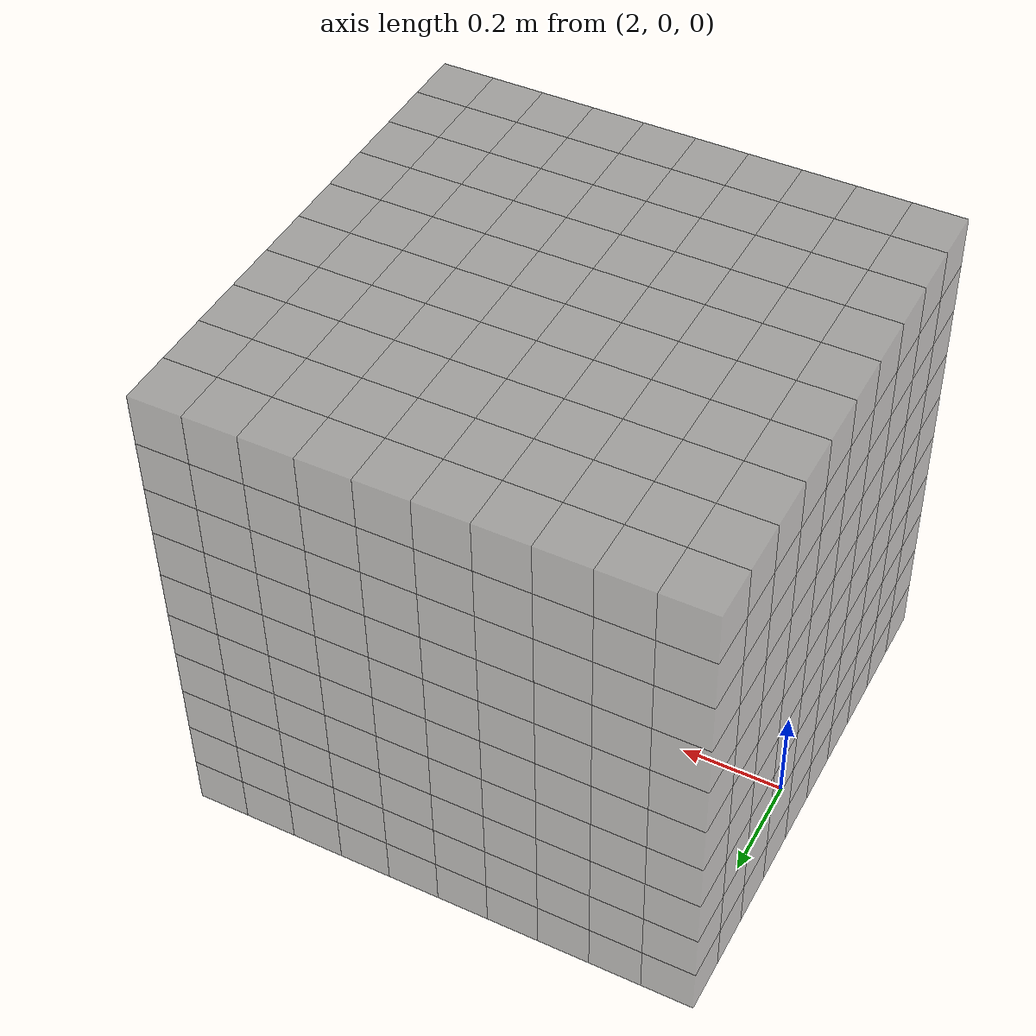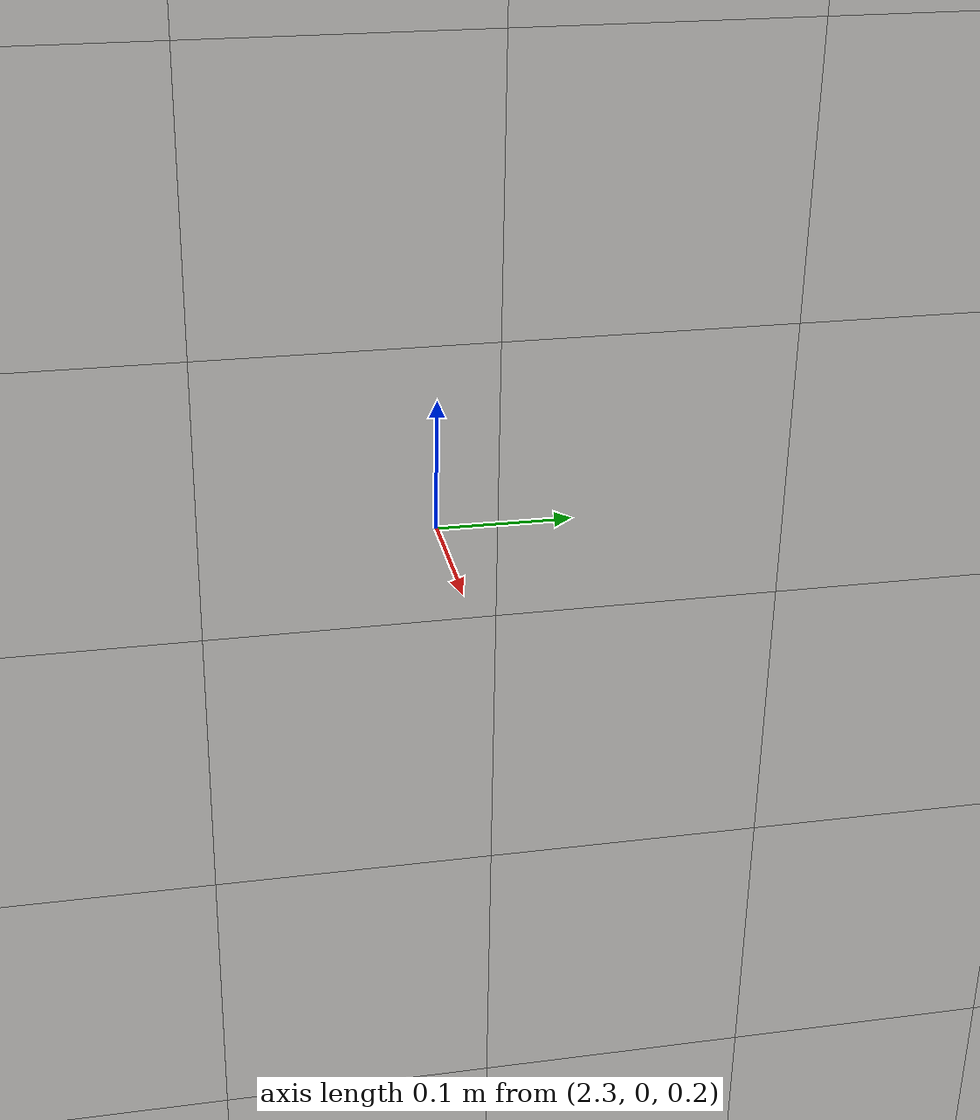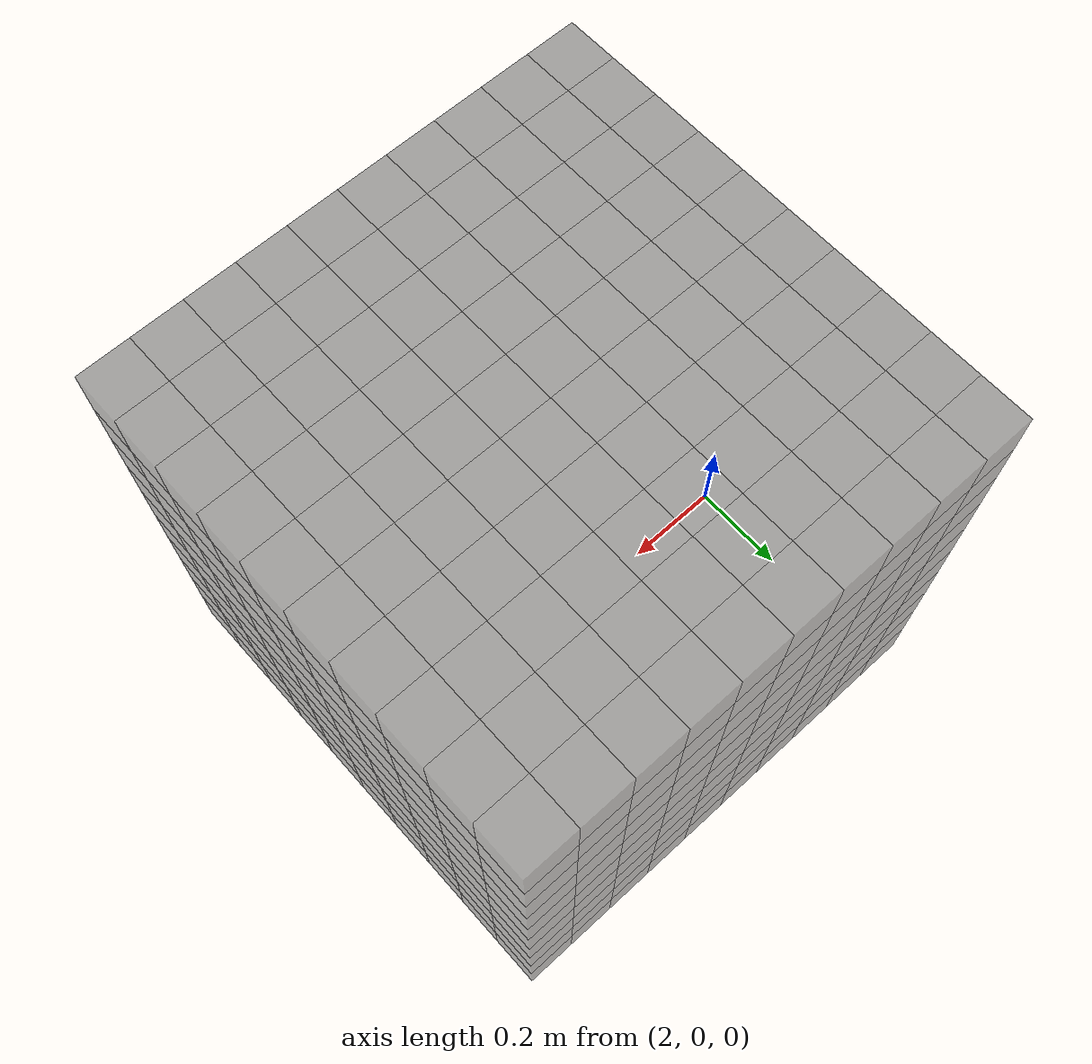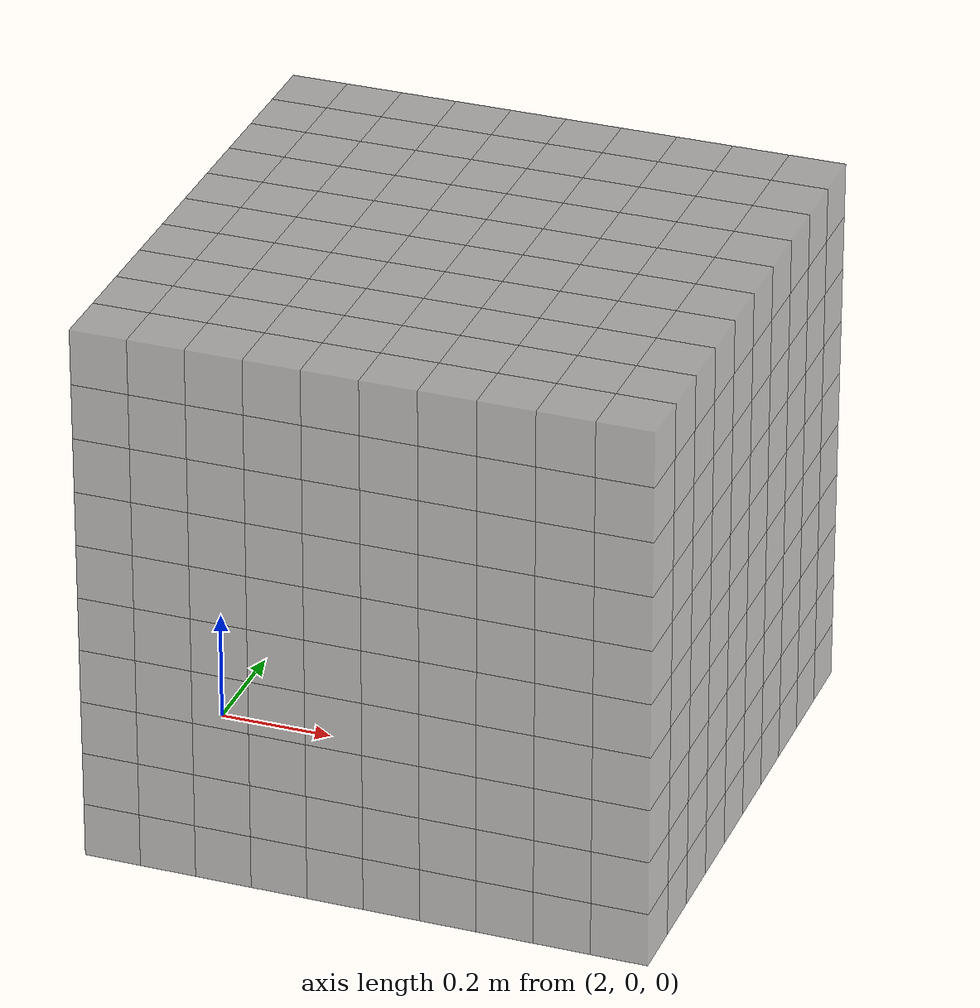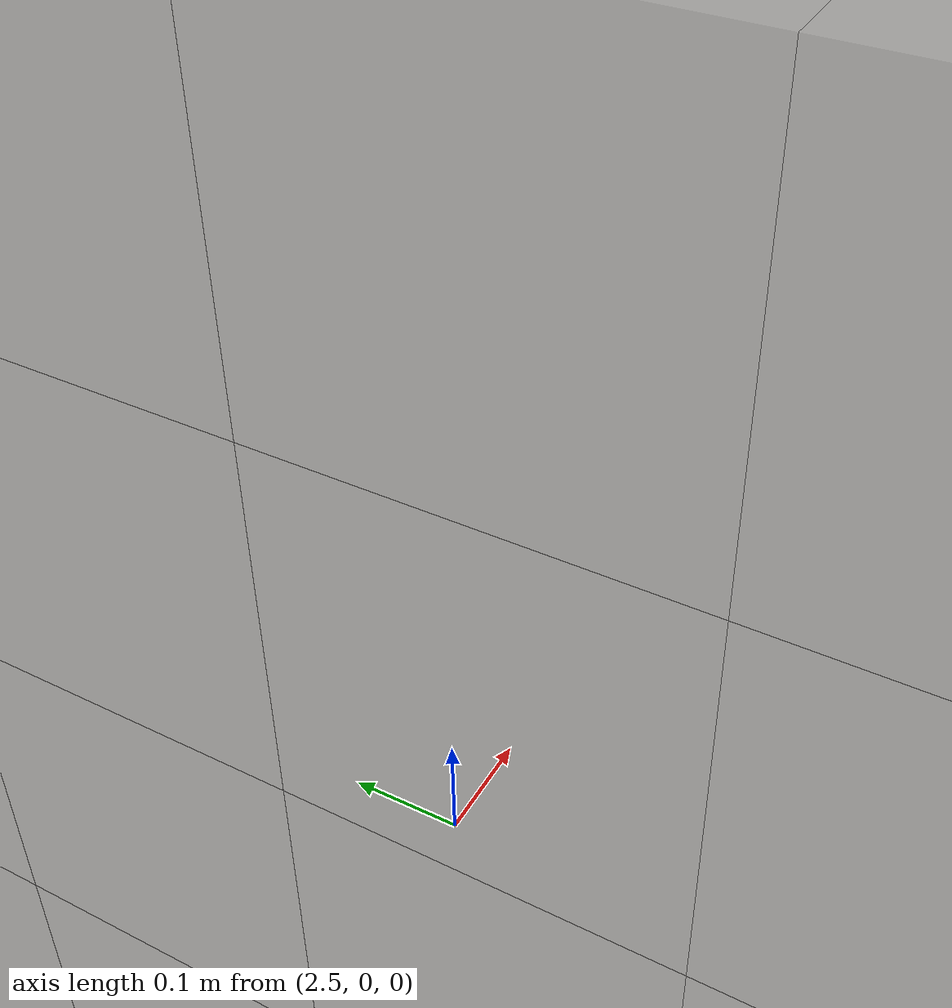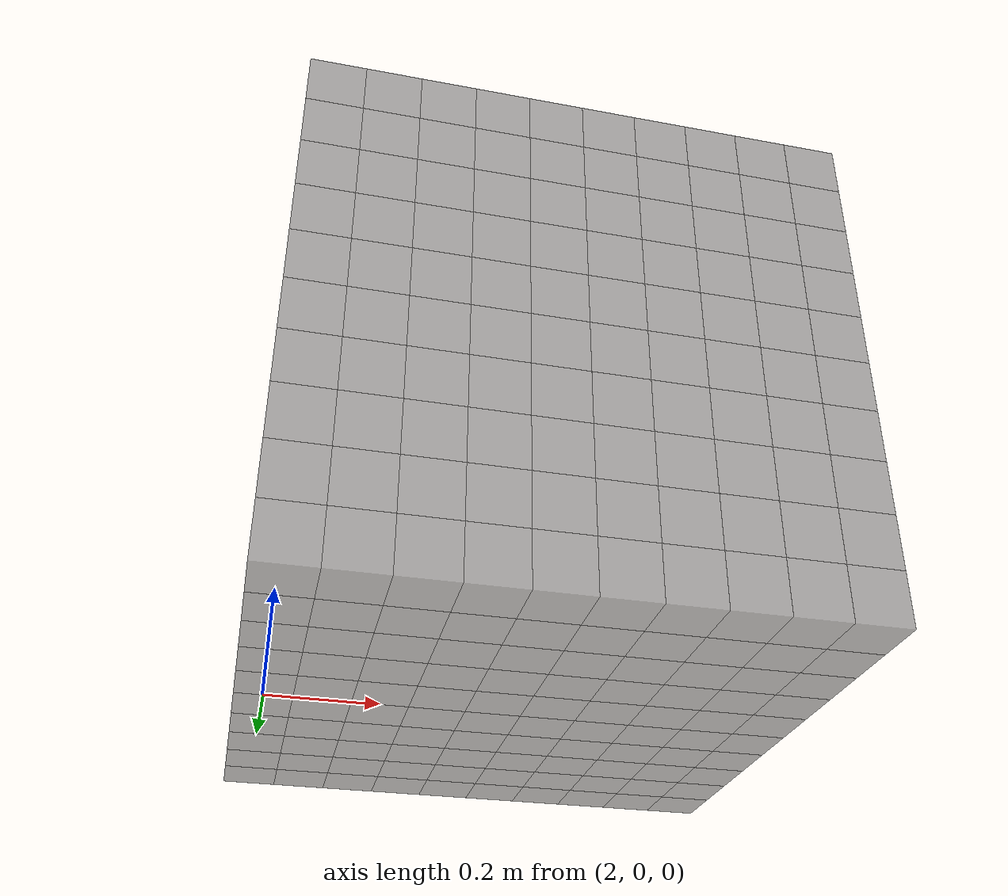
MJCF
<mujoco model="digging_scene">
  <statistic extent="2" center="1 0 0.5"/>
  <option gravity="0 0 0"/>
  <visual>
    <headlight diffuse="0.6 0.6 0.6" ambient="0.3 0.3 0.3" specular="0 0 0"/>
  </visual>
  <worldbody>
    <body name="voxel_0_0_0" pos="2.000 -0.450 0.050">
      <geom type="box" size="0.05 0.05 0.05" rgba="0.3 0.3 0.3 0.5"/>
    </body>
    <body name="voxel_0_0_1" pos="2.000 -0.350 0.050">
      <geom type="box" size="0.05 0.05 0.05" rgba="0.3 0.3 0.3 0.5"/>
    </body>
    <body name="voxel_0_0_2" pos="2.000 -0.250 0.050">
      <geom type="box" size="0.05 0.05 0.05" rgba="0.3 0.3 0.3 0.5"/>
    </body>
    <body name="voxel_0_0_3" pos="2.000 -0.150 0.050">
      <geom type="box" size="0.05 0.05 0.05" rgba="0.3 0.3 0.3 0.5"/>
    </body>
    <body name="voxel_0_0_4" pos="2.000 -0.050 0.050">
      <geom type="box" size="0.05 0.05 0.05" rgba="0.3 0.3 0.3 0.5"/>
    </body>
    <body name="voxel_0_0_5" pos="2.000 0.050 0.050">
      <geom type="box" size="0.05 0.05 0.05" rgba="0.3 0.3 0.3 0.5"/>
    </body>
    <body name="voxel_0_0_6" pos="2.000 0.150 0.050">
      <geom type="box" size="0.05 0.05 0.05" rgba="0.3 0.3 0.3 0.5"/>
    </body>
    <body name="voxel_0_0_7" pos="2.000 0.250 0.050">
      <geom type="box" size="0.05 0.05 0.05" rgba="0.3 0.3 0.3 0.5"/>
    </body>
    <body name="voxel_0_0_8" pos="2.000 0.350 0.050">
      <geom type="box" size="0.05 0.05 0.05" rgba="0.3 0.3 0.3 0.5"/>
    </body>
    <body name="voxel_0_0_9" pos="2.000 0.450 0.050">
      <geom type="box" size="0.05 0.05 0.05" rgba="0.3 0.3 0.3 0.5"/>
    </body>
    <body name="voxel_0_1_0" pos="2.000 -0.450 0.150">
      <geom type="box" size="0.05 0.05 0.05" rgba="0.3 0.3 0.3 0.5"/>
    </body>
    <body name="voxel_0_1_1" pos="2.000 -0.350 0.150">
      <geom type="box" size="0.05 0.05 0.05" rgba="0.3 0.3 0.3 0.5"/>
    </body>
    <body name="voxel_0_1_2" pos="2.000 -0.250 0.150">
      <geom type="box" size="0.05 0.05 0.05" rgba="0.3 0.3 0.3 0.5"/>
    </body>
    <body name="voxel_0_1_3" pos="2.000 -0.150 0.150">
      <geom type="box" size="0.05 0.05 0.05" rgba="0.3 0.3 0.3 0.5"/>
    </body>
    <body name="voxel_0_1_4" pos="2.000 -0.050 0.150">
      <geom type="box" size="0.05 0.05 0.05" rgba="0.3 0.3 0.3 0.5"/>
    </body>
    <body name="voxel_0_1_5" pos="2.000 0.050 0.150">
      <geom type="box" size="0.05 0.05 0.05" rgba="0.3 0.3 0.3 0.5"/>
    </body>
    <body name="voxel_0_1_6" pos="2.000 0.150 0.150">
      <geom type="box" size="0.05 0.05 0.05" rgba="0.3 0.3 0.3 0.5"/>
    </body>
    <body name="voxel_0_1_7" pos="2.000 0.250 0.150">
      <geom type="box" size="0.05 0.05 0.05" rgba="0.3 0.3 0.3 0.5"/>
    </body>
    <body name="voxel_0_1_8" pos="2.000 0.350 0.150">
      <geom type="box" size="0.05 0.05 0.05" rgba="0.3 0.3 0.3 0.5"/>
    </body>
    <body name="voxel_0_1_9" pos="2.000 0.450 0.150">
      <geom type="box" size="0.05 0.05 0.05" rgba="0.3 0.3 0.3 0.5"/>
    </body>
    <body name="voxel_0_2_0" pos="2.000 -0.450 0.250">
      <geom type="box" size="0.05 0.05 0.05" rgba="0.3 0.3 0.3 0.5"/>
    </body>
    <body name="voxel_0_2_1" pos="2.000 -0.350 0.250">
      <geom type="box" size="0.05 0.05 0.05" rgba="0.3 0.3 0.3 0.5"/>
    </body>
    <body name="voxel_0_2_2" pos="2.000 -0.250 0.250">
      <geom type="box" size="0.05 0.05 0.05" rgba="0.3 0.3 0.3 0.5"/>
    </body>
    <body name="voxel_0_2_3" pos="2.000 -0.150 0.250">
      <geom type="box" size="0.05 0.05 0.05" rgba="0.3 0.3 0.3 0.5"/>
    </body>
    <body name="voxel_0_2_4" pos="2.000 -0.050 0.250">
      <geom type="box" size="0.05 0.05 0.05" rgba="0.3 0.3 0.3 0.5"/>
    </body>
    <body name="voxel_0_2_5" pos="2.000 0.050 0.250">
      <geom type="box" size="0.05 0.05 0.05" rgba="0.3 0.3 0.3 0.5"/>
    </body>
    <body name="voxel_0_2_6" pos="2.000 0.150 0.250">
      <geom type="box" size="0.05 0.05 0.05" rgba="0.3 0.3 0.3 0.5"/>
    </body>
    <body name="voxel_0_2_7" pos="2.000 0.250 0.250">
      <geom type="box" size="0.05 0.05 0.05" rgba="0.3 0.3 0.3 0.5"/>
    </body>
    <body name="voxel_0_2_8" pos="2.000 0.350 0.250">
      <geom type="box" size="0.05 0.05 0.05" rgba="0.3 0.3 0.3 0.5"/>
    </body>
    <body name="voxel_0_2_9" pos="2.000 0.450 0.250">
      <geom type="box" size="0.05 0.05 0.05" rgba="0.3 0.3 0.3 0.5"/>
    </body>
    <body name="voxel_0_3_0" pos="2.000 -0.450 0.350">
      <geom type="box" size="0.05 0.05 0.05" rgba="0.3 0.3 0.3 0.5"/>
    </body>
    <body name="voxel_0_3_1" pos="2.000 -0.350 0.350">
      <geom type="box" size="0.05 0.05 0.05" rgba="0.3 0.3 0.3 0.5"/>
    </body>
    <body name="voxel_0_3_2" pos="2.000 -0.250 0.350">
      <geom type="box" size="0.05 0.05 0.05" rgba="0.3 0.3 0.3 0.5"/>
    </body>
    <body name="voxel_0_3_3" pos="2.000 -0.150 0.350">
      <geom type="box" size="0.05 0.05 0.05" rgba="0.3 0.3 0.3 0.5"/>
    </body>
    <body name="voxel_0_3_4" pos="2.000 -0.050 0.350">
      <geom type="box" size="0.05 0.05 0.05" rgba="0.3 0.3 0.3 0.5"/>
    </body>
    <body name="voxel_0_3_5" pos="2.000 0.050 0.350">
      <geom type="box" size="0.05 0.05 0.05" rgba="0.3 0.3 0.3 0.5"/>
    </body>
    <body name="voxel_0_3_6" pos="2.000 0.150 0.350">
      <geom type="box" size="0.05 0.05 0.05" rgba="0.3 0.3 0.3 0.5"/>
    </body>
    <body name="voxel_0_3_7" pos="2.000 0.250 0.350">
      <geom type="box" size="0.05 0.05 0.05" rgba="0.3 0.3 0.3 0.5"/>
    </body>
    <body name="voxel_0_3_8" pos="2.000 0.350 0.350">
      <geom type="box" size="0.05 0.05 0.05" rgba="0.3 0.3 0.3 0.5"/>
    </body>
    <body name="voxel_0_3_9" pos="2.000 0.450 0.350">
      <geom type="box" size="0.05 0.05 0.05" rgba="0.3 0.3 0.3 0.5"/>
    </body>
    <body name="voxel_0_4_0" pos="2.000 -0.450 0.450">
      <geom type="box" size="0.05 0.05 0.05" rgba="0.3 0.3 0.3 0.5"/>
    </body>
    <body name="voxel_0_4_1" pos="2.000 -0.350 0.450">
      <geom type="box" size="0.05 0.05 0.05" rgba="0.3 0.3 0.3 0.5"/>
    </body>
    <body name="voxel_0_4_2" pos="2.000 -0.250 0.450">
      <geom type="box" size="0.05 0.05 0.05" rgba="0.3 0.3 0.3 0.5"/>
    </body>
    <body name="voxel_0_4_3" pos="2.000 -0.150 0.450">
      <geom type="box" size="0.05 0.05 0.05" rgba="0.3 0.3 0.3 0.5"/>
    </body>
    <body name="voxel_0_4_4" pos="2.000 -0.050 0.450">
      <geom type="box" size="0.05 0.05 0.05" rgba="0.3 0.3 0.3 0.5"/>
    </body>
    <body name="voxel_0_4_5" pos="2.000 0.050 0.450">
      <geom type="box" size="0.05 0.05 0.05" rgba="0.3 0.3 0.3 0.5"/>
    </body>
    <body name="voxel_0_4_6" pos="2.000 0.150 0.450">
      <geom type="box" size="0.05 0.05 0.05" rgba="0.3 0.3 0.3 0.5"/>
    </body>
    <body name="voxel_0_4_7" pos="2.000 0.250 0.450">
      <geom type="box" size="0.05 0.05 0.05" rgba="0.3 0.3 0.3 0.5"/>
    </body>
    <body name="voxel_0_4_8" pos="2.000 0.350 0.450">
      <geom type="box" size="0.05 0.05 0.05" rgba="0.3 0.3 0.3 0.5"/>
    </body>
    <body name="voxel_0_4_9" pos="2.000 0.450 0.450">
      <geom type="box" size="0.05 0.05 0.05" rgba="0.3 0.3 0.3 0.5"/>
    </body>
    <body name="voxel_0_5_0" pos="2.000 -0.450 0.550">
      <geom type="box" size="0.05 0.05 0.05" rgba="0.3 0.3 0.3 0.5"/>
    </body>
    <body name="voxel_0_5_1" pos="2.000 -0.350 0.550">
      <geom type="box" size="0.05 0.05 0.05" rgba="0.3 0.3 0.3 0.5"/>
    </body>
    <body name="voxel_0_5_2" pos="2.000 -0.250 0.550">
      <geom type="box" size="0.05 0.05 0.05" rgba="0.3 0.3 0.3 0.5"/>
    </body>
    <body name="voxel_0_5_3" pos="2.000 -0.150 0.550">
      <geom type="box" size="0.05 0.05 0.05" rgba="0.3 0.3 0.3 0.5"/>
    </body>
    <body name="voxel_0_5_4" pos="2.000 -0.050 0.550">
      <geom type="box" size="0.05 0.05 0.05" rgba="0.3 0.3 0.3 0.5"/>
    </body>
    <body name="voxel_0_5_5" pos="2.000 0.050 0.550">
      <geom type="box" size="0.05 0.05 0.05" rgba="0.3 0.3 0.3 0.5"/>
    </body>
    <body name="voxel_0_5_6" pos="2.000 0.150 0.550">
      <geom type="box" size="0.05 0.05 0.05" rgba="0.3 0.3 0.3 0.5"/>
    </body>
    <body name="voxel_0_5_7" pos="2.000 0.250 0.550">
      <geom type="box" size="0.05 0.05 0.05" rgba="0.3 0.3 0.3 0.5"/>
    </body>
    <body name="voxel_0_5_8" pos="2.000 0.350 0.550">
      <geom type="box" size="0.05 0.05 0.05" rgba="0.3 0.3 0.3 0.5"/>
    </body>
    <body name="voxel_0_5_9" pos="2.000 0.450 0.550">
      <geom type="box" size="0.05 0.05 0.05" rgba="0.3 0.3 0.3 0.5"/>
    </body>
    <body name="voxel_0_6_0" pos="2.000 -0.450 0.650">
      <geom type="box" size="0.05 0.05 0.05" rgba="0.3 0.3 0.3 0.5"/>
    </body>
    <body name="voxel_0_6_1" pos="2.000 -0.350 0.650">
      <geom type="box" size="0.05 0.05 0.05" rgba="0.3 0.3 0.3 0.5"/>
    </body>
    <body name="voxel_0_6_2" pos="2.000 -0.250 0.650">
      <geom type="box" size="0.05 0.05 0.05" rgba="0.3 0.3 0.3 0.5"/>
    </body>
    <body name="voxel_0_6_3" pos="2.000 -0.150 0.650">
      <geom type="box" size="0.05 0.05 0.05" rgba="0.3 0.3 0.3 0.5"/>
    </body>
    <body name="voxel_0_6_4" pos="2.000 -0.050 0.650">
      <geom type="box" size="0.05 0.05 0.05" rgba="0.3 0.3 0.3 0.5"/>
    </body>
    <body name="voxel_0_6_5" pos="2.000 0.050 0.650">
      <geom type="box" size="0.05 0.05 0.05" rgba="0.3 0.3 0.3 0.5"/>
    </body>
    <body name="voxel_0_6_6" pos="2.000 0.150 0.650">
      <geom type="box" size="0.05 0.05 0.05" rgba="0.3 0.3 0.3 0.5"/>
    </body>
    <body name="voxel_0_6_7" pos="2.000 0.250 0.650">
      <geom type="box" size="0.05 0.05 0.05" rgba="0.3 0.3 0.3 0.5"/>
    </body>
    <body name="voxel_0_6_8" pos="2.000 0.350 0.650">
      <geom type="box" size="0.05 0.05 0.05" rgba="0.3 0.3 0.3 0.5"/>
    </body>
    <body name="voxel_0_6_9" pos="2.000 0.450 0.650">
      <geom type="box" size="0.05 0.05 0.05" rgba="0.3 0.3 0.3 0.5"/>
    </body>
    <body name="voxel_0_7_0" pos="2.000 -0.450 0.750">
      <geom type="box" size="0.05 0.05 0.05" rgba="0.3 0.3 0.3 0.5"/>
    </body>
    <body name="voxel_0_7_1" pos="2.000 -0.350 0.750">
      <geom type="box" size="0.05 0.05 0.05" rgba="0.3 0.3 0.3 0.5"/>
    </body>
    <body name="voxel_0_7_2" pos="2.000 -0.250 0.750">
      <geom type="box" size="0.05 0.05 0.05" rgba="0.3 0.3 0.3 0.5"/>
    </body>
    <body name="voxel_0_7_3" pos="2.000 -0.150 0.750">
      <geom type="box" size="0.05 0.05 0.05" rgba="0.3 0.3 0.3 0.5"/>
    </body>
    <body name="voxel_0_7_4" pos="2.000 -0.050 0.750">
      <geom type="box" size="0.05 0.05 0.05" rgba="0.3 0.3 0.3 0.5"/>
    </body>
    <body name="voxel_0_7_5" pos="2.000 0.050 0.750">
      <geom type="box" size="0.05 0.05 0.05" rgba="0.3 0.3 0.3 0.5"/>
    </body>
    <body name="voxel_0_7_6" pos="2.000 0.150 0.750">
      <geom type="box" size="0.05 0.05 0.05" rgba="0.3 0.3 0.3 0.5"/>
    </body>
    <body name="voxel_0_7_7" pos="2.000 0.250 0.750">
      <geom type="box" size="0.05 0.05 0.05" rgba="0.3 0.3 0.3 0.5"/>
    </body>
    <body name="voxel_0_7_8" pos="2.000 0.350 0.750">
      <geom type="box" size="0.05 0.05 0.05" rgba="0.3 0.3 0.3 0.5"/>
    </body>
    <body name="voxel_0_7_9" pos="2.000 0.450 0.750">
      <geom type="box" size="0.05 0.05 0.05" rgba="0.3 0.3 0.3 0.5"/>
    </body>
    <body name="voxel_0_8_0" pos="2.000 -0.450 0.850">
      <geom type="box" size="0.05 0.05 0.05" rgba="0.3 0.3 0.3 0.5"/>
    </body>
    <body name="voxel_0_8_1" pos="2.000 -0.350 0.850">
      <geom type="box" size="0.05 0.05 0.05" rgba="0.3 0.3 0.3 0.5"/>
    </body>
    <body name="voxel_0_8_2" pos="2.000 -0.250 0.850">
      <geom type="box" size="0.05 0.05 0.05" rgba="0.3 0.3 0.3 0.5"/>
    </body>
    <body name="voxel_0_8_3" pos="2.000 -0.150 0.850">
      <geom type="box" size="0.05 0.05 0.05" rgba="0.3 0.3 0.3 0.5"/>
    </body>
    <body name="voxel_0_8_4" pos="2.000 -0.050 0.850">
      <geom type="box" size="0.05 0.05 0.05" rgba="0.3 0.3 0.3 0.5"/>
    </body>
    <body name="voxel_0_8_5" pos="2.000 0.050 0.850">
      <geom type="box" size="0.05 0.05 0.05" rgba="0.3 0.3 0.3 0.5"/>
    </body>
    <body name="voxel_0_8_6" pos="2.000 0.150 0.850">
      <geom type="box" size="0.05 0.05 0.05" rgba="0.3 0.3 0.3 0.5"/>
    </body>
    <body name="voxel_0_8_7" pos="2.000 0.250 0.850">
      <geom type="box" size="0.05 0.05 0.05" rgba="0.3 0.3 0.3 0.5"/>
    </body>
    <body name="voxel_0_8_8" pos="2.000 0.350 0.850">
      <geom type="box" size="0.05 0.05 0.05" rgba="0.3 0.3 0.3 0.5"/>
    </body>
    <body name="voxel_0_8_9" pos="2.000 0.450 0.850">
      <geom type="box" size="0.05 0.05 0.05" rgba="0.3 0.3 0.3 0.5"/>
    </body>
    <body name="voxel_0_9_0" pos="2.000 -0.450 0.950">
      <geom type="box" size="0.05 0.05 0.05" rgba="0.3 0.3 0.3 0.5"/>
    </body>
    <body name="voxel_0_9_1" pos="2.000 -0.350 0.950">
      <geom type="box" size="0.05 0.05 0.05" rgba="0.3 0.3 0.3 0.5"/>
    </body>
    <body name="voxel_0_9_2" pos="2.000 -0.250 0.950">
      <geom type="box" size="0.05 0.05 0.05" rgba="0.3 0.3 0.3 0.5"/>
    </body>
    <body name="voxel_0_9_3" pos="2.000 -0.150 0.950">
      <geom type="box" size="0.05 0.05 0.05" rgba="0.3 0.3 0.3 0.5"/>
    </body>
    <body name="voxel_0_9_4" pos="2.000 -0.050 0.950">
      <geom type="box" size="0.05 0.05 0.05" rgba="0.3 0.3 0.3 0.5"/>
    </body>
    <body name="voxel_0_9_5" pos="2.000 0.050 0.950">
      <geom type="box" size="0.05 0.05 0.05" rgba="0.3 0.3 0.3 0.5"/>
    </body>
    <body name="voxel_0_9_6" pos="2.000 0.150 0.950">
      <geom type="box" size="0.05 0.05 0.05" rgba="0.3 0.3 0.3 0.5"/>
    </body>
    <body name="voxel_0_9_7" pos="2.000 0.250 0.950">
      <geom type="box" size="0.05 0.05 0.05" rgba="0.3 0.3 0.3 0.5"/>
    </body>
    <body name="voxel_0_9_8" pos="2.000 0.350 0.950">
      <geom type="box" size="0.05 0.05 0.05" rgba="0.3 0.3 0.3 0.5"/>
    </body>
    <body name="voxel_0_9_9" pos="2.000 0.450 0.950">
      <geom type="box" size="0.05 0.05 0.05" rgba="0.3 0.3 0.3 0.5"/>
    </body>
    <body name="voxel_1_0_0" pos="2.100 -0.450 0.050">
      <geom type="box" size="0.05 0.05 0.05" rgba="0.3 0.3 0.3 0.5"/>
    </body>
    <body name="voxel_1_0_1" pos="2.100 -0.350 0.050">
      <geom type="box" size="0.05 0.05 0.05" rgba="0.3 0.3 0.3 0.5"/>
    </body>
    <body name="voxel_1_0_2" pos="2.100 -0.250 0.050">
      <geom type="box" size="0.05 0.05 0.05" rgba="0.3 0.3 0.3 0.5"/>
    </body>
    <body name="voxel_1_0_3" pos="2.100 -0.150 0.050">
      <geom type="box" size="0.05 0.05 0.05" rgba="0.3 0.3 0.3 0.5"/>
    </body>
    <body name="voxel_1_0_4" pos="2.100 -0.050 0.050">
      <geom type="box" size="0.05 0.05 0.05" rgba="0.3 0.3 0.3 0.5"/>
    </body>
    <body name="voxel_1_0_5" pos="2.100 0.050 0.050">
      <geom type="box" size="0.05 0.05 0.05" rgba="0.3 0.3 0.3 0.5"/>
    </body>
    <body name="voxel_1_0_6" pos="2.100 0.150 0.050">
      <geom type="box" size="0.05 0.05 0.05" rgba="0.3 0.3 0.3 0.5"/>
    </body>
    <body name="voxel_1_0_7" pos="2.100 0.250 0.050">
      <geom type="box" size="0.05 0.05 0.05" rgba="0.3 0.3 0.3 0.5"/>
    </body>
    <body name="voxel_1_0_8" pos="2.100 0.350 0.050">
      <geom type="box" size="0.05 0.05 0.05" rgba="0.3 0.3 0.3 0.5"/>
    </body>
    <body name="voxel_1_0_9" pos="2.100 0.450 0.050">
      <geom type="box" size="0.05 0.05 0.05" rgba="0.3 0.3 0.3 0.5"/>
    </body>
    <body name="voxel_1_1_0" pos="2.100 -0.450 0.150">
      <geom type="box" size="0.05 0.05 0.05" rgba="0.3 0.3 0.3 0.5"/>
    </body>
    <body name="voxel_1_1_1" pos="2.100 -0.350 0.150">
      <geom type="box" size="0.05 0.05 0.05" rgba="0.3 0.3 0.3 0.5"/>
    </body>
    <body name="voxel_1_1_2" pos="2.100 -0.250 0.150">
      <geom type="box" size="0.05 0.05 0.05" rgba="0.3 0.3 0.3 0.5"/>
    </body>
    <body name="voxel_1_1_3" pos="2.100 -0.150 0.150">
      <geom type="box" size="0.05 0.05 0.05" rgba="0.3 0.3 0.3 0.5"/>
    </body>
    <body name="voxel_1_1_4" pos="2.100 -0.050 0.150">
      <geom type="box" size="0.05 0.05 0.05" rgba="0.3 0.3 0.3 0.5"/>
    </body>
    <body name="voxel_1_1_5" pos="2.100 0.050 0.150">
      <geom type="box" size="0.05 0.05 0.05" rgba="0.3 0.3 0.3 0.5"/>
    </body>
    <body name="voxel_1_1_6" pos="2.100 0.150 0.150">
      <geom type="box" size="0.05 0.05 0.05" rgba="0.3 0.3 0.3 0.5"/>
    </body>
    <body name="voxel_1_1_7" pos="2.100 0.250 0.150">
      <geom type="box" size="0.05 0.05 0.05" rgba="0.3 0.3 0.3 0.5"/>
    </body>
    <body name="voxel_1_1_8" pos="2.100 0.350 0.150">
      <geom type="box" size="0.05 0.05 0.05" rgba="0.3 0.3 0.3 0.5"/>
    </body>
    <body name="voxel_1_1_9" pos="2.100 0.450 0.150">
      <geom type="box" size="0.05 0.05 0.05" rgba="0.3 0.3 0.3 0.5"/>
    </body>
    <body name="voxel_1_2_0" pos="2.100 -0.450 0.250">
      <geom type="box" size="0.05 0.05 0.05" rgba="0.3 0.3 0.3 0.5"/>
    </body>
    <body name="voxel_1_2_1" pos="2.100 -0.350 0.250">
      <geom type="box" size="0.05 0.05 0.05" rgba="0.3 0.3 0.3 0.5"/>
    </body>
    <body name="voxel_1_2_2" pos="2.100 -0.250 0.250">
      <geom type="box" size="0.05 0.05 0.05" rgba="0.3 0.3 0.3 0.5"/>
    </body>
    <body name="voxel_1_2_3" pos="2.100 -0.150 0.250">
      <geom type="box" size="0.05 0.05 0.05" rgba="0.3 0.3 0.3 0.5"/>
    </body>
    <body name="voxel_1_2_4" pos="2.100 -0.050 0.250">
      <geom type="box" size="0.05 0.05 0.05" rgba="0.3 0.3 0.3 0.5"/>
    </body>
    <body name="voxel_1_2_5" pos="2.100 0.050 0.250">
      <geom type="box" size="0.05 0.05 0.05" rgba="0.3 0.3 0.3 0.5"/>
    </body>
    <body name="voxel_1_2_6" pos="2.100 0.150 0.250">
      <geom type="box" size="0.05 0.05 0.05" rgba="0.3 0.3 0.3 0.5"/>
    </body>
    <body name="voxel_1_2_7" pos="2.100 0.250 0.250">
      <geom type="box" size="0.05 0.05 0.05" rgba="0.3 0.3 0.3 0.5"/>
    </body>
    <body name="voxel_1_2_8" pos="2.100 0.350 0.250">
      <geom type="box" size="0.05 0.05 0.05" rgba="0.3 0.3 0.3 0.5"/>
    </body>
    <body name="voxel_1_2_9" pos="2.100 0.450 0.250">
      <geom type="box" size="0.05 0.05 0.05" rgba="0.3 0.3 0.3 0.5"/>
    </body>
    <body name="voxel_1_3_0" pos="2.100 -0.450 0.350">
      <geom type="box" size="0.05 0.05 0.05" rgba="0.3 0.3 0.3 0.5"/>
    </body>
    <body name="voxel_1_3_1" pos="2.100 -0.350 0.350">
      <geom type="box" size="0.05 0.05 0.05" rgba="0.3 0.3 0.3 0.5"/>
    </body>
    <body name="voxel_1_3_2" pos="2.100 -0.250 0.350">
      <geom type="box" size="0.05 0.05 0.05" rgba="0.3 0.3 0.3 0.5"/>
    </body>
    <body name="voxel_1_3_3" pos="2.100 -0.150 0.350">
      <geom type="box" size="0.05 0.05 0.05" rgba="0.3 0.3 0.3 0.5"/>
    </body>
    <body name="voxel_1_3_4" pos="2.100 -0.050 0.350">
      <geom type="box" size="0.05 0.05 0.05" rgba="0.3 0.3 0.3 0.5"/>
    </body>
    <body name="voxel_1_3_5" pos="2.100 0.050 0.350">
      <geom type="box" size="0.05 0.05 0.05" rgba="0.3 0.3 0.3 0.5"/>
    </body>
    <body name="voxel_1_3_6" pos="2.100 0.150 0.350">
      <geom type="box" size="0.05 0.05 0.05" rgba="0.3 0.3 0.3 0.5"/>
    </body>
    <body name="voxel_1_3_7" pos="2.100 0.250 0.350">
      <geom type="box" size="0.05 0.05 0.05" rgba="0.3 0.3 0.3 0.5"/>
    </body>
    <body name="voxel_1_3_8" pos="2.100 0.350 0.350">
      <geom type="box" size="0.05 0.05 0.05" rgba="0.3 0.3 0.3 0.5"/>
    </body>
    <body name="voxel_1_3_9" pos="2.100 0.450 0.350">
      <geom type="box" size="0.05 0.05 0.05" rgba="0.3 0.3 0.3 0.5"/>
    </body>
    <body name="voxel_1_4_0" pos="2.100 -0.450 0.450">
      <geom type="box" size="0.05 0.05 0.05" rgba="0.3 0.3 0.3 0.5"/>
    </body>
    <body name="voxel_1_4_1" pos="2.100 -0.350 0.450">
      <geom type="box" size="0.05 0.05 0.05" rgba="0.3 0.3 0.3 0.5"/>
    </body>
    <body name="voxel_1_4_2" pos="2.100 -0.250 0.450">
      <geom type="box" size="0.05 0.05 0.05" rgba="0.3 0.3 0.3 0.5"/>
    </body>
    <body name="voxel_1_4_3" pos="2.100 -0.150 0.450">
      <geom type="box" size="0.05 0.05 0.05" rgba="0.3 0.3 0.3 0.5"/>
    </body>
    <body name="voxel_1_4_4" pos="2.100 -0.050 0.450">
      <geom type="box" size="0.05 0.05 0.05" rgba="0.3 0.3 0.3 0.5"/>
    </body>
    <body name="voxel_1_4_5" pos="2.100 0.050 0.450">
      <geom type="box" size="0.05 0.05 0.05" rgba="0.3 0.3 0.3 0.5"/>
    </body>
    <body name="voxel_1_4_6" pos="2.100 0.150 0.450">
      <geom type="box" size="0.05 0.05 0.05" rgba="0.3 0.3 0.3 0.5"/>
    </body>
    <body name="voxel_1_4_7" pos="2.100 0.250 0.450">
      <geom type="box" size="0.05 0.05 0.05" rgba="0.3 0.3 0.3 0.5"/>
    </body>
    <body name="voxel_1_4_8" pos="2.100 0.350 0.450">
      <geom type="box" size="0.05 0.05 0.05" rgba="0.3 0.3 0.3 0.5"/>
    </body>
    <body name="voxel_1_4_9" pos="2.100 0.450 0.450">
      <geom type="box" size="0.05 0.05 0.05" rgba="0.3 0.3 0.3 0.5"/>
    </body>
    <body name="voxel_1_5_0" pos="2.100 -0.450 0.550">
      <geom type="box" size="0.05 0.05 0.05" rgba="0.3 0.3 0.3 0.5"/>
    </body>
    <body name="voxel_1_5_1" pos="2.100 -0.350 0.550">
      <geom type="box" size="0.05 0.05 0.05" rgba="0.3 0.3 0.3 0.5"/>
    </body>
    <body name="voxel_1_5_2" pos="2.100 -0.250 0.550">
      <geom type="box" size="0.05 0.05 0.05" rgba="0.3 0.3 0.3 0.5"/>
    </body>
    <body name="voxel_1_5_3" pos="2.100 -0.150 0.550">
      <geom type="box" size="0.05 0.05 0.05" rgba="0.3 0.3 0.3 0.5"/>
    </body>
    <body name="voxel_1_5_4" pos="2.100 -0.050 0.550">
      <geom type="box" size="0.05 0.05 0.05" rgba="0.3 0.3 0.3 0.5"/>
    </body>
    <body name="voxel_1_5_5" pos="2.100 0.050 0.550">
      <geom type="box" size="0.05 0.05 0.05" rgba="0.3 0.3 0.3 0.5"/>
    </body>
    <body name="voxel_1_5_6" pos="2.100 0.150 0.550">
      <geom type="box" size="0.05 0.05 0.05" rgba="0.3 0.3 0.3 0.5"/>
    </body>
    <body name="voxel_1_5_7" pos="2.100 0.250 0.550">
      <geom type="box" size="0.05 0.05 0.05" rgba="0.3 0.3 0.3 0.5"/>
    </body>
    <body name="voxel_1_5_8" pos="2.100 0.350 0.550">
      <geom type="box" size="0.05 0.05 0.05" rgba="0.3 0.3 0.3 0.5"/>
    </body>
    <body name="voxel_1_5_9" pos="2.100 0.450 0.550">
      <geom type="box" size="0.05 0.05 0.05" rgba="0.3 0.3 0.3 0.5"/>
    </body>
    <body name="voxel_1_6_0" pos="2.100 -0.450 0.650">
      <geom type="box" size="0.05 0.05 0.05" rgba="0.3 0.3 0.3 0.5"/>
    </body>
    <body name="voxel_1_6_1" pos="2.100 -0.350 0.650">
      <geom type="box" size="0.05 0.05 0.05" rgba="0.3 0.3 0.3 0.5"/>
    </body>
    <body name="voxel_1_6_2" pos="2.100 -0.250 0.650">
      <geom type="box" size="0.05 0.05 0.05" rgba="0.3 0.3 0.3 0.5"/>
    </body>
    <body name="voxel_1_6_3" pos="2.100 -0.150 0.650">
      <geom type="box" size="0.05 0.05 0.05" rgba="0.3 0.3 0.3 0.5"/>
    </body>
    <body name="voxel_1_6_4" pos="2.100 -0.050 0.650">
      <geom type="box" size="0.05 0.05 0.05" rgba="0.3 0.3 0.3 0.5"/>
    </body>
    <body name="voxel_1_6_5" pos="2.100 0.050 0.650">
      <geom type="box" size="0.05 0.05 0.05" rgba="0.3 0.3 0.3 0.5"/>
    </body>
    <body name="voxel_1_6_6" pos="2.100 0.150 0.650">
      <geom type="box" size="0.05 0.05 0.05" rgba="0.3 0.3 0.3 0.5"/>
    </body>
    <body name="voxel_1_6_7" pos="2.100 0.250 0.650">
      <geom type="box" size="0.05 0.05 0.05" rgba="0.3 0.3 0.3 0.5"/>
    </body>
    <body name="voxel_1_6_8" pos="2.100 0.350 0.650">
      <geom type="box" size="0.05 0.05 0.05" rgba="0.3 0.3 0.3 0.5"/>
    </body>
    <body name="voxel_1_6_9" pos="2.100 0.450 0.650">
      <geom type="box" size="0.05 0.05 0.05" rgba="0.3 0.3 0.3 0.5"/>
    </body>
    <body name="voxel_1_7_0" pos="2.100 -0.450 0.750">
      <geom type="box" size="0.05 0.05 0.05" rgba="0.3 0.3 0.3 0.5"/>
    </body>
    <body name="voxel_1_7_1" pos="2.100 -0.350 0.750">
      <geom type="box" size="0.05 0.05 0.05" rgba="0.3 0.3 0.3 0.5"/>
    </body>
    <body name="voxel_1_7_2" pos="2.100 -0.250 0.750">
      <geom type="box" size="0.05 0.05 0.05" rgba="0.3 0.3 0.3 0.5"/>
    </body>
    <body name="voxel_1_7_3" pos="2.100 -0.150 0.750">
      <geom type="box" size="0.05 0.05 0.05" rgba="0.3 0.3 0.3 0.5"/>
    </body>
    <body name="voxel_1_7_4" pos="2.100 -0.050 0.750">
      <geom type="box" size="0.05 0.05 0.05" rgba="0.3 0.3 0.3 0.5"/>
    </body>
    <body name="voxel_1_7_5" pos="2.100 0.050 0.750">
      <geom type="box" size="0.05 0.05 0.05" rgba="0.3 0.3 0.3 0.5"/>
    </body>
    <body name="voxel_1_7_6" pos="2.100 0.150 0.750">
      <geom type="box" size="0.05 0.05 0.05" rgba="0.3 0.3 0.3 0.5"/>
    </body>
    <body name="voxel_1_7_7" pos="2.100 0.250 0.750">
      <geom type="box" size="0.05 0.05 0.05" rgba="0.3 0.3 0.3 0.5"/>
    </body>
    <body name="voxel_1_7_8" pos="2.100 0.350 0.750">
      <geom type="box" size="0.05 0.05 0.05" rgba="0.3 0.3 0.3 0.5"/>
    </body>
    <body name="voxel_1_7_9" pos="2.100 0.450 0.750">
      <geom type="box" size="0.05 0.05 0.05" rgba="0.3 0.3 0.3 0.5"/>
    </body>
    <body name="voxel_1_8_0" pos="2.100 -0.450 0.850">
      <geom type="box" size="0.05 0.05 0.05" rgba="0.3 0.3 0.3 0.5"/>
    </body>
    <body name="voxel_1_8_1" pos="2.100 -0.350 0.850">
      <geom type="box" size="0.05 0.05 0.05" rgba="0.3 0.3 0.3 0.5"/>
    </body>
    <body name="voxel_1_8_2" pos="2.100 -0.250 0.850">
      <geom type="box" size="0.05 0.05 0.05" rgba="0.3 0.3 0.3 0.5"/>
    </body>
    <body name="voxel_1_8_3" pos="2.100 -0.150 0.850">
      <geom type="box" size="0.05 0.05 0.05" rgba="0.3 0.3 0.3 0.5"/>
    </body>
    <body name="voxel_1_8_4" pos="2.100 -0.050 0.850">
      <geom type="box" size="0.05 0.05 0.05" rgba="0.3 0.3 0.3 0.5"/>
    </body>
    <body name="voxel_1_8_5" pos="2.100 0.050 0.850">
      <geom type="box" size="0.05 0.05 0.05" rgba="0.3 0.3 0.3 0.5"/>
    </body>
    <body name="voxel_1_8_6" pos="2.100 0.150 0.850">
      <geom type="box" size="0.05 0.05 0.05" rgba="0.3 0.3 0.3 0.5"/>
    </body>
    <body name="voxel_1_8_7" pos="2.100 0.250 0.850">
      <geom type="box" size="0.05 0.05 0.05" rgba="0.3 0.3 0.3 0.5"/>
    </body>
    <body name="voxel_1_8_8" pos="2.100 0.350 0.850">
      <geom type="box" size="0.05 0.05 0.05" rgba="0.3 0.3 0.3 0.5"/>
    </body>
    <body name="voxel_1_8_9" pos="2.100 0.450 0.850">
      <geom type="box" size="0.05 0.05 0.05" rgba="0.3 0.3 0.3 0.5"/>
    </body>
    <body name="voxel_1_9_0" pos="2.100 -0.450 0.950">
      <geom type="box" size="0.05 0.05 0.05" rgba="0.3 0.3 0.3 0.5"/>
    </body>
    <body name="voxel_1_9_1" pos="2.100 -0.350 0.950">
      <geom type="box" size="0.05 0.05 0.05" rgba="0.3 0.3 0.3 0.5"/>
    </body>
    <body name="voxel_1_9_2" pos="2.100 -0.250 0.950">
      <geom type="box" size="0.05 0.05 0.05" rgba="0.3 0.3 0.3 0.5"/>
    </body>
    <body name="voxel_1_9_3" pos="2.100 -0.150 0.950">
      <geom type="box" size="0.05 0.05 0.05" rgba="0.3 0.3 0.3 0.5"/>
    </body>
    <body name="voxel_1_9_4" pos="2.100 -0.050 0.950">
      <geom type="box" size="0.05 0.05 0.05" rgba="0.3 0.3 0.3 0.5"/>
    </body>
    <body name="voxel_1_9_5" pos="2.100 0.050 0.950">
      <geom type="box" size="0.05 0.05 0.05" rgba="0.3 0.3 0.3 0.5"/>
    </body>
    <body name="voxel_1_9_6" pos="2.100 0.150 0.950">
      <geom type="box" size="0.05 0.05 0.05" rgba="0.3 0.3 0.3 0.5"/>
    </body>
    <body name="voxel_1_9_7" pos="2.100 0.250 0.950">
      <geom type="box" size="0.05 0.05 0.05" rgba="0.3 0.3 0.3 0.5"/>
    </body>
    <body name="voxel_1_9_8" pos="2.100 0.350 0.950">
      <geom type="box" size="0.05 0.05 0.05" rgba="0.3 0.3 0.3 0.5"/>
    </body>
    <body name="voxel_1_9_9" pos="2.100 0.450 0.950">
      <geom type="box" size="0.05 0.05 0.05" rgba="0.3 0.3 0.3 0.5"/>
    </body>
    <body name="voxel_2_0_0" pos="2.200 -0.450 0.050">
      <geom type="box" size="0.05 0.05 0.05" rgba="0.3 0.3 0.3 0.5"/>
    </body>
    <body name="voxel_2_0_1" pos="2.200 -0.350 0.050">
      <geom type="box" size="0.05 0.05 0.05" rgba="0.3 0.3 0.3 0.5"/>
    </body>
    <body name="voxel_2_0_2" pos="2.200 -0.250 0.050">
      <geom type="box" size="0.05 0.05 0.05" rgba="0.3 0.3 0.3 0.5"/>
    </body>
    <body name="voxel_2_0_3" pos="2.200 -0.150 0.050">
      <geom type="box" size="0.05 0.05 0.05" rgba="0.3 0.3 0.3 0.5"/>
    </body>
    <body name="voxel_2_0_4" pos="2.200 -0.050 0.050">
      <geom type="box" size="0.05 0.05 0.05" rgba="0.3 0.3 0.3 0.5"/>
    </body>
    <body name="voxel_2_0_5" pos="2.200 0.050 0.050">
      <geom type="box" size="0.05 0.05 0.05" rgba="0.3 0.3 0.3 0.5"/>
    </body>
    <body name="voxel_2_0_6" pos="2.200 0.150 0.050">
      <geom type="box" size="0.05 0.05 0.05" rgba="0.3 0.3 0.3 0.5"/>
    </body>
    <body name="voxel_2_0_7" pos="2.200 0.250 0.050">
      <geom type="box" size="0.05 0.05 0.05" rgba="0.3 0.3 0.3 0.5"/>
    </body>
    <body name="voxel_2_0_8" pos="2.200 0.350 0.050">
      <geom type="box" size="0.05 0.05 0.05" rgba="0.3 0.3 0.3 0.5"/>
    </body>
    <body name="voxel_2_0_9" pos="2.200 0.450 0.050">
      <geom type="box" size="0.05 0.05 0.05" rgba="0.3 0.3 0.3 0.5"/>
    </body>
    <body name="voxel_2_1_0" pos="2.200 -0.450 0.150">
      <geom type="box" size="0.05 0.05 0.05" rgba="0.3 0.3 0.3 0.5"/>
    </body>
    <body name="voxel_2_1_1" pos="2.200 -0.350 0.150">
      <geom type="box" size="0.05 0.05 0.05" rgba="0.3 0.3 0.3 0.5"/>
    </body>
    <body name="voxel_2_1_2" pos="2.200 -0.250 0.150">
      <geom type="box" size="0.05 0.05 0.05" rgba="0.3 0.3 0.3 0.5"/>
    </body>
    <body name="voxel_2_1_3" pos="2.200 -0.150 0.150">
      <geom type="box" size="0.05 0.05 0.05" rgba="0.3 0.3 0.3 0.5"/>
    </body>
    <body name="voxel_2_1_4" pos="2.200 -0.050 0.150">
      <geom type="box" size="0.05 0.05 0.05" rgba="0.3 0.3 0.3 0.5"/>
    </body>
    <body name="voxel_2_1_5" pos="2.200 0.050 0.150">
      <geom type="box" size="0.05 0.05 0.05" rgba="0.3 0.3 0.3 0.5"/>
    </body>
    <body name="voxel_2_1_6" pos="2.200 0.150 0.150">
      <geom type="box" size="0.05 0.05 0.05" rgba="0.3 0.3 0.3 0.5"/>
    </body>
    <body name="voxel_2_1_7" pos="2.200 0.250 0.150">
      <geom type="box" size="0.05 0.05 0.05" rgba="0.3 0.3 0.3 0.5"/>
    </body>
    <body name="voxel_2_1_8" pos="2.200 0.350 0.150">
      <geom type="box" size="0.05 0.05 0.05" rgba="0.3 0.3 0.3 0.5"/>
    </body>
    <body name="voxel_2_1_9" pos="2.200 0.450 0.150">
      <geom type="box" size="0.05 0.05 0.05" rgba="0.3 0.3 0.3 0.5"/>
    </body>
    <body name="voxel_2_2_0" pos="2.200 -0.450 0.250">
      <geom type="box" size="0.05 0.05 0.05" rgba="0.3 0.3 0.3 0.5"/>
    </body>
    <body name="voxel_2_2_1" pos="2.200 -0.350 0.250">
      <geom type="box" size="0.05 0.05 0.05" rgba="0.3 0.3 0.3 0.5"/>
    </body>
    <body name="voxel_2_2_2" pos="2.200 -0.250 0.250">
      <geom type="box" size="0.05 0.05 0.05" rgba="0.3 0.3 0.3 0.5"/>
    </body>
    <body name="voxel_2_2_3" pos="2.200 -0.150 0.250">
      <geom type="box" size="0.05 0.05 0.05" rgba="0.3 0.3 0.3 0.5"/>
    </body>
    <body name="voxel_2_2_4" pos="2.200 -0.050 0.250">
      <geom type="box" size="0.05 0.05 0.05" rgba="0.3 0.3 0.3 0.5"/>
    </body>
    <body name="voxel_2_2_5" pos="2.200 0.050 0.250">
      <geom type="box" size="0.05 0.05 0.05" rgba="0.3 0.3 0.3 0.5"/>
    </body>
    <body name="voxel_2_2_6" pos="2.200 0.150 0.250">
      <geom type="box" size="0.05 0.05 0.05" rgba="0.3 0.3 0.3 0.5"/>
    </body>
    <body name="voxel_2_2_7" pos="2.200 0.250 0.250">
      <geom type="box" size="0.05 0.05 0.05" rgba="0.3 0.3 0.3 0.5"/>
    </body>
    <body name="voxel_2_2_8" pos="2.200 0.350 0.250">
      <geom type="box" size="0.05 0.05 0.05" rgba="0.3 0.3 0.3 0.5"/>
    </body>
    <body name="voxel_2_2_9" pos="2.200 0.450 0.250">
      <geom type="box" size="0.05 0.05 0.05" rgba="0.3 0.3 0.3 0.5"/>
    </body>
    <body name="voxel_2_3_0" pos="2.200 -0.450 0.350">
      <geom type="box" size="0.05 0.05 0.05" rgba="0.3 0.3 0.3 0.5"/>
    </body>
    <body name="voxel_2_3_1" pos="2.200 -0.350 0.350">
      <geom type="box" size="0.05 0.05 0.05" rgba="0.3 0.3 0.3 0.5"/>
    </body>
    <body name="voxel_2_3_2" pos="2.200 -0.250 0.350">
      <geom type="box" size="0.05 0.05 0.05" rgba="0.3 0.3 0.3 0.5"/>
    </body>
    <body name="voxel_2_3_3" pos="2.200 -0.150 0.350">
      <geom type="box" size="0.05 0.05 0.05" rgba="0.3 0.3 0.3 0.5"/>
    </body>
    <body name="voxel_2_3_4" pos="2.200 -0.050 0.350">
      <geom type="box" size="0.05 0.05 0.05" rgba="0.3 0.3 0.3 0.5"/>
    </body>
    <body name="voxel_2_3_5" pos="2.200 0.050 0.350">
      <geom type="box" size="0.05 0.05 0.05" rgba="0.3 0.3 0.3 0.5"/>
    </body>
    <body name="voxel_2_3_6" pos="2.200 0.150 0.350">
      <geom type="box" size="0.05 0.05 0.05" rgba="0.3 0.3 0.3 0.5"/>
    </body>
    <body name="voxel_2_3_7" pos="2.200 0.250 0.350">
      <geom type="box" size="0.05 0.05 0.05" rgba="0.3 0.3 0.3 0.5"/>
    </body>
    <body name="voxel_2_3_8" pos="2.200 0.350 0.350">
      <geom type="box" size="0.05 0.05 0.05" rgba="0.3 0.3 0.3 0.5"/>
    </body>
    <body name="voxel_2_3_9" pos="2.200 0.450 0.350">
      <geom type="box" size="0.05 0.05 0.05" rgba="0.3 0.3 0.3 0.5"/>
    </body>
    <body name="voxel_2_4_0" pos="2.200 -0.450 0.450">
      <geom type="box" size="0.05 0.05 0.05" rgba="0.3 0.3 0.3 0.5"/>
    </body>
    <body name="voxel_2_4_1" pos="2.200 -0.350 0.450">
      <geom type="box" size="0.05 0.05 0.05" rgba="0.3 0.3 0.3 0.5"/>
    </body>
    <body name="voxel_2_4_2" pos="2.200 -0.250 0.450">
      <geom type="box" size="0.05 0.05 0.05" rgba="0.3 0.3 0.3 0.5"/>
    </body>
    <body name="voxel_2_4_3" pos="2.200 -0.150 0.450">
      <geom type="box" size="0.05 0.05 0.05" rgba="0.3 0.3 0.3 0.5"/>
    </body>
    <body name="voxel_2_4_4" pos="2.200 -0.050 0.450">
      <geom type="box" size="0.05 0.05 0.05" rgba="0.3 0.3 0.3 0.5"/>
    </body>
    <body name="voxel_2_4_5" pos="2.200 0.050 0.450">
      <geom type="box" size="0.05 0.05 0.05" rgba="0.3 0.3 0.3 0.5"/>
    </body>
    <body name="voxel_2_4_6" pos="2.200 0.150 0.450">
      <geom type="box" size="0.05 0.05 0.05" rgba="0.3 0.3 0.3 0.5"/>
    </body>
    <body name="voxel_2_4_7" pos="2.200 0.250 0.450">
      <geom type="box" size="0.05 0.05 0.05" rgba="0.3 0.3 0.3 0.5"/>
    </body>
    <body name="voxel_2_4_8" pos="2.200 0.350 0.450">
      <geom type="box" size="0.05 0.05 0.05" rgba="0.3 0.3 0.3 0.5"/>
    </body>
    <body name="voxel_2_4_9" pos="2.200 0.450 0.450">
      <geom type="box" size="0.05 0.05 0.05" rgba="0.3 0.3 0.3 0.5"/>
    </body>
    <body name="voxel_2_5_0" pos="2.200 -0.450 0.550">
      <geom type="box" size="0.05 0.05 0.05" rgba="0.3 0.3 0.3 0.5"/>
    </body>
    <body name="voxel_2_5_1" pos="2.200 -0.350 0.550">
      <geom type="box" size="0.05 0.05 0.05" rgba="0.3 0.3 0.3 0.5"/>
    </body>
    <body name="voxel_2_5_2" pos="2.200 -0.250 0.550">
      <geom type="box" size="0.05 0.05 0.05" rgba="0.3 0.3 0.3 0.5"/>
    </body>
    <body name="voxel_2_5_3" pos="2.200 -0.150 0.550">
      <geom type="box" size="0.05 0.05 0.05" rgba="0.3 0.3 0.3 0.5"/>
    </body>
    <body name="voxel_2_5_4" pos="2.200 -0.050 0.550">
      <geom type="box" size="0.05 0.05 0.05" rgba="0.3 0.3 0.3 0.5"/>
    </body>
    <body name="voxel_2_5_5" pos="2.200 0.050 0.550">
      <geom type="box" size="0.05 0.05 0.05" rgba="0.3 0.3 0.3 0.5"/>
    </body>
    <body name="voxel_2_5_6" pos="2.200 0.150 0.550">
      <geom type="box" size="0.05 0.05 0.05" rgba="0.3 0.3 0.3 0.5"/>
    </body>
    <body name="voxel_2_5_7" pos="2.200 0.250 0.550">
      <geom type="box" size="0.05 0.05 0.05" rgba="0.3 0.3 0.3 0.5"/>
    </body>
    <body name="voxel_2_5_8" pos="2.200 0.350 0.550">
      <geom type="box" size="0.05 0.05 0.05" rgba="0.3 0.3 0.3 0.5"/>
    </body>
    <body name="voxel_2_5_9" pos="2.200 0.450 0.550">
      <geom type="box" size="0.05 0.05 0.05" rgba="0.3 0.3 0.3 0.5"/>
    </body>
    <body name="voxel_2_6_0" pos="2.200 -0.450 0.650">
      <geom type="box" size="0.05 0.05 0.05" rgba="0.3 0.3 0.3 0.5"/>
    </body>
    <body name="voxel_2_6_1" pos="2.200 -0.350 0.650">
      <geom type="box" size="0.05 0.05 0.05" rgba="0.3 0.3 0.3 0.5"/>
    </body>
    <body name="voxel_2_6_2" pos="2.200 -0.250 0.650">
      <geom type="box" size="0.05 0.05 0.05" rgba="0.3 0.3 0.3 0.5"/>
    </body>
    <body name="voxel_2_6_3" pos="2.200 -0.150 0.650">
      <geom type="box" size="0.05 0.05 0.05" rgba="0.3 0.3 0.3 0.5"/>
    </body>
    <body name="voxel_2_6_4" pos="2.200 -0.050 0.650">
      <geom type="box" size="0.05 0.05 0.05" rgba="0.3 0.3 0.3 0.5"/>
    </body>
    <body name="voxel_2_6_5" pos="2.200 0.050 0.650">
      <geom type="box" size="0.05 0.05 0.05" rgba="0.3 0.3 0.3 0.5"/>
    </body>
    <body name="voxel_2_6_6" pos="2.200 0.150 0.650">
      <geom type="box" size="0.05 0.05 0.05" rgba="0.3 0.3 0.3 0.5"/>
    </body>
    <body name="voxel_2_6_7" pos="2.200 0.250 0.650">
      <geom type="box" size="0.05 0.05 0.05" rgba="0.3 0.3 0.3 0.5"/>
    </body>
    <body name="voxel_2_6_8" pos="2.200 0.350 0.650">
      <geom type="box" size="0.05 0.05 0.05" rgba="0.3 0.3 0.3 0.5"/>
    </body>
    <body name="voxel_2_6_9" pos="2.200 0.450 0.650">
      <geom type="box" size="0.05 0.05 0.05" rgba="0.3 0.3 0.3 0.5"/>
    </body>
    <body name="voxel_2_7_0" pos="2.200 -0.450 0.750">
      <geom type="box" size="0.05 0.05 0.05" rgba="0.3 0.3 0.3 0.5"/>
    </body>
    <body name="voxel_2_7_1" pos="2.200 -0.350 0.750">
      <geom type="box" size="0.05 0.05 0.05" rgba="0.3 0.3 0.3 0.5"/>
    </body>
    <body name="voxel_2_7_2" pos="2.200 -0.250 0.750">
      <geom type="box" size="0.05 0.05 0.05" rgba="0.3 0.3 0.3 0.5"/>
    </body>
    <body name="voxel_2_7_3" pos="2.200 -0.150 0.750">
      <geom type="box" size="0.05 0.05 0.05" rgba="0.3 0.3 0.3 0.5"/>
    </body>
    <body name="voxel_2_7_4" pos="2.200 -0.050 0.750">
      <geom type="box" size="0.05 0.05 0.05" rgba="0.3 0.3 0.3 0.5"/>
    </body>
    <body name="voxel_2_7_5" pos="2.200 0.050 0.750">
      <geom type="box" size="0.05 0.05 0.05" rgba="0.3 0.3 0.3 0.5"/>
    </body>
    <body name="voxel_2_7_6" pos="2.200 0.150 0.750">
      <geom type="box" size="0.05 0.05 0.05" rgba="0.3 0.3 0.3 0.5"/>
    </body>
    <body name="voxel_2_7_7" pos="2.200 0.250 0.750">
      <geom type="box" size="0.05 0.05 0.05" rgba="0.3 0.3 0.3 0.5"/>
    </body>
    <body name="voxel_2_7_8" pos="2.200 0.350 0.750">
      <geom type="box" size="0.05 0.05 0.05" rgba="0.3 0.3 0.3 0.5"/>
    </body>
    <body name="voxel_2_7_9" pos="2.200 0.450 0.750">
      <geom type="box" size="0.05 0.05 0.05" rgba="0.3 0.3 0.3 0.5"/>
    </body>
    <body name="voxel_2_8_0" pos="2.200 -0.450 0.850">
      <geom type="box" size="0.05 0.05 0.05" rgba="0.3 0.3 0.3 0.5"/>
    </body>
    <body name="voxel_2_8_1" pos="2.200 -0.350 0.850">
      <geom type="box" size="0.05 0.05 0.05" rgba="0.3 0.3 0.3 0.5"/>
    </body>
    <body name="voxel_2_8_2" pos="2.200 -0.250 0.850">
      <geom type="box" size="0.05 0.05 0.05" rgba="0.3 0.3 0.3 0.5"/>
    </body>
    <body name="voxel_2_8_3" pos="2.200 -0.150 0.850">
      <geom type="box" size="0.05 0.05 0.05" rgba="0.3 0.3 0.3 0.5"/>
    </body>
    <body name="voxel_2_8_4" pos="2.200 -0.050 0.850">
      <geom type="box" size="0.05 0.05 0.05" rgba="0.3 0.3 0.3 0.5"/>
    </body>
    <body name="voxel_2_8_5" pos="2.200 0.050 0.850">
      <geom type="box" size="0.05 0.05 0.05" rgba="0.3 0.3 0.3 0.5"/>
    </body>
    <body name="voxel_2_8_6" pos="2.200 0.150 0.850">
      <geom type="box" size="0.05 0.05 0.05" rgba="0.3 0.3 0.3 0.5"/>
    </body>
    <body name="voxel_2_8_7" pos="2.200 0.250 0.850">
      <geom type="box" size="0.05 0.05 0.05" rgba="0.3 0.3 0.3 0.5"/>
    </body>
    <body name="voxel_2_8_8" pos="2.200 0.350 0.850">
      <geom type="box" size="0.05 0.05 0.05" rgba="0.3 0.3 0.3 0.5"/>
    </body>
    <body name="voxel_2_8_9" pos="2.200 0.450 0.850">
      <geom type="box" size="0.05 0.05 0.05" rgba="0.3 0.3 0.3 0.5"/>
    </body>
    <body name="voxel_2_9_0" pos="2.200 -0.450 0.950">
      <geom type="box" size="0.05 0.05 0.05" rgba="0.3 0.3 0.3 0.5"/>
    </body>
    <body name="voxel_2_9_1" pos="2.200 -0.350 0.950">
      <geom type="box" size="0.05 0.05 0.05" rgba="0.3 0.3 0.3 0.5"/>
    </body>
    <body name="voxel_2_9_2" pos="2.200 -0.250 0.950">
      <geom type="box" size="0.05 0.05 0.05" rgba="0.3 0.3 0.3 0.5"/>
    </body>
    <body name="voxel_2_9_3" pos="2.200 -0.150 0.950">
      <geom type="box" size="0.05 0.05 0.05" rgba="0.3 0.3 0.3 0.5"/>
    </body>
    <body name="voxel_2_9_4" pos="2.200 -0.050 0.950">
      <geom type="box" size="0.05 0.05 0.05" rgba="0.3 0.3 0.3 0.5"/>
    </body>
    <body name="voxel_2_9_5" pos="2.200 0.050 0.950">
      <geom type="box" size="0.05 0.05 0.05" rgba="0.3 0.3 0.3 0.5"/>
    </body>
    <body name="voxel_2_9_6" pos="2.200 0.150 0.950">
      <geom type="box" size="0.05 0.05 0.05" rgba="0.3 0.3 0.3 0.5"/>
    </body>
    <body name="voxel_2_9_7" pos="2.200 0.250 0.950">
      <geom type="box" size="0.05 0.05 0.05" rgba="0.3 0.3 0.3 0.5"/>
    </body>
    <body name="voxel_2_9_8" pos="2.200 0.350 0.950">
      <geom type="box" size="0.05 0.05 0.05" rgba="0.3 0.3 0.3 0.5"/>
    </body>
    <body name="voxel_2_9_9" pos="2.200 0.450 0.950">
      <geom type="box" size="0.05 0.05 0.05" rgba="0.3 0.3 0.3 0.5"/>
    </body>
    <body name="voxel_3_0_0" pos="2.300 -0.450 0.050">
      <geom type="box" size="0.05 0.05 0.05" rgba="0.3 0.3 0.3 0.5"/>
    </body>
    <body name="voxel_3_0_1" pos="2.300 -0.350 0.050">
      <geom type="box" size="0.05 0.05 0.05" rgba="0.3 0.3 0.3 0.5"/>
    </body>
    <body name="voxel_3_0_2" pos="2.300 -0.250 0.050">
      <geom type="box" size="0.05 0.05 0.05" rgba="0.3 0.3 0.3 0.5"/>
    </body>
    <body name="voxel_3_0_3" pos="2.300 -0.150 0.050">
      <geom type="box" size="0.05 0.05 0.05" rgba="0.3 0.3 0.3 0.5"/>
    </body>
    <body name="voxel_3_0_4" pos="2.300 -0.050 0.050">
      <geom type="box" size="0.05 0.05 0.05" rgba="0.3 0.3 0.3 0.5"/>
    </body>
    <body name="voxel_3_0_5" pos="2.300 0.050 0.050">
      <geom type="box" size="0.05 0.05 0.05" rgba="0.3 0.3 0.3 0.5"/>
    </body>
    <body name="voxel_3_0_6" pos="2.300 0.150 0.050">
      <geom type="box" size="0.05 0.05 0.05" rgba="0.3 0.3 0.3 0.5"/>
    </body>
    <body name="voxel_3_0_7" pos="2.300 0.250 0.050">
      <geom type="box" size="0.05 0.05 0.05" rgba="0.3 0.3 0.3 0.5"/>
    </body>
    <body name="voxel_3_0_8" pos="2.300 0.350 0.050">
      <geom type="box" size="0.05 0.05 0.05" rgba="0.3 0.3 0.3 0.5"/>
    </body>
    <body name="voxel_3_0_9" pos="2.300 0.450 0.050">
      <geom type="box" size="0.05 0.05 0.05" rgba="0.3 0.3 0.3 0.5"/>
    </body>
    <body name="voxel_3_1_0" pos="2.300 -0.450 0.150">
      <geom type="box" size="0.05 0.05 0.05" rgba="0.3 0.3 0.3 0.5"/>
    </body>
    <body name="voxel_3_1_1" pos="2.300 -0.350 0.150">
      <geom type="box" size="0.05 0.05 0.05" rgba="0.3 0.3 0.3 0.5"/>
    </body>
    <body name="voxel_3_1_2" pos="2.300 -0.250 0.150">
      <geom type="box" size="0.05 0.05 0.05" rgba="0.3 0.3 0.3 0.5"/>
    </body>
    <body name="voxel_3_1_3" pos="2.300 -0.150 0.150">
      <geom type="box" size="0.05 0.05 0.05" rgba="0.3 0.3 0.3 0.5"/>
    </body>
    <body name="voxel_3_1_4" pos="2.300 -0.050 0.150">
      <geom type="box" size="0.05 0.05 0.05" rgba="0.3 0.3 0.3 0.5"/>
    </body>
    <body name="voxel_3_1_5" pos="2.300 0.050 0.150">
      <geom type="box" size="0.05 0.05 0.05" rgba="0.3 0.3 0.3 0.5"/>
    </body>
    <body name="voxel_3_1_6" pos="2.300 0.150 0.150">
      <geom type="box" size="0.05 0.05 0.05" rgba="0.3 0.3 0.3 0.5"/>
    </body>
    <body name="voxel_3_1_7" pos="2.300 0.250 0.150">
      <geom type="box" size="0.05 0.05 0.05" rgba="0.3 0.3 0.3 0.5"/>
    </body>
    <body name="voxel_3_1_8" pos="2.300 0.350 0.150">
      <geom type="box" size="0.05 0.05 0.05" rgba="0.3 0.3 0.3 0.5"/>
    </body>
    <body name="voxel_3_1_9" pos="2.300 0.450 0.150">
      <geom type="box" size="0.05 0.05 0.05" rgba="0.3 0.3 0.3 0.5"/>
    </body>
    <body name="voxel_3_2_0" pos="2.300 -0.450 0.250">
      <geom type="box" size="0.05 0.05 0.05" rgba="0.3 0.3 0.3 0.5"/>
    </body>
    <body name="voxel_3_2_1" pos="2.300 -0.350 0.250">
      <geom type="box" size="0.05 0.05 0.05" rgba="0.3 0.3 0.3 0.5"/>
    </body>
    <body name="voxel_3_2_2" pos="2.300 -0.250 0.250">
      <geom type="box" size="0.05 0.05 0.05" rgba="0.3 0.3 0.3 0.5"/>
    </body>
    <body name="voxel_3_2_3" pos="2.300 -0.150 0.250">
      <geom type="box" size="0.05 0.05 0.05" rgba="0.3 0.3 0.3 0.5"/>
    </body>
    <body name="voxel_3_2_4" pos="2.300 -0.050 0.250">
      <geom type="box" size="0.05 0.05 0.05" rgba="0.3 0.3 0.3 0.5"/>
    </body>
    <body name="voxel_3_2_5" pos="2.300 0.050 0.250">
      <geom type="box" size="0.05 0.05 0.05" rgba="0.3 0.3 0.3 0.5"/>
    </body>
    <body name="voxel_3_2_6" pos="2.300 0.150 0.250">
      <geom type="box" size="0.05 0.05 0.05" rgba="0.3 0.3 0.3 0.5"/>
    </body>
    <body name="voxel_3_2_7" pos="2.300 0.250 0.250">
      <geom type="box" size="0.05 0.05 0.05" rgba="0.3 0.3 0.3 0.5"/>
    </body>
    <body name="voxel_3_2_8" pos="2.300 0.350 0.250">
      <geom type="box" size="0.05 0.05 0.05" rgba="0.3 0.3 0.3 0.5"/>
    </body>
    <body name="voxel_3_2_9" pos="2.300 0.450 0.250">
      <geom type="box" size="0.05 0.05 0.05" rgba="0.3 0.3 0.3 0.5"/>
    </body>
    <body name="voxel_3_3_0" pos="2.300 -0.450 0.350">
      <geom type="box" size="0.05 0.05 0.05" rgba="0.3 0.3 0.3 0.5"/>
    </body>
    <body name="voxel_3_3_1" pos="2.300 -0.350 0.350">
      <geom type="box" size="0.05 0.05 0.05" rgba="0.3 0.3 0.3 0.5"/>
    </body>
    <body name="voxel_3_3_2" pos="2.300 -0.250 0.350">
      <geom type="box" size="0.05 0.05 0.05" rgba="0.3 0.3 0.3 0.5"/>
    </body>
    <body name="voxel_3_3_3" pos="2.300 -0.150 0.350">
      <geom type="box" size="0.05 0.05 0.05" rgba="0.3 0.3 0.3 0.5"/>
    </body>
    <body name="voxel_3_3_4" pos="2.300 -0.050 0.350">
      <geom type="box" size="0.05 0.05 0.05" rgba="0.3 0.3 0.3 0.5"/>
    </body>
    <body name="voxel_3_3_5" pos="2.300 0.050 0.350">
      <geom type="box" size="0.05 0.05 0.05" rgba="0.3 0.3 0.3 0.5"/>
    </body>
    <body name="voxel_3_3_6" pos="2.300 0.150 0.350">
      <geom type="box" size="0.05 0.05 0.05" rgba="0.3 0.3 0.3 0.5"/>
    </body>
    <body name="voxel_3_3_7" pos="2.300 0.250 0.350">
      <geom type="box" size="0.05 0.05 0.05" rgba="0.3 0.3 0.3 0.5"/>
    </body>
    <body name="voxel_3_3_8" pos="2.300 0.350 0.350">
      <geom type="box" size="0.05 0.05 0.05" rgba="0.3 0.3 0.3 0.5"/>
    </body>
    <body name="voxel_3_3_9" pos="2.300 0.450 0.350">
      <geom type="box" size="0.05 0.05 0.05" rgba="0.3 0.3 0.3 0.5"/>
    </body>
    <body name="voxel_3_4_0" pos="2.300 -0.450 0.450">
      <geom type="box" size="0.05 0.05 0.05" rgba="0.3 0.3 0.3 0.5"/>
    </body>
    <body name="voxel_3_4_1" pos="2.300 -0.350 0.450">
      <geom type="box" size="0.05 0.05 0.05" rgba="0.3 0.3 0.3 0.5"/>
    </body>
    <body name="voxel_3_4_2" pos="2.300 -0.250 0.450">
      <geom type="box" size="0.05 0.05 0.05" rgba="0.3 0.3 0.3 0.5"/>
    </body>
    <body name="voxel_3_4_3" pos="2.300 -0.150 0.450">
      <geom type="box" size="0.05 0.05 0.05" rgba="0.3 0.3 0.3 0.5"/>
    </body>
    <body name="voxel_3_4_4" pos="2.300 -0.050 0.450">
      <geom type="box" size="0.05 0.05 0.05" rgba="0.3 0.3 0.3 0.5"/>
    </body>
    <body name="voxel_3_4_5" pos="2.300 0.050 0.450">
      <geom type="box" size="0.05 0.05 0.05" rgba="0.3 0.3 0.3 0.5"/>
    </body>
    <body name="voxel_3_4_6" pos="2.300 0.150 0.450">
      <geom type="box" size="0.05 0.05 0.05" rgba="0.3 0.3 0.3 0.5"/>
    </body>
    <body name="voxel_3_4_7" pos="2.300 0.250 0.450">
      <geom type="box" size="0.05 0.05 0.05" rgba="0.3 0.3 0.3 0.5"/>
    </body>
    <body name="voxel_3_4_8" pos="2.300 0.350 0.450">
      <geom type="box" size="0.05 0.05 0.05" rgba="0.3 0.3 0.3 0.5"/>
    </body>
    <body name="voxel_3_4_9" pos="2.300 0.450 0.450">
      <geom type="box" size="0.05 0.05 0.05" rgba="0.3 0.3 0.3 0.5"/>
    </body>
    <body name="voxel_3_5_0" pos="2.300 -0.450 0.550">
      <geom type="box" size="0.05 0.05 0.05" rgba="0.3 0.3 0.3 0.5"/>
    </body>
    <body name="voxel_3_5_1" pos="2.300 -0.350 0.550">
      <geom type="box" size="0.05 0.05 0.05" rgba="0.3 0.3 0.3 0.5"/>
    </body>
    <body name="voxel_3_5_2" pos="2.300 -0.250 0.550">
      <geom type="box" size="0.05 0.05 0.05" rgba="0.3 0.3 0.3 0.5"/>
    </body>
    <body name="voxel_3_5_3" pos="2.300 -0.150 0.550">
      <geom type="box" size="0.05 0.05 0.05" rgba="0.3 0.3 0.3 0.5"/>
    </body>
    <body name="voxel_3_5_4" pos="2.300 -0.050 0.550">
      <geom type="box" size="0.05 0.05 0.05" rgba="0.3 0.3 0.3 0.5"/>
    </body>
    <body name="voxel_3_5_5" pos="2.300 0.050 0.550">
      <geom type="box" size="0.05 0.05 0.05" rgba="0.3 0.3 0.3 0.5"/>
    </body>
    <body name="voxel_3_5_6" pos="2.300 0.150 0.550">
      <geom type="box" size="0.05 0.05 0.05" rgba="0.3 0.3 0.3 0.5"/>
    </body>
    <body name="voxel_3_5_7" pos="2.300 0.250 0.550">
      <geom type="box" size="0.05 0.05 0.05" rgba="0.3 0.3 0.3 0.5"/>
    </body>
    <body name="voxel_3_5_8" pos="2.300 0.350 0.550">
      <geom type="box" size="0.05 0.05 0.05" rgba="0.3 0.3 0.3 0.5"/>
    </body>
    <body name="voxel_3_5_9" pos="2.300 0.450 0.550">
      <geom type="box" size="0.05 0.05 0.05" rgba="0.3 0.3 0.3 0.5"/>
    </body>
    <body name="voxel_3_6_0" pos="2.300 -0.450 0.650">
      <geom type="box" size="0.05 0.05 0.05" rgba="0.3 0.3 0.3 0.5"/>
    </body>
    <body name="voxel_3_6_1" pos="2.300 -0.350 0.650">
      <geom type="box" size="0.05 0.05 0.05" rgba="0.3 0.3 0.3 0.5"/>
    </body>
    <body name="voxel_3_6_2" pos="2.300 -0.250 0.650">
      <geom type="box" size="0.05 0.05 0.05" rgba="0.3 0.3 0.3 0.5"/>
    </body>
    <body name="voxel_3_6_3" pos="2.300 -0.150 0.650">
      <geom type="box" size="0.05 0.05 0.05" rgba="0.3 0.3 0.3 0.5"/>
    </body>
    <body name="voxel_3_6_4" pos="2.300 -0.050 0.650">
      <geom type="box" size="0.05 0.05 0.05" rgba="0.3 0.3 0.3 0.5"/>
    </body>
    <body name="voxel_3_6_5" pos="2.300 0.050 0.650">
      <geom type="box" size="0.05 0.05 0.05" rgba="0.3 0.3 0.3 0.5"/>
    </body>
    <body name="voxel_3_6_6" pos="2.300 0.150 0.650">
      <geom type="box" size="0.05 0.05 0.05" rgba="0.3 0.3 0.3 0.5"/>
    </body>
    <body name="voxel_3_6_7" pos="2.300 0.250 0.650">
      <geom type="box" size="0.05 0.05 0.05" rgba="0.3 0.3 0.3 0.5"/>
    </body>
    <body name="voxel_3_6_8" pos="2.300 0.350 0.650">
      <geom type="box" size="0.05 0.05 0.05" rgba="0.3 0.3 0.3 0.5"/>
    </body>
    <body name="voxel_3_6_9" pos="2.300 0.450 0.650">
      <geom type="box" size="0.05 0.05 0.05" rgba="0.3 0.3 0.3 0.5"/>
    </body>
    <body name="voxel_3_7_0" pos="2.300 -0.450 0.750">
      <geom type="box" size="0.05 0.05 0.05" rgba="0.3 0.3 0.3 0.5"/>
    </body>
    <body name="voxel_3_7_1" pos="2.300 -0.350 0.750">
      <geom type="box" size="0.05 0.05 0.05" rgba="0.3 0.3 0.3 0.5"/>
    </body>
    <body name="voxel_3_7_2" pos="2.300 -0.250 0.750">
      <geom type="box" size="0.05 0.05 0.05" rgba="0.3 0.3 0.3 0.5"/>
    </body>
    <body name="voxel_3_7_3" pos="2.300 -0.150 0.750">
      <geom type="box" size="0.05 0.05 0.05" rgba="0.3 0.3 0.3 0.5"/>
    </body>
    <body name="voxel_3_7_4" pos="2.300 -0.050 0.750">
      <geom type="box" size="0.05 0.05 0.05" rgba="0.3 0.3 0.3 0.5"/>
    </body>
    <body name="voxel_3_7_5" pos="2.300 0.050 0.750">
      <geom type="box" size="0.05 0.05 0.05" rgba="0.3 0.3 0.3 0.5"/>
    </body>
    <body name="voxel_3_7_6" pos="2.300 0.150 0.750">
      <geom type="box" size="0.05 0.05 0.05" rgba="0.3 0.3 0.3 0.5"/>
    </body>
    <body name="voxel_3_7_7" pos="2.300 0.250 0.750">
      <geom type="box" size="0.05 0.05 0.05" rgba="0.3 0.3 0.3 0.5"/>
    </body>
    <body name="voxel_3_7_8" pos="2.300 0.350 0.750">
      <geom type="box" size="0.05 0.05 0.05" rgba="0.3 0.3 0.3 0.5"/>
    </body>
    <body name="voxel_3_7_9" pos="2.300 0.450 0.750">
      <geom type="box" size="0.05 0.05 0.05" rgba="0.3 0.3 0.3 0.5"/>
    </body>
    <body name="voxel_3_8_0" pos="2.300 -0.450 0.850">
      <geom type="box" size="0.05 0.05 0.05" rgba="0.3 0.3 0.3 0.5"/>
    </body>
    <body name="voxel_3_8_1" pos="2.300 -0.350 0.850">
      <geom type="box" size="0.05 0.05 0.05" rgba="0.3 0.3 0.3 0.5"/>
    </body>
    <body name="voxel_3_8_2" pos="2.300 -0.250 0.850">
      <geom type="box" size="0.05 0.05 0.05" rgba="0.3 0.3 0.3 0.5"/>
    </body>
    <body name="voxel_3_8_3" pos="2.300 -0.150 0.850">
      <geom type="box" size="0.05 0.05 0.05" rgba="0.3 0.3 0.3 0.5"/>
    </body>
    <body name="voxel_3_8_4" pos="2.300 -0.050 0.850">
      <geom type="box" size="0.05 0.05 0.05" rgba="0.3 0.3 0.3 0.5"/>
    </body>
    <body name="voxel_3_8_5" pos="2.300 0.050 0.850">
      <geom type="box" size="0.05 0.05 0.05" rgba="0.3 0.3 0.3 0.5"/>
    </body>
    <body name="voxel_3_8_6" pos="2.300 0.150 0.850">
      <geom type="box" size="0.05 0.05 0.05" rgba="0.3 0.3 0.3 0.5"/>
    </body>
    <body name="voxel_3_8_7" pos="2.300 0.250 0.850">
      <geom type="box" size="0.05 0.05 0.05" rgba="0.3 0.3 0.3 0.5"/>
    </body>
    <body name="voxel_3_8_8" pos="2.300 0.350 0.850">
      <geom type="box" size="0.05 0.05 0.05" rgba="0.3 0.3 0.3 0.5"/>
    </body>
    <body name="voxel_3_8_9" pos="2.300 0.450 0.850">
      <geom type="box" size="0.05 0.05 0.05" rgba="0.3 0.3 0.3 0.5"/>
    </body>
    <body name="voxel_3_9_0" pos="2.300 -0.450 0.950">
      <geom type="box" size="0.05 0.05 0.05" rgba="0.3 0.3 0.3 0.5"/>
    </body>
    <body name="voxel_3_9_1" pos="2.300 -0.350 0.950">
      <geom type="box" size="0.05 0.05 0.05" rgba="0.3 0.3 0.3 0.5"/>
    </body>
    <body name="voxel_3_9_2" pos="2.300 -0.250 0.950">
      <geom type="box" size="0.05 0.05 0.05" rgba="0.3 0.3 0.3 0.5"/>
    </body>
    <body name="voxel_3_9_3" pos="2.300 -0.150 0.950">
      <geom type="box" size="0.05 0.05 0.05" rgba="0.3 0.3 0.3 0.5"/>
    </body>
    <body name="voxel_3_9_4" pos="2.300 -0.050 0.950">
      <geom type="box" size="0.05 0.05 0.05" rgba="0.3 0.3 0.3 0.5"/>
    </body>
    <body name="voxel_3_9_5" pos="2.300 0.050 0.950">
      <geom type="box" size="0.05 0.05 0.05" rgba="0.3 0.3 0.3 0.5"/>
    </body>
    <body name="voxel_3_9_6" pos="2.300 0.150 0.950">
      <geom type="box" size="0.05 0.05 0.05" rgba="0.3 0.3 0.3 0.5"/>
    </body>
    <body name="voxel_3_9_7" pos="2.300 0.250 0.950">
      <geom type="box" size="0.05 0.05 0.05" rgba="0.3 0.3 0.3 0.5"/>
    </body>
    <body name="voxel_3_9_8" pos="2.300 0.350 0.950">
      <geom type="box" size="0.05 0.05 0.05" rgba="0.3 0.3 0.3 0.5"/>
    </body>
    <body name="voxel_3_9_9" pos="2.300 0.450 0.950">
      <geom type="box" size="0.05 0.05 0.05" rgba="0.3 0.3 0.3 0.5"/>
    </body>
    <body name="voxel_4_0_0" pos="2.400 -0.450 0.050">
      <geom type="box" size="0.05 0.05 0.05" rgba="0.3 0.3 0.3 0.5"/>
    </body>
    <body name="voxel_4_0_1" pos="2.400 -0.350 0.050">
      <geom type="box" size="0.05 0.05 0.05" rgba="0.3 0.3 0.3 0.5"/>
    </body>
    <body name="voxel_4_0_2" pos="2.400 -0.250 0.050">
      <geom type="box" size="0.05 0.05 0.05" rgba="0.3 0.3 0.3 0.5"/>
    </body>
    <body name="voxel_4_0_3" pos="2.400 -0.150 0.050">
      <geom type="box" size="0.05 0.05 0.05" rgba="0.3 0.3 0.3 0.5"/>
    </body>
    <body name="voxel_4_0_4" pos="2.400 -0.050 0.050">
      <geom type="box" size="0.05 0.05 0.05" rgba="0.3 0.3 0.3 0.5"/>
    </body>
    <body name="voxel_4_0_5" pos="2.400 0.050 0.050">
      <geom type="box" size="0.05 0.05 0.05" rgba="0.3 0.3 0.3 0.5"/>
    </body>
    <body name="voxel_4_0_6" pos="2.400 0.150 0.050">
      <geom type="box" size="0.05 0.05 0.05" rgba="0.3 0.3 0.3 0.5"/>
    </body>
    <body name="voxel_4_0_7" pos="2.400 0.250 0.050">
      <geom type="box" size="0.05 0.05 0.05" rgba="0.3 0.3 0.3 0.5"/>
    </body>
    <body name="voxel_4_0_8" pos="2.400 0.350 0.050">
      <geom type="box" size="0.05 0.05 0.05" rgba="0.3 0.3 0.3 0.5"/>
    </body>
    <body name="voxel_4_0_9" pos="2.400 0.450 0.050">
      <geom type="box" size="0.05 0.05 0.05" rgba="0.3 0.3 0.3 0.5"/>
    </body>
    <body name="voxel_4_1_0" pos="2.400 -0.450 0.150">
      <geom type="box" size="0.05 0.05 0.05" rgba="0.3 0.3 0.3 0.5"/>
    </body>
    <body name="voxel_4_1_1" pos="2.400 -0.350 0.150">
      <geom type="box" size="0.05 0.05 0.05" rgba="0.3 0.3 0.3 0.5"/>
    </body>
    <body name="voxel_4_1_2" pos="2.400 -0.250 0.150">
      <geom type="box" size="0.05 0.05 0.05" rgba="0.3 0.3 0.3 0.5"/>
    </body>
    <body name="voxel_4_1_3" pos="2.400 -0.150 0.150">
      <geom type="box" size="0.05 0.05 0.05" rgba="0.3 0.3 0.3 0.5"/>
    </body>
    <body name="voxel_4_1_4" pos="2.400 -0.050 0.150">
      <geom type="box" size="0.05 0.05 0.05" rgba="0.3 0.3 0.3 0.5"/>
    </body>
    <body name="voxel_4_1_5" pos="2.400 0.050 0.150">
      <geom type="box" size="0.05 0.05 0.05" rgba="0.3 0.3 0.3 0.5"/>
    </body>
    <body name="voxel_4_1_6" pos="2.400 0.150 0.150">
      <geom type="box" size="0.05 0.05 0.05" rgba="0.3 0.3 0.3 0.5"/>
    </body>
    <body name="voxel_4_1_7" pos="2.400 0.250 0.150">
      <geom type="box" size="0.05 0.05 0.05" rgba="0.3 0.3 0.3 0.5"/>
    </body>
    <body name="voxel_4_1_8" pos="2.400 0.350 0.150">
      <geom type="box" size="0.05 0.05 0.05" rgba="0.3 0.3 0.3 0.5"/>
    </body>
    <body name="voxel_4_1_9" pos="2.400 0.450 0.150">
      <geom type="box" size="0.05 0.05 0.05" rgba="0.3 0.3 0.3 0.5"/>
    </body>
    <body name="voxel_4_2_0" pos="2.400 -0.450 0.250">
      <geom type="box" size="0.05 0.05 0.05" rgba="0.3 0.3 0.3 0.5"/>
    </body>
    <body name="voxel_4_2_1" pos="2.400 -0.350 0.250">
      <geom type="box" size="0.05 0.05 0.05" rgba="0.3 0.3 0.3 0.5"/>
    </body>
    <body name="voxel_4_2_2" pos="2.400 -0.250 0.250">
      <geom type="box" size="0.05 0.05 0.05" rgba="0.3 0.3 0.3 0.5"/>
    </body>
    <body name="voxel_4_2_3" pos="2.400 -0.150 0.250">
      <geom type="box" size="0.05 0.05 0.05" rgba="0.3 0.3 0.3 0.5"/>
    </body>
    <body name="voxel_4_2_4" pos="2.400 -0.050 0.250">
      <geom type="box" size="0.05 0.05 0.05" rgba="0.3 0.3 0.3 0.5"/>
    </body>
    <body name="voxel_4_2_5" pos="2.400 0.050 0.250">
      <geom type="box" size="0.05 0.05 0.05" rgba="0.3 0.3 0.3 0.5"/>
    </body>
    <body name="voxel_4_2_6" pos="2.400 0.150 0.250">
      <geom type="box" size="0.05 0.05 0.05" rgba="0.3 0.3 0.3 0.5"/>
    </body>
    <body name="voxel_4_2_7" pos="2.400 0.250 0.250">
      <geom type="box" size="0.05 0.05 0.05" rgba="0.3 0.3 0.3 0.5"/>
    </body>
    <body name="voxel_4_2_8" pos="2.400 0.350 0.250">
      <geom type="box" size="0.05 0.05 0.05" rgba="0.3 0.3 0.3 0.5"/>
    </body>
    <body name="voxel_4_2_9" pos="2.400 0.450 0.250">
      <geom type="box" size="0.05 0.05 0.05" rgba="0.3 0.3 0.3 0.5"/>
    </body>
    <body name="voxel_4_3_0" pos="2.400 -0.450 0.350">
      <geom type="box" size="0.05 0.05 0.05" rgba="0.3 0.3 0.3 0.5"/>
    </body>
    <body name="voxel_4_3_1" pos="2.400 -0.350 0.350">
      <geom type="box" size="0.05 0.05 0.05" rgba="0.3 0.3 0.3 0.5"/>
    </body>
    <body name="voxel_4_3_2" pos="2.400 -0.250 0.350">
      <geom type="box" size="0.05 0.05 0.05" rgba="0.3 0.3 0.3 0.5"/>
    </body>
    <body name="voxel_4_3_3" pos="2.400 -0.150 0.350">
      <geom type="box" size="0.05 0.05 0.05" rgba="0.3 0.3 0.3 0.5"/>
    </body>
    <body name="voxel_4_3_4" pos="2.400 -0.050 0.350">
      <geom type="box" size="0.05 0.05 0.05" rgba="0.3 0.3 0.3 0.5"/>
    </body>
    <body name="voxel_4_3_5" pos="2.400 0.050 0.350">
      <geom type="box" size="0.05 0.05 0.05" rgba="0.3 0.3 0.3 0.5"/>
    </body>
    <body name="voxel_4_3_6" pos="2.400 0.150 0.350">
      <geom type="box" size="0.05 0.05 0.05" rgba="0.3 0.3 0.3 0.5"/>
    </body>
    <body name="voxel_4_3_7" pos="2.400 0.250 0.350">
      <geom type="box" size="0.05 0.05 0.05" rgba="0.3 0.3 0.3 0.5"/>
    </body>
    <body name="voxel_4_3_8" pos="2.400 0.350 0.350">
      <geom type="box" size="0.05 0.05 0.05" rgba="0.3 0.3 0.3 0.5"/>
    </body>
    <body name="voxel_4_3_9" pos="2.400 0.450 0.350">
      <geom type="box" size="0.05 0.05 0.05" rgba="0.3 0.3 0.3 0.5"/>
    </body>
    <body name="voxel_4_4_0" pos="2.400 -0.450 0.450">
      <geom type="box" size="0.05 0.05 0.05" rgba="0.3 0.3 0.3 0.5"/>
    </body>
    <body name="voxel_4_4_1" pos="2.400 -0.350 0.450">
      <geom type="box" size="0.05 0.05 0.05" rgba="0.3 0.3 0.3 0.5"/>
    </body>
    <body name="voxel_4_4_2" pos="2.400 -0.250 0.450">
      <geom type="box" size="0.05 0.05 0.05" rgba="0.3 0.3 0.3 0.5"/>
    </body>
    <body name="voxel_4_4_3" pos="2.400 -0.150 0.450">
      <geom type="box" size="0.05 0.05 0.05" rgba="0.3 0.3 0.3 0.5"/>
    </body>
    <body name="voxel_4_4_4" pos="2.400 -0.050 0.450">
      <geom type="box" size="0.05 0.05 0.05" rgba="0.3 0.3 0.3 0.5"/>
    </body>
    <body name="voxel_4_4_5" pos="2.400 0.050 0.450">
      <geom type="box" size="0.05 0.05 0.05" rgba="0.3 0.3 0.3 0.5"/>
    </body>
    <body name="voxel_4_4_6" pos="2.400 0.150 0.450">
      <geom type="box" size="0.05 0.05 0.05" rgba="0.3 0.3 0.3 0.5"/>
    </body>
    <body name="voxel_4_4_7" pos="2.400 0.250 0.450">
      <geom type="box" size="0.05 0.05 0.05" rgba="0.3 0.3 0.3 0.5"/>
    </body>
    <body name="voxel_4_4_8" pos="2.400 0.350 0.450">
      <geom type="box" size="0.05 0.05 0.05" rgba="0.3 0.3 0.3 0.5"/>
    </body>
    <body name="voxel_4_4_9" pos="2.400 0.450 0.450">
      <geom type="box" size="0.05 0.05 0.05" rgba="0.3 0.3 0.3 0.5"/>
    </body>
    <body name="voxel_4_5_0" pos="2.400 -0.450 0.550">
      <geom type="box" size="0.05 0.05 0.05" rgba="0.3 0.3 0.3 0.5"/>
    </body>
    <body name="voxel_4_5_1" pos="2.400 -0.350 0.550">
      <geom type="box" size="0.05 0.05 0.05" rgba="0.3 0.3 0.3 0.5"/>
    </body>
    <body name="voxel_4_5_2" pos="2.400 -0.250 0.550">
      <geom type="box" size="0.05 0.05 0.05" rgba="0.3 0.3 0.3 0.5"/>
    </body>
    <body name="voxel_4_5_3" pos="2.400 -0.150 0.550">
      <geom type="box" size="0.05 0.05 0.05" rgba="0.3 0.3 0.3 0.5"/>
    </body>
    <body name="voxel_4_5_4" pos="2.400 -0.050 0.550">
      <geom type="box" size="0.05 0.05 0.05" rgba="0.3 0.3 0.3 0.5"/>
    </body>
    <body name="voxel_4_5_5" pos="2.400 0.050 0.550">
      <geom type="box" size="0.05 0.05 0.05" rgba="0.3 0.3 0.3 0.5"/>
    </body>
    <body name="voxel_4_5_6" pos="2.400 0.150 0.550">
      <geom type="box" size="0.05 0.05 0.05" rgba="0.3 0.3 0.3 0.5"/>
    </body>
    <body name="voxel_4_5_7" pos="2.400 0.250 0.550">
      <geom type="box" size="0.05 0.05 0.05" rgba="0.3 0.3 0.3 0.5"/>
    </body>
    <body name="voxel_4_5_8" pos="2.400 0.350 0.550">
      <geom type="box" size="0.05 0.05 0.05" rgba="0.3 0.3 0.3 0.5"/>
    </body>
    <body name="voxel_4_5_9" pos="2.400 0.450 0.550">
      <geom type="box" size="0.05 0.05 0.05" rgba="0.3 0.3 0.3 0.5"/>
    </body>
    <body name="voxel_4_6_0" pos="2.400 -0.450 0.650">
      <geom type="box" size="0.05 0.05 0.05" rgba="0.3 0.3 0.3 0.5"/>
    </body>
    <body name="voxel_4_6_1" pos="2.400 -0.350 0.650">
      <geom type="box" size="0.05 0.05 0.05" rgba="0.3 0.3 0.3 0.5"/>
    </body>
    <body name="voxel_4_6_2" pos="2.400 -0.250 0.650">
      <geom type="box" size="0.05 0.05 0.05" rgba="0.3 0.3 0.3 0.5"/>
    </body>
    <body name="voxel_4_6_3" pos="2.400 -0.150 0.650">
      <geom type="box" size="0.05 0.05 0.05" rgba="0.3 0.3 0.3 0.5"/>
    </body>
    <body name="voxel_4_6_4" pos="2.400 -0.050 0.650">
      <geom type="box" size="0.05 0.05 0.05" rgba="0.3 0.3 0.3 0.5"/>
    </body>
    <body name="voxel_4_6_5" pos="2.400 0.050 0.650">
      <geom type="box" size="0.05 0.05 0.05" rgba="0.3 0.3 0.3 0.5"/>
    </body>
    <body name="voxel_4_6_6" pos="2.400 0.150 0.650">
      <geom type="box" size="0.05 0.05 0.05" rgba="0.3 0.3 0.3 0.5"/>
    </body>
    <body name="voxel_4_6_7" pos="2.400 0.250 0.650">
      <geom type="box" size="0.05 0.05 0.05" rgba="0.3 0.3 0.3 0.5"/>
    </body>
    <body name="voxel_4_6_8" pos="2.400 0.350 0.650">
      <geom type="box" size="0.05 0.05 0.05" rgba="0.3 0.3 0.3 0.5"/>
    </body>
    <body name="voxel_4_6_9" pos="2.400 0.450 0.650">
      <geom type="box" size="0.05 0.05 0.05" rgba="0.3 0.3 0.3 0.5"/>
    </body>
    <body name="voxel_4_7_0" pos="2.400 -0.450 0.750">
      <geom type="box" size="0.05 0.05 0.05" rgba="0.3 0.3 0.3 0.5"/>
    </body>
    <body name="voxel_4_7_1" pos="2.400 -0.350 0.750">
      <geom type="box" size="0.05 0.05 0.05" rgba="0.3 0.3 0.3 0.5"/>
    </body>
    <body name="voxel_4_7_2" pos="2.400 -0.250 0.750">
      <geom type="box" size="0.05 0.05 0.05" rgba="0.3 0.3 0.3 0.5"/>
    </body>
    <body name="voxel_4_7_3" pos="2.400 -0.150 0.750">
      <geom type="box" size="0.05 0.05 0.05" rgba="0.3 0.3 0.3 0.5"/>
    </body>
    <body name="voxel_4_7_4" pos="2.400 -0.050 0.750">
      <geom type="box" size="0.05 0.05 0.05" rgba="0.3 0.3 0.3 0.5"/>
    </body>
    <body name="voxel_4_7_5" pos="2.400 0.050 0.750">
      <geom type="box" size="0.05 0.05 0.05" rgba="0.3 0.3 0.3 0.5"/>
    </body>
    <body name="voxel_4_7_6" pos="2.400 0.150 0.750">
      <geom type="box" size="0.05 0.05 0.05" rgba="0.3 0.3 0.3 0.5"/>
    </body>
    <body name="voxel_4_7_7" pos="2.400 0.250 0.750">
      <geom type="box" size="0.05 0.05 0.05" rgba="0.3 0.3 0.3 0.5"/>
    </body>
    <body name="voxel_4_7_8" pos="2.400 0.350 0.750">
      <geom type="box" size="0.05 0.05 0.05" rgba="0.3 0.3 0.3 0.5"/>
    </body>
    <body name="voxel_4_7_9" pos="2.400 0.450 0.750">
      <geom type="box" size="0.05 0.05 0.05" rgba="0.3 0.3 0.3 0.5"/>
    </body>
    <body name="voxel_4_8_0" pos="2.400 -0.450 0.850">
      <geom type="box" size="0.05 0.05 0.05" rgba="0.3 0.3 0.3 0.5"/>
    </body>
    <body name="voxel_4_8_1" pos="2.400 -0.350 0.850">
      <geom type="box" size="0.05 0.05 0.05" rgba="0.3 0.3 0.3 0.5"/>
    </body>
    <body name="voxel_4_8_2" pos="2.400 -0.250 0.850">
      <geom type="box" size="0.05 0.05 0.05" rgba="0.3 0.3 0.3 0.5"/>
    </body>
    <body name="voxel_4_8_3" pos="2.400 -0.150 0.850">
      <geom type="box" size="0.05 0.05 0.05" rgba="0.3 0.3 0.3 0.5"/>
    </body>
    <body name="voxel_4_8_4" pos="2.400 -0.050 0.850">
      <geom type="box" size="0.05 0.05 0.05" rgba="0.3 0.3 0.3 0.5"/>
    </body>
    <body name="voxel_4_8_5" pos="2.400 0.050 0.850">
      <geom type="box" size="0.05 0.05 0.05" rgba="0.3 0.3 0.3 0.5"/>
    </body>
    <body name="voxel_4_8_6" pos="2.400 0.150 0.850">
      <geom type="box" size="0.05 0.05 0.05" rgba="0.3 0.3 0.3 0.5"/>
    </body>
    <body name="voxel_4_8_7" pos="2.400 0.250 0.850">
      <geom type="box" size="0.05 0.05 0.05" rgba="0.3 0.3 0.3 0.5"/>
    </body>
    <body name="voxel_4_8_8" pos="2.400 0.350 0.850">
      <geom type="box" size="0.05 0.05 0.05" rgba="0.3 0.3 0.3 0.5"/>
    </body>
    <body name="voxel_4_8_9" pos="2.400 0.450 0.850">
      <geom type="box" size="0.05 0.05 0.05" rgba="0.3 0.3 0.3 0.5"/>
    </body>
    <body name="voxel_4_9_0" pos="2.400 -0.450 0.950">
      <geom type="box" size="0.05 0.05 0.05" rgba="0.3 0.3 0.3 0.5"/>
    </body>
    <body name="voxel_4_9_1" pos="2.400 -0.350 0.950">
      <geom type="box" size="0.05 0.05 0.05" rgba="0.3 0.3 0.3 0.5"/>
    </body>
    <body name="voxel_4_9_2" pos="2.400 -0.250 0.950">
      <geom type="box" size="0.05 0.05 0.05" rgba="0.3 0.3 0.3 0.5"/>
    </body>
    <body name="voxel_4_9_3" pos="2.400 -0.150 0.950">
      <geom type="box" size="0.05 0.05 0.05" rgba="0.3 0.3 0.3 0.5"/>
    </body>
    <body name="voxel_4_9_4" pos="2.400 -0.050 0.950">
      <geom type="box" size="0.05 0.05 0.05" rgba="0.3 0.3 0.3 0.5"/>
    </body>
    <body name="voxel_4_9_5" pos="2.400 0.050 0.950">
      <geom type="box" size="0.05 0.05 0.05" rgba="0.3 0.3 0.3 0.5"/>
    </body>
    <body name="voxel_4_9_6" pos="2.400 0.150 0.950">
      <geom type="box" size="0.05 0.05 0.05" rgba="0.3 0.3 0.3 0.5"/>
    </body>
    <body name="voxel_4_9_7" pos="2.400 0.250 0.950">
      <geom type="box" size="0.05 0.05 0.05" rgba="0.3 0.3 0.3 0.5"/>
    </body>
    <body name="voxel_4_9_8" pos="2.400 0.350 0.950">
      <geom type="box" size="0.05 0.05 0.05" rgba="0.3 0.3 0.3 0.5"/>
    </body>
    <body name="voxel_4_9_9" pos="2.400 0.450 0.950">
      <geom type="box" size="0.05 0.05 0.05" rgba="0.3 0.3 0.3 0.5"/>
    </body>
    <body name="voxel_5_0_0" pos="2.500 -0.450 0.050">
      <geom type="box" size="0.05 0.05 0.05" rgba="0.3 0.3 0.3 0.5"/>
    </body>
    <body name="voxel_5_0_1" pos="2.500 -0.350 0.050">
      <geom type="box" size="0.05 0.05 0.05" rgba="0.3 0.3 0.3 0.5"/>
    </body>
    <body name="voxel_5_0_2" pos="2.500 -0.250 0.050">
      <geom type="box" size="0.05 0.05 0.05" rgba="0.3 0.3 0.3 0.5"/>
    </body>
    <body name="voxel_5_0_3" pos="2.500 -0.150 0.050">
      <geom type="box" size="0.05 0.05 0.05" rgba="0.3 0.3 0.3 0.5"/>
    </body>
    <body name="voxel_5_0_4" pos="2.500 -0.050 0.050">
      <geom type="box" size="0.05 0.05 0.05" rgba="0.3 0.3 0.3 0.5"/>
    </body>
    <body name="voxel_5_0_5" pos="2.500 0.050 0.050">
      <geom type="box" size="0.05 0.05 0.05" rgba="0.3 0.3 0.3 0.5"/>
    </body>
    <body name="voxel_5_0_6" pos="2.500 0.150 0.050">
      <geom type="box" size="0.05 0.05 0.05" rgba="0.3 0.3 0.3 0.5"/>
    </body>
    <body name="voxel_5_0_7" pos="2.500 0.250 0.050">
      <geom type="box" size="0.05 0.05 0.05" rgba="0.3 0.3 0.3 0.5"/>
    </body>
    <body name="voxel_5_0_8" pos="2.500 0.350 0.050">
      <geom type="box" size="0.05 0.05 0.05" rgba="0.3 0.3 0.3 0.5"/>
    </body>
    <body name="voxel_5_0_9" pos="2.500 0.450 0.050">
      <geom type="box" size="0.05 0.05 0.05" rgba="0.3 0.3 0.3 0.5"/>
    </body>
    <body name="voxel_5_1_0" pos="2.500 -0.450 0.150">
      <geom type="box" size="0.05 0.05 0.05" rgba="0.3 0.3 0.3 0.5"/>
    </body>
    <body name="voxel_5_1_1" pos="2.500 -0.350 0.150">
      <geom type="box" size="0.05 0.05 0.05" rgba="0.3 0.3 0.3 0.5"/>
    </body>
    <body name="voxel_5_1_2" pos="2.500 -0.250 0.150">
      <geom type="box" size="0.05 0.05 0.05" rgba="0.3 0.3 0.3 0.5"/>
    </body>
    <body name="voxel_5_1_3" pos="2.500 -0.150 0.150">
      <geom type="box" size="0.05 0.05 0.05" rgba="0.3 0.3 0.3 0.5"/>
    </body>
    <body name="voxel_5_1_4" pos="2.500 -0.050 0.150">
      <geom type="box" size="0.05 0.05 0.05" rgba="0.3 0.3 0.3 0.5"/>
    </body>
    <body name="voxel_5_1_5" pos="2.500 0.050 0.150">
      <geom type="box" size="0.05 0.05 0.05" rgba="0.3 0.3 0.3 0.5"/>
    </body>
    <body name="voxel_5_1_6" pos="2.500 0.150 0.150">
      <geom type="box" size="0.05 0.05 0.05" rgba="0.3 0.3 0.3 0.5"/>
    </body>
    <body name="voxel_5_1_7" pos="2.500 0.250 0.150">
      <geom type="box" size="0.05 0.05 0.05" rgba="0.3 0.3 0.3 0.5"/>
    </body>
    <body name="voxel_5_1_8" pos="2.500 0.350 0.150">
      <geom type="box" size="0.05 0.05 0.05" rgba="0.3 0.3 0.3 0.5"/>
    </body>
    <body name="voxel_5_1_9" pos="2.500 0.450 0.150">
      <geom type="box" size="0.05 0.05 0.05" rgba="0.3 0.3 0.3 0.5"/>
    </body>
    <body name="voxel_5_2_0" pos="2.500 -0.450 0.250">
      <geom type="box" size="0.05 0.05 0.05" rgba="0.3 0.3 0.3 0.5"/>
    </body>
    <body name="voxel_5_2_1" pos="2.500 -0.350 0.250">
      <geom type="box" size="0.05 0.05 0.05" rgba="0.3 0.3 0.3 0.5"/>
    </body>
    <body name="voxel_5_2_2" pos="2.500 -0.250 0.250">
      <geom type="box" size="0.05 0.05 0.05" rgba="0.3 0.3 0.3 0.5"/>
    </body>
    <body name="voxel_5_2_3" pos="2.500 -0.150 0.250">
      <geom type="box" size="0.05 0.05 0.05" rgba="0.3 0.3 0.3 0.5"/>
    </body>
    <body name="voxel_5_2_4" pos="2.500 -0.050 0.250">
      <geom type="box" size="0.05 0.05 0.05" rgba="0.3 0.3 0.3 0.5"/>
    </body>
    <body name="voxel_5_2_5" pos="2.500 0.050 0.250">
      <geom type="box" size="0.05 0.05 0.05" rgba="0.3 0.3 0.3 0.5"/>
    </body>
    <body name="voxel_5_2_6" pos="2.500 0.150 0.250">
      <geom type="box" size="0.05 0.05 0.05" rgba="0.3 0.3 0.3 0.5"/>
    </body>
    <body name="voxel_5_2_7" pos="2.500 0.250 0.250">
      <geom type="box" size="0.05 0.05 0.05" rgba="0.3 0.3 0.3 0.5"/>
    </body>
    <body name="voxel_5_2_8" pos="2.500 0.350 0.250">
      <geom type="box" size="0.05 0.05 0.05" rgba="0.3 0.3 0.3 0.5"/>
    </body>
    <body name="voxel_5_2_9" pos="2.500 0.450 0.250">
      <geom type="box" size="0.05 0.05 0.05" rgba="0.3 0.3 0.3 0.5"/>
    </body>
    <body name="voxel_5_3_0" pos="2.500 -0.450 0.350">
      <geom type="box" size="0.05 0.05 0.05" rgba="0.3 0.3 0.3 0.5"/>
    </body>
    <body name="voxel_5_3_1" pos="2.500 -0.350 0.350">
      <geom type="box" size="0.05 0.05 0.05" rgba="0.3 0.3 0.3 0.5"/>
    </body>
    <body name="voxel_5_3_2" pos="2.500 -0.250 0.350">
      <geom type="box" size="0.05 0.05 0.05" rgba="0.3 0.3 0.3 0.5"/>
    </body>
    <body name="voxel_5_3_3" pos="2.500 -0.150 0.350">
      <geom type="box" size="0.05 0.05 0.05" rgba="0.3 0.3 0.3 0.5"/>
    </body>
    <body name="voxel_5_3_4" pos="2.500 -0.050 0.350">
      <geom type="box" size="0.05 0.05 0.05" rgba="0.3 0.3 0.3 0.5"/>
    </body>
    <body name="voxel_5_3_5" pos="2.500 0.050 0.350">
      <geom type="box" size="0.05 0.05 0.05" rgba="0.3 0.3 0.3 0.5"/>
    </body>
    <body name="voxel_5_3_6" pos="2.500 0.150 0.350">
      <geom type="box" size="0.05 0.05 0.05" rgba="0.3 0.3 0.3 0.5"/>
    </body>
    <body name="voxel_5_3_7" pos="2.500 0.250 0.350">
      <geom type="box" size="0.05 0.05 0.05" rgba="0.3 0.3 0.3 0.5"/>
    </body>
    <body name="voxel_5_3_8" pos="2.500 0.350 0.350">
      <geom type="box" size="0.05 0.05 0.05" rgba="0.3 0.3 0.3 0.5"/>
    </body>
    <body name="voxel_5_3_9" pos="2.500 0.450 0.350">
      <geom type="box" size="0.05 0.05 0.05" rgba="0.3 0.3 0.3 0.5"/>
    </body>
    <body name="voxel_5_4_0" pos="2.500 -0.450 0.450">
      <geom type="box" size="0.05 0.05 0.05" rgba="0.3 0.3 0.3 0.5"/>
    </body>
    <body name="voxel_5_4_1" pos="2.500 -0.350 0.450">
      <geom type="box" size="0.05 0.05 0.05" rgba="0.3 0.3 0.3 0.5"/>
    </body>
    <body name="voxel_5_4_2" pos="2.500 -0.250 0.450">
      <geom type="box" size="0.05 0.05 0.05" rgba="0.3 0.3 0.3 0.5"/>
    </body>
    <body name="voxel_5_4_3" pos="2.500 -0.150 0.450">
      <geom type="box" size="0.05 0.05 0.05" rgba="0.3 0.3 0.3 0.5"/>
    </body>
    <body name="voxel_5_4_4" pos="2.500 -0.050 0.450">
      <geom type="box" size="0.05 0.05 0.05" rgba="0.3 0.3 0.3 0.5"/>
    </body>
    <body name="voxel_5_4_5" pos="2.500 0.050 0.450">
      <geom type="box" size="0.05 0.05 0.05" rgba="0.3 0.3 0.3 0.5"/>
    </body>
    <body name="voxel_5_4_6" pos="2.500 0.150 0.450">
      <geom type="box" size="0.05 0.05 0.05" rgba="0.3 0.3 0.3 0.5"/>
    </body>
    <body name="voxel_5_4_7" pos="2.500 0.250 0.450">
      <geom type="box" size="0.05 0.05 0.05" rgba="0.3 0.3 0.3 0.5"/>
    </body>
    <body name="voxel_5_4_8" pos="2.500 0.350 0.450">
      <geom type="box" size="0.05 0.05 0.05" rgba="0.3 0.3 0.3 0.5"/>
    </body>
    <body name="voxel_5_4_9" pos="2.500 0.450 0.450">
      <geom type="box" size="0.05 0.05 0.05" rgba="0.3 0.3 0.3 0.5"/>
    </body>
    <body name="voxel_5_5_0" pos="2.500 -0.450 0.550">
      <geom type="box" size="0.05 0.05 0.05" rgba="0.3 0.3 0.3 0.5"/>
    </body>
    <body name="voxel_5_5_1" pos="2.500 -0.350 0.550">
      <geom type="box" size="0.05 0.05 0.05" rgba="0.3 0.3 0.3 0.5"/>
    </body>
    <body name="voxel_5_5_2" pos="2.500 -0.250 0.550">
      <geom type="box" size="0.05 0.05 0.05" rgba="0.3 0.3 0.3 0.5"/>
    </body>
    <body name="voxel_5_5_3" pos="2.500 -0.150 0.550">
      <geom type="box" size="0.05 0.05 0.05" rgba="0.3 0.3 0.3 0.5"/>
    </body>
    <body name="voxel_5_5_4" pos="2.500 -0.050 0.550">
      <geom type="box" size="0.05 0.05 0.05" rgba="0.3 0.3 0.3 0.5"/>
    </body>
    <body name="voxel_5_5_5" pos="2.500 0.050 0.550">
      <geom type="box" size="0.05 0.05 0.05" rgba="0.3 0.3 0.3 0.5"/>
    </body>
    <body name="voxel_5_5_6" pos="2.500 0.150 0.550">
      <geom type="box" size="0.05 0.05 0.05" rgba="0.3 0.3 0.3 0.5"/>
    </body>
    <body name="voxel_5_5_7" pos="2.500 0.250 0.550">
      <geom type="box" size="0.05 0.05 0.05" rgba="0.3 0.3 0.3 0.5"/>
    </body>
    <body name="voxel_5_5_8" pos="2.500 0.350 0.550">
      <geom type="box" size="0.05 0.05 0.05" rgba="0.3 0.3 0.3 0.5"/>
    </body>
    <body name="voxel_5_5_9" pos="2.500 0.450 0.550">
      <geom type="box" size="0.05 0.05 0.05" rgba="0.3 0.3 0.3 0.5"/>
    </body>
    <body name="voxel_5_6_0" pos="2.500 -0.450 0.650">
      <geom type="box" size="0.05 0.05 0.05" rgba="0.3 0.3 0.3 0.5"/>
    </body>
    <body name="voxel_5_6_1" pos="2.500 -0.350 0.650">
      <geom type="box" size="0.05 0.05 0.05" rgba="0.3 0.3 0.3 0.5"/>
    </body>
    <body name="voxel_5_6_2" pos="2.500 -0.250 0.650">
      <geom type="box" size="0.05 0.05 0.05" rgba="0.3 0.3 0.3 0.5"/>
    </body>
    <body name="voxel_5_6_3" pos="2.500 -0.150 0.650">
      <geom type="box" size="0.05 0.05 0.05" rgba="0.3 0.3 0.3 0.5"/>
    </body>
    <body name="voxel_5_6_4" pos="2.500 -0.050 0.650">
      <geom type="box" size="0.05 0.05 0.05" rgba="0.3 0.3 0.3 0.5"/>
    </body>
    <body name="voxel_5_6_5" pos="2.500 0.050 0.650">
      <geom type="box" size="0.05 0.05 0.05" rgba="0.3 0.3 0.3 0.5"/>
    </body>
    <body name="voxel_5_6_6" pos="2.500 0.150 0.650">
      <geom type="box" size="0.05 0.05 0.05" rgba="0.3 0.3 0.3 0.5"/>
    </body>
    <body name="voxel_5_6_7" pos="2.500 0.250 0.650">
      <geom type="box" size="0.05 0.05 0.05" rgba="0.3 0.3 0.3 0.5"/>
    </body>
    <body name="voxel_5_6_8" pos="2.500 0.350 0.650">
      <geom type="box" size="0.05 0.05 0.05" rgba="0.3 0.3 0.3 0.5"/>
    </body>
    <body name="voxel_5_6_9" pos="2.500 0.450 0.650">
      <geom type="box" size="0.05 0.05 0.05" rgba="0.3 0.3 0.3 0.5"/>
    </body>
    <body name="voxel_5_7_0" pos="2.500 -0.450 0.750">
      <geom type="box" size="0.05 0.05 0.05" rgba="0.3 0.3 0.3 0.5"/>
    </body>
    <body name="voxel_5_7_1" pos="2.500 -0.350 0.750">
      <geom type="box" size="0.05 0.05 0.05" rgba="0.3 0.3 0.3 0.5"/>
    </body>
    <body name="voxel_5_7_2" pos="2.500 -0.250 0.750">
      <geom type="box" size="0.05 0.05 0.05" rgba="0.3 0.3 0.3 0.5"/>
    </body>
    <body name="voxel_5_7_3" pos="2.500 -0.150 0.750">
      <geom type="box" size="0.05 0.05 0.05" rgba="0.3 0.3 0.3 0.5"/>
    </body>
    <body name="voxel_5_7_4" pos="2.500 -0.050 0.750">
      <geom type="box" size="0.05 0.05 0.05" rgba="0.3 0.3 0.3 0.5"/>
    </body>
    <body name="voxel_5_7_5" pos="2.500 0.050 0.750">
      <geom type="box" size="0.05 0.05 0.05" rgba="0.3 0.3 0.3 0.5"/>
    </body>
    <body name="voxel_5_7_6" pos="2.500 0.150 0.750">
      <geom type="box" size="0.05 0.05 0.05" rgba="0.3 0.3 0.3 0.5"/>
    </body>
    <body name="voxel_5_7_7" pos="2.500 0.250 0.750">
      <geom type="box" size="0.05 0.05 0.05" rgba="0.3 0.3 0.3 0.5"/>
    </body>
    <body name="voxel_5_7_8" pos="2.500 0.350 0.750">
      <geom type="box" size="0.05 0.05 0.05" rgba="0.3 0.3 0.3 0.5"/>
    </body>
    <body name="voxel_5_7_9" pos="2.500 0.450 0.750">
      <geom type="box" size="0.05 0.05 0.05" rgba="0.3 0.3 0.3 0.5"/>
    </body>
    <body name="voxel_5_8_0" pos="2.500 -0.450 0.850">
      <geom type="box" size="0.05 0.05 0.05" rgba="0.3 0.3 0.3 0.5"/>
    </body>
    <body name="voxel_5_8_1" pos="2.500 -0.350 0.850">
      <geom type="box" size="0.05 0.05 0.05" rgba="0.3 0.3 0.3 0.5"/>
    </body>
    <body name="voxel_5_8_2" pos="2.500 -0.250 0.850">
      <geom type="box" size="0.05 0.05 0.05" rgba="0.3 0.3 0.3 0.5"/>
    </body>
    <body name="voxel_5_8_3" pos="2.500 -0.150 0.850">
      <geom type="box" size="0.05 0.05 0.05" rgba="0.3 0.3 0.3 0.5"/>
    </body>
    <body name="voxel_5_8_4" pos="2.500 -0.050 0.850">
      <geom type="box" size="0.05 0.05 0.05" rgba="0.3 0.3 0.3 0.5"/>
    </body>
    <body name="voxel_5_8_5" pos="2.500 0.050 0.850">
      <geom type="box" size="0.05 0.05 0.05" rgba="0.3 0.3 0.3 0.5"/>
    </body>
    <body name="voxel_5_8_6" pos="2.500 0.150 0.850">
      <geom type="box" size="0.05 0.05 0.05" rgba="0.3 0.3 0.3 0.5"/>
    </body>
    <body name="voxel_5_8_7" pos="2.500 0.250 0.850">
      <geom type="box" size="0.05 0.05 0.05" rgba="0.3 0.3 0.3 0.5"/>
    </body>
    <body name="voxel_5_8_8" pos="2.500 0.350 0.850">
      <geom type="box" size="0.05 0.05 0.05" rgba="0.3 0.3 0.3 0.5"/>
    </body>
    <body name="voxel_5_8_9" pos="2.500 0.450 0.850">
      <geom type="box" size="0.05 0.05 0.05" rgba="0.3 0.3 0.3 0.5"/>
    </body>
    <body name="voxel_5_9_0" pos="2.500 -0.450 0.950">
      <geom type="box" size="0.05 0.05 0.05" rgba="0.3 0.3 0.3 0.5"/>
    </body>
    <body name="voxel_5_9_1" pos="2.500 -0.350 0.950">
      <geom type="box" size="0.05 0.05 0.05" rgba="0.3 0.3 0.3 0.5"/>
    </body>
    <body name="voxel_5_9_2" pos="2.500 -0.250 0.950">
      <geom type="box" size="0.05 0.05 0.05" rgba="0.3 0.3 0.3 0.5"/>
    </body>
    <body name="voxel_5_9_3" pos="2.500 -0.150 0.950">
      <geom type="box" size="0.05 0.05 0.05" rgba="0.3 0.3 0.3 0.5"/>
    </body>
    <body name="voxel_5_9_4" pos="2.500 -0.050 0.950">
      <geom type="box" size="0.05 0.05 0.05" rgba="0.3 0.3 0.3 0.5"/>
    </body>
    <body name="voxel_5_9_5" pos="2.500 0.050 0.950">
      <geom type="box" size="0.05 0.05 0.05" rgba="0.3 0.3 0.3 0.5"/>
    </body>
    <body name="voxel_5_9_6" pos="2.500 0.150 0.950">
      <geom type="box" size="0.05 0.05 0.05" rgba="0.3 0.3 0.3 0.5"/>
    </body>
    <body name="voxel_5_9_7" pos="2.500 0.250 0.950">
      <geom type="box" size="0.05 0.05 0.05" rgba="0.3 0.3 0.3 0.5"/>
    </body>
    <body name="voxel_5_9_8" pos="2.500 0.350 0.950">
      <geom type="box" size="0.05 0.05 0.05" rgba="0.3 0.3 0.3 0.5"/>
    </body>
    <body name="voxel_5_9_9" pos="2.500 0.450 0.950">
      <geom type="box" size="0.05 0.05 0.05" rgba="0.3 0.3 0.3 0.5"/>
    </body>
    <body name="voxel_6_0_0" pos="2.600 -0.450 0.050">
      <geom type="box" size="0.05 0.05 0.05" rgba="0.3 0.3 0.3 0.5"/>
    </body>
    <body name="voxel_6_0_1" pos="2.600 -0.350 0.050">
      <geom type="box" size="0.05 0.05 0.05" rgba="0.3 0.3 0.3 0.5"/>
    </body>
    <body name="voxel_6_0_2" pos="2.600 -0.250 0.050">
      <geom type="box" size="0.05 0.05 0.05" rgba="0.3 0.3 0.3 0.5"/>
    </body>
    <body name="voxel_6_0_3" pos="2.600 -0.150 0.050">
      <geom type="box" size="0.05 0.05 0.05" rgba="0.3 0.3 0.3 0.5"/>
    </body>
    <body name="voxel_6_0_4" pos="2.600 -0.050 0.050">
      <geom type="box" size="0.05 0.05 0.05" rgba="0.3 0.3 0.3 0.5"/>
    </body>
    <body name="voxel_6_0_5" pos="2.600 0.050 0.050">
      <geom type="box" size="0.05 0.05 0.05" rgba="0.3 0.3 0.3 0.5"/>
    </body>
    <body name="voxel_6_0_6" pos="2.600 0.150 0.050">
      <geom type="box" size="0.05 0.05 0.05" rgba="0.3 0.3 0.3 0.5"/>
    </body>
    <body name="voxel_6_0_7" pos="2.600 0.250 0.050">
      <geom type="box" size="0.05 0.05 0.05" rgba="0.3 0.3 0.3 0.5"/>
    </body>
    <body name="voxel_6_0_8" pos="2.600 0.350 0.050">
      <geom type="box" size="0.05 0.05 0.05" rgba="0.3 0.3 0.3 0.5"/>
    </body>
    <body name="voxel_6_0_9" pos="2.600 0.450 0.050">
      <geom type="box" size="0.05 0.05 0.05" rgba="0.3 0.3 0.3 0.5"/>
    </body>
    <body name="voxel_6_1_0" pos="2.600 -0.450 0.150">
      <geom type="box" size="0.05 0.05 0.05" rgba="0.3 0.3 0.3 0.5"/>
    </body>
    <body name="voxel_6_1_1" pos="2.600 -0.350 0.150">
      <geom type="box" size="0.05 0.05 0.05" rgba="0.3 0.3 0.3 0.5"/>
    </body>
    <body name="voxel_6_1_2" pos="2.600 -0.250 0.150">
      <geom type="box" size="0.05 0.05 0.05" rgba="0.3 0.3 0.3 0.5"/>
    </body>
    <body name="voxel_6_1_3" pos="2.600 -0.150 0.150">
      <geom type="box" size="0.05 0.05 0.05" rgba="0.3 0.3 0.3 0.5"/>
    </body>
    <body name="voxel_6_1_4" pos="2.600 -0.050 0.150">
      <geom type="box" size="0.05 0.05 0.05" rgba="0.3 0.3 0.3 0.5"/>
    </body>
    <body name="voxel_6_1_5" pos="2.600 0.050 0.150">
      <geom type="box" size="0.05 0.05 0.05" rgba="0.3 0.3 0.3 0.5"/>
    </body>
    <body name="voxel_6_1_6" pos="2.600 0.150 0.150">
      <geom type="box" size="0.05 0.05 0.05" rgba="0.3 0.3 0.3 0.5"/>
    </body>
    <body name="voxel_6_1_7" pos="2.600 0.250 0.150">
      <geom type="box" size="0.05 0.05 0.05" rgba="0.3 0.3 0.3 0.5"/>
    </body>
    <body name="voxel_6_1_8" pos="2.600 0.350 0.150">
      <geom type="box" size="0.05 0.05 0.05" rgba="0.3 0.3 0.3 0.5"/>
    </body>
    <body name="voxel_6_1_9" pos="2.600 0.450 0.150">
      <geom type="box" size="0.05 0.05 0.05" rgba="0.3 0.3 0.3 0.5"/>
    </body>
    <body name="voxel_6_2_0" pos="2.600 -0.450 0.250">
      <geom type="box" size="0.05 0.05 0.05" rgba="0.3 0.3 0.3 0.5"/>
    </body>
    <body name="voxel_6_2_1" pos="2.600 -0.350 0.250">
      <geom type="box" size="0.05 0.05 0.05" rgba="0.3 0.3 0.3 0.5"/>
    </body>
    <body name="voxel_6_2_2" pos="2.600 -0.250 0.250">
      <geom type="box" size="0.05 0.05 0.05" rgba="0.3 0.3 0.3 0.5"/>
    </body>
    <body name="voxel_6_2_3" pos="2.600 -0.150 0.250">
      <geom type="box" size="0.05 0.05 0.05" rgba="0.3 0.3 0.3 0.5"/>
    </body>
    <body name="voxel_6_2_4" pos="2.600 -0.050 0.250">
      <geom type="box" size="0.05 0.05 0.05" rgba="0.3 0.3 0.3 0.5"/>
    </body>
    <body name="voxel_6_2_5" pos="2.600 0.050 0.250">
      <geom type="box" size="0.05 0.05 0.05" rgba="0.3 0.3 0.3 0.5"/>
    </body>
    <body name="voxel_6_2_6" pos="2.600 0.150 0.250">
      <geom type="box" size="0.05 0.05 0.05" rgba="0.3 0.3 0.3 0.5"/>
    </body>
    <body name="voxel_6_2_7" pos="2.600 0.250 0.250">
      <geom type="box" size="0.05 0.05 0.05" rgba="0.3 0.3 0.3 0.5"/>
    </body>
    <body name="voxel_6_2_8" pos="2.600 0.350 0.250">
      <geom type="box" size="0.05 0.05 0.05" rgba="0.3 0.3 0.3 0.5"/>
    </body>
    <body name="voxel_6_2_9" pos="2.600 0.450 0.250">
      <geom type="box" size="0.05 0.05 0.05" rgba="0.3 0.3 0.3 0.5"/>
    </body>
    <body name="voxel_6_3_0" pos="2.600 -0.450 0.350">
      <geom type="box" size="0.05 0.05 0.05" rgba="0.3 0.3 0.3 0.5"/>
    </body>
    <body name="voxel_6_3_1" pos="2.600 -0.350 0.350">
      <geom type="box" size="0.05 0.05 0.05" rgba="0.3 0.3 0.3 0.5"/>
    </body>
    <body name="voxel_6_3_2" pos="2.600 -0.250 0.350">
      <geom type="box" size="0.05 0.05 0.05" rgba="0.3 0.3 0.3 0.5"/>
    </body>
    <body name="voxel_6_3_3" pos="2.600 -0.150 0.350">
      <geom type="box" size="0.05 0.05 0.05" rgba="0.3 0.3 0.3 0.5"/>
    </body>
    <body name="voxel_6_3_4" pos="2.600 -0.050 0.350">
      <geom type="box" size="0.05 0.05 0.05" rgba="0.3 0.3 0.3 0.5"/>
    </body>
    <body name="voxel_6_3_5" pos="2.600 0.050 0.350">
      <geom type="box" size="0.05 0.05 0.05" rgba="0.3 0.3 0.3 0.5"/>
    </body>
    <body name="voxel_6_3_6" pos="2.600 0.150 0.350">
      <geom type="box" size="0.05 0.05 0.05" rgba="0.3 0.3 0.3 0.5"/>
    </body>
    <body name="voxel_6_3_7" pos="2.600 0.250 0.350">
      <geom type="box" size="0.05 0.05 0.05" rgba="0.3 0.3 0.3 0.5"/>
    </body>
    <body name="voxel_6_3_8" pos="2.600 0.350 0.350">
      <geom type="box" size="0.05 0.05 0.05" rgba="0.3 0.3 0.3 0.5"/>
    </body>
    <body name="voxel_6_3_9" pos="2.600 0.450 0.350">
      <geom type="box" size="0.05 0.05 0.05" rgba="0.3 0.3 0.3 0.5"/>
    </body>
    <body name="voxel_6_4_0" pos="2.600 -0.450 0.450">
      <geom type="box" size="0.05 0.05 0.05" rgba="0.3 0.3 0.3 0.5"/>
    </body>
    <body name="voxel_6_4_1" pos="2.600 -0.350 0.450">
      <geom type="box" size="0.05 0.05 0.05" rgba="0.3 0.3 0.3 0.5"/>
    </body>
    <body name="voxel_6_4_2" pos="2.600 -0.250 0.450">
      <geom type="box" size="0.05 0.05 0.05" rgba="0.3 0.3 0.3 0.5"/>
    </body>
    <body name="voxel_6_4_3" pos="2.600 -0.150 0.450">
      <geom type="box" size="0.05 0.05 0.05" rgba="0.3 0.3 0.3 0.5"/>
    </body>
    <body name="voxel_6_4_4" pos="2.600 -0.050 0.450">
      <geom type="box" size="0.05 0.05 0.05" rgba="0.3 0.3 0.3 0.5"/>
    </body>
    <body name="voxel_6_4_5" pos="2.600 0.050 0.450">
      <geom type="box" size="0.05 0.05 0.05" rgba="0.3 0.3 0.3 0.5"/>
    </body>
    <body name="voxel_6_4_6" pos="2.600 0.150 0.450">
      <geom type="box" size="0.05 0.05 0.05" rgba="0.3 0.3 0.3 0.5"/>
    </body>
    <body name="voxel_6_4_7" pos="2.600 0.250 0.450">
      <geom type="box" size="0.05 0.05 0.05" rgba="0.3 0.3 0.3 0.5"/>
    </body>
    <body name="voxel_6_4_8" pos="2.600 0.350 0.450">
      <geom type="box" size="0.05 0.05 0.05" rgba="0.3 0.3 0.3 0.5"/>
    </body>
    <body name="voxel_6_4_9" pos="2.600 0.450 0.450">
      <geom type="box" size="0.05 0.05 0.05" rgba="0.3 0.3 0.3 0.5"/>
    </body>
    <body name="voxel_6_5_0" pos="2.600 -0.450 0.550">
      <geom type="box" size="0.05 0.05 0.05" rgba="0.3 0.3 0.3 0.5"/>
    </body>
    <body name="voxel_6_5_1" pos="2.600 -0.350 0.550">
      <geom type="box" size="0.05 0.05 0.05" rgba="0.3 0.3 0.3 0.5"/>
    </body>
    <body name="voxel_6_5_2" pos="2.600 -0.250 0.550">
      <geom type="box" size="0.05 0.05 0.05" rgba="0.3 0.3 0.3 0.5"/>
    </body>
    <body name="voxel_6_5_3" pos="2.600 -0.150 0.550">
      <geom type="box" size="0.05 0.05 0.05" rgba="0.3 0.3 0.3 0.5"/>
    </body>
    <body name="voxel_6_5_4" pos="2.600 -0.050 0.550">
      <geom type="box" size="0.05 0.05 0.05" rgba="0.3 0.3 0.3 0.5"/>
    </body>
    <body name="voxel_6_5_5" pos="2.600 0.050 0.550">
      <geom type="box" size="0.05 0.05 0.05" rgba="0.3 0.3 0.3 0.5"/>
    </body>
    <body name="voxel_6_5_6" pos="2.600 0.150 0.550">
      <geom type="box" size="0.05 0.05 0.05" rgba="0.3 0.3 0.3 0.5"/>
    </body>
    <body name="voxel_6_5_7" pos="2.600 0.250 0.550">
      <geom type="box" size="0.05 0.05 0.05" rgba="0.3 0.3 0.3 0.5"/>
    </body>
    <body name="voxel_6_5_8" pos="2.600 0.350 0.550">
      <geom type="box" size="0.05 0.05 0.05" rgba="0.3 0.3 0.3 0.5"/>
    </body>
    <body name="voxel_6_5_9" pos="2.600 0.450 0.550">
      <geom type="box" size="0.05 0.05 0.05" rgba="0.3 0.3 0.3 0.5"/>
    </body>
    <body name="voxel_6_6_0" pos="2.600 -0.450 0.650">
      <geom type="box" size="0.05 0.05 0.05" rgba="0.3 0.3 0.3 0.5"/>
    </body>
    <body name="voxel_6_6_1" pos="2.600 -0.350 0.650">
      <geom type="box" size="0.05 0.05 0.05" rgba="0.3 0.3 0.3 0.5"/>
    </body>
    <body name="voxel_6_6_2" pos="2.600 -0.250 0.650">
      <geom type="box" size="0.05 0.05 0.05" rgba="0.3 0.3 0.3 0.5"/>
    </body>
    <body name="voxel_6_6_3" pos="2.600 -0.150 0.650">
      <geom type="box" size="0.05 0.05 0.05" rgba="0.3 0.3 0.3 0.5"/>
    </body>
    <body name="voxel_6_6_4" pos="2.600 -0.050 0.650">
      <geom type="box" size="0.05 0.05 0.05" rgba="0.3 0.3 0.3 0.5"/>
    </body>
    <body name="voxel_6_6_5" pos="2.600 0.050 0.650">
      <geom type="box" size="0.05 0.05 0.05" rgba="0.3 0.3 0.3 0.5"/>
    </body>
    <body name="voxel_6_6_6" pos="2.600 0.150 0.650">
      <geom type="box" size="0.05 0.05 0.05" rgba="0.3 0.3 0.3 0.5"/>
    </body>
    <body name="voxel_6_6_7" pos="2.600 0.250 0.650">
      <geom type="box" size="0.05 0.05 0.05" rgba="0.3 0.3 0.3 0.5"/>
    </body>
    <body name="voxel_6_6_8" pos="2.600 0.350 0.650">
      <geom type="box" size="0.05 0.05 0.05" rgba="0.3 0.3 0.3 0.5"/>
    </body>
    <body name="voxel_6_6_9" pos="2.600 0.450 0.650">
      <geom type="box" size="0.05 0.05 0.05" rgba="0.3 0.3 0.3 0.5"/>
    </body>
    <body name="voxel_6_7_0" pos="2.600 -0.450 0.750">
      <geom type="box" size="0.05 0.05 0.05" rgba="0.3 0.3 0.3 0.5"/>
    </body>
    <body name="voxel_6_7_1" pos="2.600 -0.350 0.750">
      <geom type="box" size="0.05 0.05 0.05" rgba="0.3 0.3 0.3 0.5"/>
    </body>
    <body name="voxel_6_7_2" pos="2.600 -0.250 0.750">
      <geom type="box" size="0.05 0.05 0.05" rgba="0.3 0.3 0.3 0.5"/>
    </body>
    <body name="voxel_6_7_3" pos="2.600 -0.150 0.750">
      <geom type="box" size="0.05 0.05 0.05" rgba="0.3 0.3 0.3 0.5"/>
    </body>
    <body name="voxel_6_7_4" pos="2.600 -0.050 0.750">
      <geom type="box" size="0.05 0.05 0.05" rgba="0.3 0.3 0.3 0.5"/>
    </body>
    <body name="voxel_6_7_5" pos="2.600 0.050 0.750">
      <geom type="box" size="0.05 0.05 0.05" rgba="0.3 0.3 0.3 0.5"/>
    </body>
    <body name="voxel_6_7_6" pos="2.600 0.150 0.750">
      <geom type="box" size="0.05 0.05 0.05" rgba="0.3 0.3 0.3 0.5"/>
    </body>
    <body name="voxel_6_7_7" pos="2.600 0.250 0.750">
      <geom type="box" size="0.05 0.05 0.05" rgba="0.3 0.3 0.3 0.5"/>
    </body>
    <body name="voxel_6_7_8" pos="2.600 0.350 0.750">
      <geom type="box" size="0.05 0.05 0.05" rgba="0.3 0.3 0.3 0.5"/>
    </body>
    <body name="voxel_6_7_9" pos="2.600 0.450 0.750">
      <geom type="box" size="0.05 0.05 0.05" rgba="0.3 0.3 0.3 0.5"/>
    </body>
    <body name="voxel_6_8_0" pos="2.600 -0.450 0.850">
      <geom type="box" size="0.05 0.05 0.05" rgba="0.3 0.3 0.3 0.5"/>
    </body>
    <body name="voxel_6_8_1" pos="2.600 -0.350 0.850">
      <geom type="box" size="0.05 0.05 0.05" rgba="0.3 0.3 0.3 0.5"/>
    </body>
    <body name="voxel_6_8_2" pos="2.600 -0.250 0.850">
      <geom type="box" size="0.05 0.05 0.05" rgba="0.3 0.3 0.3 0.5"/>
    </body>
    <body name="voxel_6_8_3" pos="2.600 -0.150 0.850">
      <geom type="box" size="0.05 0.05 0.05" rgba="0.3 0.3 0.3 0.5"/>
    </body>
    <body name="voxel_6_8_4" pos="2.600 -0.050 0.850">
      <geom type="box" size="0.05 0.05 0.05" rgba="0.3 0.3 0.3 0.5"/>
    </body>
    <body name="voxel_6_8_5" pos="2.600 0.050 0.850">
      <geom type="box" size="0.05 0.05 0.05" rgba="0.3 0.3 0.3 0.5"/>
    </body>
    <body name="voxel_6_8_6" pos="2.600 0.150 0.850">
      <geom type="box" size="0.05 0.05 0.05" rgba="0.3 0.3 0.3 0.5"/>
    </body>
    <body name="voxel_6_8_7" pos="2.600 0.250 0.850">
      <geom type="box" size="0.05 0.05 0.05" rgba="0.3 0.3 0.3 0.5"/>
    </body>
    <body name="voxel_6_8_8" pos="2.600 0.350 0.850">
      <geom type="box" size="0.05 0.05 0.05" rgba="0.3 0.3 0.3 0.5"/>
    </body>
    <body name="voxel_6_8_9" pos="2.600 0.450 0.850">
      <geom type="box" size="0.05 0.05 0.05" rgba="0.3 0.3 0.3 0.5"/>
    </body>
    <body name="voxel_6_9_0" pos="2.600 -0.450 0.950">
      <geom type="box" size="0.05 0.05 0.05" rgba="0.3 0.3 0.3 0.5"/>
    </body>
    <body name="voxel_6_9_1" pos="2.600 -0.350 0.950">
      <geom type="box" size="0.05 0.05 0.05" rgba="0.3 0.3 0.3 0.5"/>
    </body>
    <body name="voxel_6_9_2" pos="2.600 -0.250 0.950">
      <geom type="box" size="0.05 0.05 0.05" rgba="0.3 0.3 0.3 0.5"/>
    </body>
    <body name="voxel_6_9_3" pos="2.600 -0.150 0.950">
      <geom type="box" size="0.05 0.05 0.05" rgba="0.3 0.3 0.3 0.5"/>
    </body>
    <body name="voxel_6_9_4" pos="2.600 -0.050 0.950">
      <geom type="box" size="0.05 0.05 0.05" rgba="0.3 0.3 0.3 0.5"/>
    </body>
    <body name="voxel_6_9_5" pos="2.600 0.050 0.950">
      <geom type="box" size="0.05 0.05 0.05" rgba="0.3 0.3 0.3 0.5"/>
    </body>
    <body name="voxel_6_9_6" pos="2.600 0.150 0.950">
      <geom type="box" size="0.05 0.05 0.05" rgba="0.3 0.3 0.3 0.5"/>
    </body>
    <body name="voxel_6_9_7" pos="2.600 0.250 0.950">
      <geom type="box" size="0.05 0.05 0.05" rgba="0.3 0.3 0.3 0.5"/>
    </body>
    <body name="voxel_6_9_8" pos="2.600 0.350 0.950">
      <geom type="box" size="0.05 0.05 0.05" rgba="0.3 0.3 0.3 0.5"/>
    </body>
    <body name="voxel_6_9_9" pos="2.600 0.450 0.950">
      <geom type="box" size="0.05 0.05 0.05" rgba="0.3 0.3 0.3 0.5"/>
    </body>
    <body name="voxel_7_0_0" pos="2.700 -0.450 0.050">
      <geom type="box" size="0.05 0.05 0.05" rgba="0.3 0.3 0.3 0.5"/>
    </body>
    <body name="voxel_7_0_1" pos="2.700 -0.350 0.050">
      <geom type="box" size="0.05 0.05 0.05" rgba="0.3 0.3 0.3 0.5"/>
    </body>
    <body name="voxel_7_0_2" pos="2.700 -0.250 0.050">
      <geom type="box" size="0.05 0.05 0.05" rgba="0.3 0.3 0.3 0.5"/>
    </body>
    <body name="voxel_7_0_3" pos="2.700 -0.150 0.050">
      <geom type="box" size="0.05 0.05 0.05" rgba="0.3 0.3 0.3 0.5"/>
    </body>
    <body name="voxel_7_0_4" pos="2.700 -0.050 0.050">
      <geom type="box" size="0.05 0.05 0.05" rgba="0.3 0.3 0.3 0.5"/>
    </body>
    <body name="voxel_7_0_5" pos="2.700 0.050 0.050">
      <geom type="box" size="0.05 0.05 0.05" rgba="0.3 0.3 0.3 0.5"/>
    </body>
    <body name="voxel_7_0_6" pos="2.700 0.150 0.050">
      <geom type="box" size="0.05 0.05 0.05" rgba="0.3 0.3 0.3 0.5"/>
    </body>
    <body name="voxel_7_0_7" pos="2.700 0.250 0.050">
      <geom type="box" size="0.05 0.05 0.05" rgba="0.3 0.3 0.3 0.5"/>
    </body>
    <body name="voxel_7_0_8" pos="2.700 0.350 0.050">
      <geom type="box" size="0.05 0.05 0.05" rgba="0.3 0.3 0.3 0.5"/>
    </body>
    <body name="voxel_7_0_9" pos="2.700 0.450 0.050">
      <geom type="box" size="0.05 0.05 0.05" rgba="0.3 0.3 0.3 0.5"/>
    </body>
    <body name="voxel_7_1_0" pos="2.700 -0.450 0.150">
      <geom type="box" size="0.05 0.05 0.05" rgba="0.3 0.3 0.3 0.5"/>
    </body>
    <body name="voxel_7_1_1" pos="2.700 -0.350 0.150">
      <geom type="box" size="0.05 0.05 0.05" rgba="0.3 0.3 0.3 0.5"/>
    </body>
    <body name="voxel_7_1_2" pos="2.700 -0.250 0.150">
      <geom type="box" size="0.05 0.05 0.05" rgba="0.3 0.3 0.3 0.5"/>
    </body>
    <body name="voxel_7_1_3" pos="2.700 -0.150 0.150">
      <geom type="box" size="0.05 0.05 0.05" rgba="0.3 0.3 0.3 0.5"/>
    </body>
    <body name="voxel_7_1_4" pos="2.700 -0.050 0.150">
      <geom type="box" size="0.05 0.05 0.05" rgba="0.3 0.3 0.3 0.5"/>
    </body>
    <body name="voxel_7_1_5" pos="2.700 0.050 0.150">
      <geom type="box" size="0.05 0.05 0.05" rgba="0.3 0.3 0.3 0.5"/>
    </body>
    <body name="voxel_7_1_6" pos="2.700 0.150 0.150">
      <geom type="box" size="0.05 0.05 0.05" rgba="0.3 0.3 0.3 0.5"/>
    </body>
    <body name="voxel_7_1_7" pos="2.700 0.250 0.150">
      <geom type="box" size="0.05 0.05 0.05" rgba="0.3 0.3 0.3 0.5"/>
    </body>
    <body name="voxel_7_1_8" pos="2.700 0.350 0.150">
      <geom type="box" size="0.05 0.05 0.05" rgba="0.3 0.3 0.3 0.5"/>
    </body>
    <body name="voxel_7_1_9" pos="2.700 0.450 0.150">
      <geom type="box" size="0.05 0.05 0.05" rgba="0.3 0.3 0.3 0.5"/>
    </body>
    <body name="voxel_7_2_0" pos="2.700 -0.450 0.250">
      <geom type="box" size="0.05 0.05 0.05" rgba="0.3 0.3 0.3 0.5"/>
    </body>
    <body name="voxel_7_2_1" pos="2.700 -0.350 0.250">
      <geom type="box" size="0.05 0.05 0.05" rgba="0.3 0.3 0.3 0.5"/>
    </body>
    <body name="voxel_7_2_2" pos="2.700 -0.250 0.250">
      <geom type="box" size="0.05 0.05 0.05" rgba="0.3 0.3 0.3 0.5"/>
    </body>
    <body name="voxel_7_2_3" pos="2.700 -0.150 0.250">
      <geom type="box" size="0.05 0.05 0.05" rgba="0.3 0.3 0.3 0.5"/>
    </body>
    <body name="voxel_7_2_4" pos="2.700 -0.050 0.250">
      <geom type="box" size="0.05 0.05 0.05" rgba="0.3 0.3 0.3 0.5"/>
    </body>
    <body name="voxel_7_2_5" pos="2.700 0.050 0.250">
      <geom type="box" size="0.05 0.05 0.05" rgba="0.3 0.3 0.3 0.5"/>
    </body>
    <body name="voxel_7_2_6" pos="2.700 0.150 0.250">
      <geom type="box" size="0.05 0.05 0.05" rgba="0.3 0.3 0.3 0.5"/>
    </body>
    <body name="voxel_7_2_7" pos="2.700 0.250 0.250">
      <geom type="box" size="0.05 0.05 0.05" rgba="0.3 0.3 0.3 0.5"/>
    </body>
    <body name="voxel_7_2_8" pos="2.700 0.350 0.250">
      <geom type="box" size="0.05 0.05 0.05" rgba="0.3 0.3 0.3 0.5"/>
    </body>
    <body name="voxel_7_2_9" pos="2.700 0.450 0.250">
      <geom type="box" size="0.05 0.05 0.05" rgba="0.3 0.3 0.3 0.5"/>
    </body>
    <body name="voxel_7_3_0" pos="2.700 -0.450 0.350">
      <geom type="box" size="0.05 0.05 0.05" rgba="0.3 0.3 0.3 0.5"/>
    </body>
    <body name="voxel_7_3_1" pos="2.700 -0.350 0.350">
      <geom type="box" size="0.05 0.05 0.05" rgba="0.3 0.3 0.3 0.5"/>
    </body>
    <body name="voxel_7_3_2" pos="2.700 -0.250 0.350">
      <geom type="box" size="0.05 0.05 0.05" rgba="0.3 0.3 0.3 0.5"/>
    </body>
    <body name="voxel_7_3_3" pos="2.700 -0.150 0.350">
      <geom type="box" size="0.05 0.05 0.05" rgba="0.3 0.3 0.3 0.5"/>
    </body>
    <body name="voxel_7_3_4" pos="2.700 -0.050 0.350">
      <geom type="box" size="0.05 0.05 0.05" rgba="0.3 0.3 0.3 0.5"/>
    </body>
    <body name="voxel_7_3_5" pos="2.700 0.050 0.350">
      <geom type="box" size="0.05 0.05 0.05" rgba="0.3 0.3 0.3 0.5"/>
    </body>
    <body name="voxel_7_3_6" pos="2.700 0.150 0.350">
      <geom type="box" size="0.05 0.05 0.05" rgba="0.3 0.3 0.3 0.5"/>
    </body>
    <body name="voxel_7_3_7" pos="2.700 0.250 0.350">
      <geom type="box" size="0.05 0.05 0.05" rgba="0.3 0.3 0.3 0.5"/>
    </body>
    <body name="voxel_7_3_8" pos="2.700 0.350 0.350">
      <geom type="box" size="0.05 0.05 0.05" rgba="0.3 0.3 0.3 0.5"/>
    </body>
    <body name="voxel_7_3_9" pos="2.700 0.450 0.350">
      <geom type="box" size="0.05 0.05 0.05" rgba="0.3 0.3 0.3 0.5"/>
    </body>
    <body name="voxel_7_4_0" pos="2.700 -0.450 0.450">
      <geom type="box" size="0.05 0.05 0.05" rgba="0.3 0.3 0.3 0.5"/>
    </body>
    <body name="voxel_7_4_1" pos="2.700 -0.350 0.450">
      <geom type="box" size="0.05 0.05 0.05" rgba="0.3 0.3 0.3 0.5"/>
    </body>
    <body name="voxel_7_4_2" pos="2.700 -0.250 0.450">
      <geom type="box" size="0.05 0.05 0.05" rgba="0.3 0.3 0.3 0.5"/>
    </body>
    <body name="voxel_7_4_3" pos="2.700 -0.150 0.450">
      <geom type="box" size="0.05 0.05 0.05" rgba="0.3 0.3 0.3 0.5"/>
    </body>
    <body name="voxel_7_4_4" pos="2.700 -0.050 0.450">
      <geom type="box" size="0.05 0.05 0.05" rgba="0.3 0.3 0.3 0.5"/>
    </body>
    <body name="voxel_7_4_5" pos="2.700 0.050 0.450">
      <geom type="box" size="0.05 0.05 0.05" rgba="0.3 0.3 0.3 0.5"/>
    </body>
    <body name="voxel_7_4_6" pos="2.700 0.150 0.450">
      <geom type="box" size="0.05 0.05 0.05" rgba="0.3 0.3 0.3 0.5"/>
    </body>
    <body name="voxel_7_4_7" pos="2.700 0.250 0.450">
      <geom type="box" size="0.05 0.05 0.05" rgba="0.3 0.3 0.3 0.5"/>
    </body>
    <body name="voxel_7_4_8" pos="2.700 0.350 0.450">
      <geom type="box" size="0.05 0.05 0.05" rgba="0.3 0.3 0.3 0.5"/>
    </body>
    <body name="voxel_7_4_9" pos="2.700 0.450 0.450">
      <geom type="box" size="0.05 0.05 0.05" rgba="0.3 0.3 0.3 0.5"/>
    </body>
    <body name="voxel_7_5_0" pos="2.700 -0.450 0.550">
      <geom type="box" size="0.05 0.05 0.05" rgba="0.3 0.3 0.3 0.5"/>
    </body>
    <body name="voxel_7_5_1" pos="2.700 -0.350 0.550">
      <geom type="box" size="0.05 0.05 0.05" rgba="0.3 0.3 0.3 0.5"/>
    </body>
    <body name="voxel_7_5_2" pos="2.700 -0.250 0.550">
      <geom type="box" size="0.05 0.05 0.05" rgba="0.3 0.3 0.3 0.5"/>
    </body>
    <body name="voxel_7_5_3" pos="2.700 -0.150 0.550">
      <geom type="box" size="0.05 0.05 0.05" rgba="0.3 0.3 0.3 0.5"/>
    </body>
    <body name="voxel_7_5_4" pos="2.700 -0.050 0.550">
      <geom type="box" size="0.05 0.05 0.05" rgba="0.3 0.3 0.3 0.5"/>
    </body>
    <body name="voxel_7_5_5" pos="2.700 0.050 0.550">
      <geom type="box" size="0.05 0.05 0.05" rgba="0.3 0.3 0.3 0.5"/>
    </body>
    <body name="voxel_7_5_6" pos="2.700 0.150 0.550">
      <geom type="box" size="0.05 0.05 0.05" rgba="0.3 0.3 0.3 0.5"/>
    </body>
    <body name="voxel_7_5_7" pos="2.700 0.250 0.550">
      <geom type="box" size="0.05 0.05 0.05" rgba="0.3 0.3 0.3 0.5"/>
    </body>
    <body name="voxel_7_5_8" pos="2.700 0.350 0.550">
      <geom type="box" size="0.05 0.05 0.05" rgba="0.3 0.3 0.3 0.5"/>
    </body>
    <body name="voxel_7_5_9" pos="2.700 0.450 0.550">
      <geom type="box" size="0.05 0.05 0.05" rgba="0.3 0.3 0.3 0.5"/>
    </body>
    <body name="voxel_7_6_0" pos="2.700 -0.450 0.650">
      <geom type="box" size="0.05 0.05 0.05" rgba="0.3 0.3 0.3 0.5"/>
    </body>
    <body name="voxel_7_6_1" pos="2.700 -0.350 0.650">
      <geom type="box" size="0.05 0.05 0.05" rgba="0.3 0.3 0.3 0.5"/>
    </body>
    <body name="voxel_7_6_2" pos="2.700 -0.250 0.650">
      <geom type="box" size="0.05 0.05 0.05" rgba="0.3 0.3 0.3 0.5"/>
    </body>
    <body name="voxel_7_6_3" pos="2.700 -0.150 0.650">
      <geom type="box" size="0.05 0.05 0.05" rgba="0.3 0.3 0.3 0.5"/>
    </body>
    <body name="voxel_7_6_4" pos="2.700 -0.050 0.650">
      <geom type="box" size="0.05 0.05 0.05" rgba="0.3 0.3 0.3 0.5"/>
    </body>
    <body name="voxel_7_6_5" pos="2.700 0.050 0.650">
      <geom type="box" size="0.05 0.05 0.05" rgba="0.3 0.3 0.3 0.5"/>
    </body>
    <body name="voxel_7_6_6" pos="2.700 0.150 0.650">
      <geom type="box" size="0.05 0.05 0.05" rgba="0.3 0.3 0.3 0.5"/>
    </body>
    <body name="voxel_7_6_7" pos="2.700 0.250 0.650">
      <geom type="box" size="0.05 0.05 0.05" rgba="0.3 0.3 0.3 0.5"/>
    </body>
    <body name="voxel_7_6_8" pos="2.700 0.350 0.650">
      <geom type="box" size="0.05 0.05 0.05" rgba="0.3 0.3 0.3 0.5"/>
    </body>
    <body name="voxel_7_6_9" pos="2.700 0.450 0.650">
      <geom type="box" size="0.05 0.05 0.05" rgba="0.3 0.3 0.3 0.5"/>
    </body>
    <body name="voxel_7_7_0" pos="2.700 -0.450 0.750">
      <geom type="box" size="0.05 0.05 0.05" rgba="0.3 0.3 0.3 0.5"/>
    </body>
    <body name="voxel_7_7_1" pos="2.700 -0.350 0.750">
      <geom type="box" size="0.05 0.05 0.05" rgba="0.3 0.3 0.3 0.5"/>
    </body>
    <body name="voxel_7_7_2" pos="2.700 -0.250 0.750">
      <geom type="box" size="0.05 0.05 0.05" rgba="0.3 0.3 0.3 0.5"/>
    </body>
    <body name="voxel_7_7_3" pos="2.700 -0.150 0.750">
      <geom type="box" size="0.05 0.05 0.05" rgba="0.3 0.3 0.3 0.5"/>
    </body>
    <body name="voxel_7_7_4" pos="2.700 -0.050 0.750">
      <geom type="box" size="0.05 0.05 0.05" rgba="0.3 0.3 0.3 0.5"/>
    </body>
    <body name="voxel_7_7_5" pos="2.700 0.050 0.750">
      <geom type="box" size="0.05 0.05 0.05" rgba="0.3 0.3 0.3 0.5"/>
    </body>
    <body name="voxel_7_7_6" pos="2.700 0.150 0.750">
      <geom type="box" size="0.05 0.05 0.05" rgba="0.3 0.3 0.3 0.5"/>
    </body>
    <body name="voxel_7_7_7" pos="2.700 0.250 0.750">
      <geom type="box" size="0.05 0.05 0.05" rgba="0.3 0.3 0.3 0.5"/>
    </body>
    <body name="voxel_7_7_8" pos="2.700 0.350 0.750">
      <geom type="box" size="0.05 0.05 0.05" rgba="0.3 0.3 0.3 0.5"/>
    </body>
    <body name="voxel_7_7_9" pos="2.700 0.450 0.750">
      <geom type="box" size="0.05 0.05 0.05" rgba="0.3 0.3 0.3 0.5"/>
    </body>
    <body name="voxel_7_8_0" pos="2.700 -0.450 0.850">
      <geom type="box" size="0.05 0.05 0.05" rgba="0.3 0.3 0.3 0.5"/>
    </body>
    <body name="voxel_7_8_1" pos="2.700 -0.350 0.850">
      <geom type="box" size="0.05 0.05 0.05" rgba="0.3 0.3 0.3 0.5"/>
    </body>
    <body name="voxel_7_8_2" pos="2.700 -0.250 0.850">
      <geom type="box" size="0.05 0.05 0.05" rgba="0.3 0.3 0.3 0.5"/>
    </body>
    <body name="voxel_7_8_3" pos="2.700 -0.150 0.850">
      <geom type="box" size="0.05 0.05 0.05" rgba="0.3 0.3 0.3 0.5"/>
    </body>
    <body name="voxel_7_8_4" pos="2.700 -0.050 0.850">
      <geom type="box" size="0.05 0.05 0.05" rgba="0.3 0.3 0.3 0.5"/>
    </body>
    <body name="voxel_7_8_5" pos="2.700 0.050 0.850">
      <geom type="box" size="0.05 0.05 0.05" rgba="0.3 0.3 0.3 0.5"/>
    </body>
    <body name="voxel_7_8_6" pos="2.700 0.150 0.850">
      <geom type="box" size="0.05 0.05 0.05" rgba="0.3 0.3 0.3 0.5"/>
    </body>
    <body name="voxel_7_8_7" pos="2.700 0.250 0.850">
      <geom type="box" size="0.05 0.05 0.05" rgba="0.3 0.3 0.3 0.5"/>
    </body>
    <body name="voxel_7_8_8" pos="2.700 0.350 0.850">
      <geom type="box" size="0.05 0.05 0.05" rgba="0.3 0.3 0.3 0.5"/>
    </body>
    <body name="voxel_7_8_9" pos="2.700 0.450 0.850">
      <geom type="box" size="0.05 0.05 0.05" rgba="0.3 0.3 0.3 0.5"/>
    </body>
    <body name="voxel_7_9_0" pos="2.700 -0.450 0.950">
      <geom type="box" size="0.05 0.05 0.05" rgba="0.3 0.3 0.3 0.5"/>
    </body>
    <body name="voxel_7_9_1" pos="2.700 -0.350 0.950">
      <geom type="box" size="0.05 0.05 0.05" rgba="0.3 0.3 0.3 0.5"/>
    </body>
    <body name="voxel_7_9_2" pos="2.700 -0.250 0.950">
      <geom type="box" size="0.05 0.05 0.05" rgba="0.3 0.3 0.3 0.5"/>
    </body>
    <body name="voxel_7_9_3" pos="2.700 -0.150 0.950">
      <geom type="box" size="0.05 0.05 0.05" rgba="0.3 0.3 0.3 0.5"/>
    </body>
    <body name="voxel_7_9_4" pos="2.700 -0.050 0.950">
      <geom type="box" size="0.05 0.05 0.05" rgba="0.3 0.3 0.3 0.5"/>
    </body>
    <body name="voxel_7_9_5" pos="2.700 0.050 0.950">
      <geom type="box" size="0.05 0.05 0.05" rgba="0.3 0.3 0.3 0.5"/>
    </body>
    <body name="voxel_7_9_6" pos="2.700 0.150 0.950">
      <geom type="box" size="0.05 0.05 0.05" rgba="0.3 0.3 0.3 0.5"/>
    </body>
    <body name="voxel_7_9_7" pos="2.700 0.250 0.950">
      <geom type="box" size="0.05 0.05 0.05" rgba="0.3 0.3 0.3 0.5"/>
    </body>
    <body name="voxel_7_9_8" pos="2.700 0.350 0.950">
      <geom type="box" size="0.05 0.05 0.05" rgba="0.3 0.3 0.3 0.5"/>
    </body>
    <body name="voxel_7_9_9" pos="2.700 0.450 0.950">
      <geom type="box" size="0.05 0.05 0.05" rgba="0.3 0.3 0.3 0.5"/>
    </body>
    <body name="voxel_8_0_0" pos="2.800 -0.450 0.050">
      <geom type="box" size="0.05 0.05 0.05" rgba="0.3 0.3 0.3 0.5"/>
    </body>
    <body name="voxel_8_0_1" pos="2.800 -0.350 0.050">
      <geom type="box" size="0.05 0.05 0.05" rgba="0.3 0.3 0.3 0.5"/>
    </body>
    <body name="voxel_8_0_2" pos="2.800 -0.250 0.050">
      <geom type="box" size="0.05 0.05 0.05" rgba="0.3 0.3 0.3 0.5"/>
    </body>
    <body name="voxel_8_0_3" pos="2.800 -0.150 0.050">
      <geom type="box" size="0.05 0.05 0.05" rgba="0.3 0.3 0.3 0.5"/>
    </body>
    <body name="voxel_8_0_4" pos="2.800 -0.050 0.050">
      <geom type="box" size="0.05 0.05 0.05" rgba="0.3 0.3 0.3 0.5"/>
    </body>
    <body name="voxel_8_0_5" pos="2.800 0.050 0.050">
      <geom type="box" size="0.05 0.05 0.05" rgba="0.3 0.3 0.3 0.5"/>
    </body>
    <body name="voxel_8_0_6" pos="2.800 0.150 0.050">
      <geom type="box" size="0.05 0.05 0.05" rgba="0.3 0.3 0.3 0.5"/>
    </body>
    <body name="voxel_8_0_7" pos="2.800 0.250 0.050">
      <geom type="box" size="0.05 0.05 0.05" rgba="0.3 0.3 0.3 0.5"/>
    </body>
    <body name="voxel_8_0_8" pos="2.800 0.350 0.050">
      <geom type="box" size="0.05 0.05 0.05" rgba="0.3 0.3 0.3 0.5"/>
    </body>
    <body name="voxel_8_0_9" pos="2.800 0.450 0.050">
      <geom type="box" size="0.05 0.05 0.05" rgba="0.3 0.3 0.3 0.5"/>
    </body>
    <body name="voxel_8_1_0" pos="2.800 -0.450 0.150">
      <geom type="box" size="0.05 0.05 0.05" rgba="0.3 0.3 0.3 0.5"/>
    </body>
    <body name="voxel_8_1_1" pos="2.800 -0.350 0.150">
      <geom type="box" size="0.05 0.05 0.05" rgba="0.3 0.3 0.3 0.5"/>
    </body>
    <body name="voxel_8_1_2" pos="2.800 -0.250 0.150">
      <geom type="box" size="0.05 0.05 0.05" rgba="0.3 0.3 0.3 0.5"/>
    </body>
    <body name="voxel_8_1_3" pos="2.800 -0.150 0.150">
      <geom type="box" size="0.05 0.05 0.05" rgba="0.3 0.3 0.3 0.5"/>
    </body>
    <body name="voxel_8_1_4" pos="2.800 -0.050 0.150">
      <geom type="box" size="0.05 0.05 0.05" rgba="0.3 0.3 0.3 0.5"/>
    </body>
    <body name="voxel_8_1_5" pos="2.800 0.050 0.150">
      <geom type="box" size="0.05 0.05 0.05" rgba="0.3 0.3 0.3 0.5"/>
    </body>
    <body name="voxel_8_1_6" pos="2.800 0.150 0.150">
      <geom type="box" size="0.05 0.05 0.05" rgba="0.3 0.3 0.3 0.5"/>
    </body>
    <body name="voxel_8_1_7" pos="2.800 0.250 0.150">
      <geom type="box" size="0.05 0.05 0.05" rgba="0.3 0.3 0.3 0.5"/>
    </body>
    <body name="voxel_8_1_8" pos="2.800 0.350 0.150">
      <geom type="box" size="0.05 0.05 0.05" rgba="0.3 0.3 0.3 0.5"/>
    </body>
    <body name="voxel_8_1_9" pos="2.800 0.450 0.150">
      <geom type="box" size="0.05 0.05 0.05" rgba="0.3 0.3 0.3 0.5"/>
    </body>
    <body name="voxel_8_2_0" pos="2.800 -0.450 0.250">
      <geom type="box" size="0.05 0.05 0.05" rgba="0.3 0.3 0.3 0.5"/>
    </body>
    <body name="voxel_8_2_1" pos="2.800 -0.350 0.250">
      <geom type="box" size="0.05 0.05 0.05" rgba="0.3 0.3 0.3 0.5"/>
    </body>
    <body name="voxel_8_2_2" pos="2.800 -0.250 0.250">
      <geom type="box" size="0.05 0.05 0.05" rgba="0.3 0.3 0.3 0.5"/>
    </body>
    <body name="voxel_8_2_3" pos="2.800 -0.150 0.250">
      <geom type="box" size="0.05 0.05 0.05" rgba="0.3 0.3 0.3 0.5"/>
    </body>
    <body name="voxel_8_2_4" pos="2.800 -0.050 0.250">
      <geom type="box" size="0.05 0.05 0.05" rgba="0.3 0.3 0.3 0.5"/>
    </body>
    <body name="voxel_8_2_5" pos="2.800 0.050 0.250">
      <geom type="box" size="0.05 0.05 0.05" rgba="0.3 0.3 0.3 0.5"/>
    </body>
    <body name="voxel_8_2_6" pos="2.800 0.150 0.250">
      <geom type="box" size="0.05 0.05 0.05" rgba="0.3 0.3 0.3 0.5"/>
    </body>
    <body name="voxel_8_2_7" pos="2.800 0.250 0.250">
      <geom type="box" size="0.05 0.05 0.05" rgba="0.3 0.3 0.3 0.5"/>
    </body>
    <body name="voxel_8_2_8" pos="2.800 0.350 0.250">
      <geom type="box" size="0.05 0.05 0.05" rgba="0.3 0.3 0.3 0.5"/>
    </body>
    <body name="voxel_8_2_9" pos="2.800 0.450 0.250">
      <geom type="box" size="0.05 0.05 0.05" rgba="0.3 0.3 0.3 0.5"/>
    </body>
    <body name="voxel_8_3_0" pos="2.800 -0.450 0.350">
      <geom type="box" size="0.05 0.05 0.05" rgba="0.3 0.3 0.3 0.5"/>
    </body>
    <body name="voxel_8_3_1" pos="2.800 -0.350 0.350">
      <geom type="box" size="0.05 0.05 0.05" rgba="0.3 0.3 0.3 0.5"/>
    </body>
    <body name="voxel_8_3_2" pos="2.800 -0.250 0.350">
      <geom type="box" size="0.05 0.05 0.05" rgba="0.3 0.3 0.3 0.5"/>
    </body>
    <body name="voxel_8_3_3" pos="2.800 -0.150 0.350">
      <geom type="box" size="0.05 0.05 0.05" rgba="0.3 0.3 0.3 0.5"/>
    </body>
    <body name="voxel_8_3_4" pos="2.800 -0.050 0.350">
      <geom type="box" size="0.05 0.05 0.05" rgba="0.3 0.3 0.3 0.5"/>
    </body>
    <body name="voxel_8_3_5" pos="2.800 0.050 0.350">
      <geom type="box" size="0.05 0.05 0.05" rgba="0.3 0.3 0.3 0.5"/>
    </body>
    <body name="voxel_8_3_6" pos="2.800 0.150 0.350">
      <geom type="box" size="0.05 0.05 0.05" rgba="0.3 0.3 0.3 0.5"/>
    </body>
    <body name="voxel_8_3_7" pos="2.800 0.250 0.350">
      <geom type="box" size="0.05 0.05 0.05" rgba="0.3 0.3 0.3 0.5"/>
    </body>
    <body name="voxel_8_3_8" pos="2.800 0.350 0.350">
      <geom type="box" size="0.05 0.05 0.05" rgba="0.3 0.3 0.3 0.5"/>
    </body>
    <body name="voxel_8_3_9" pos="2.800 0.450 0.350">
      <geom type="box" size="0.05 0.05 0.05" rgba="0.3 0.3 0.3 0.5"/>
    </body>
    <body name="voxel_8_4_0" pos="2.800 -0.450 0.450">
      <geom type="box" size="0.05 0.05 0.05" rgba="0.3 0.3 0.3 0.5"/>
    </body>
    <body name="voxel_8_4_1" pos="2.800 -0.350 0.450">
      <geom type="box" size="0.05 0.05 0.05" rgba="0.3 0.3 0.3 0.5"/>
    </body>
    <body name="voxel_8_4_2" pos="2.800 -0.250 0.450">
      <geom type="box" size="0.05 0.05 0.05" rgba="0.3 0.3 0.3 0.5"/>
    </body>
    <body name="voxel_8_4_3" pos="2.800 -0.150 0.450">
      <geom type="box" size="0.05 0.05 0.05" rgba="0.3 0.3 0.3 0.5"/>
    </body>
    <body name="voxel_8_4_4" pos="2.800 -0.050 0.450">
      <geom type="box" size="0.05 0.05 0.05" rgba="0.3 0.3 0.3 0.5"/>
    </body>
    <body name="voxel_8_4_5" pos="2.800 0.050 0.450">
      <geom type="box" size="0.05 0.05 0.05" rgba="0.3 0.3 0.3 0.5"/>
    </body>
    <body name="voxel_8_4_6" pos="2.800 0.150 0.450">
      <geom type="box" size="0.05 0.05 0.05" rgba="0.3 0.3 0.3 0.5"/>
    </body>
    <body name="voxel_8_4_7" pos="2.800 0.250 0.450">
      <geom type="box" size="0.05 0.05 0.05" rgba="0.3 0.3 0.3 0.5"/>
    </body>
    <body name="voxel_8_4_8" pos="2.800 0.350 0.450">
      <geom type="box" size="0.05 0.05 0.05" rgba="0.3 0.3 0.3 0.5"/>
    </body>
    <body name="voxel_8_4_9" pos="2.800 0.450 0.450">
      <geom type="box" size="0.05 0.05 0.05" rgba="0.3 0.3 0.3 0.5"/>
    </body>
    <body name="voxel_8_5_0" pos="2.800 -0.450 0.550">
      <geom type="box" size="0.05 0.05 0.05" rgba="0.3 0.3 0.3 0.5"/>
    </body>
    <body name="voxel_8_5_1" pos="2.800 -0.350 0.550">
      <geom type="box" size="0.05 0.05 0.05" rgba="0.3 0.3 0.3 0.5"/>
    </body>
    <body name="voxel_8_5_2" pos="2.800 -0.250 0.550">
      <geom type="box" size="0.05 0.05 0.05" rgba="0.3 0.3 0.3 0.5"/>
    </body>
    <body name="voxel_8_5_3" pos="2.800 -0.150 0.550">
      <geom type="box" size="0.05 0.05 0.05" rgba="0.3 0.3 0.3 0.5"/>
    </body>
    <body name="voxel_8_5_4" pos="2.800 -0.050 0.550">
      <geom type="box" size="0.05 0.05 0.05" rgba="0.3 0.3 0.3 0.5"/>
    </body>
    <body name="voxel_8_5_5" pos="2.800 0.050 0.550">
      <geom type="box" size="0.05 0.05 0.05" rgba="0.3 0.3 0.3 0.5"/>
    </body>
    <body name="voxel_8_5_6" pos="2.800 0.150 0.550">
      <geom type="box" size="0.05 0.05 0.05" rgba="0.3 0.3 0.3 0.5"/>
    </body>
    <body name="voxel_8_5_7" pos="2.800 0.250 0.550">
      <geom type="box" size="0.05 0.05 0.05" rgba="0.3 0.3 0.3 0.5"/>
    </body>
    <body name="voxel_8_5_8" pos="2.800 0.350 0.550">
      <geom type="box" size="0.05 0.05 0.05" rgba="0.3 0.3 0.3 0.5"/>
    </body>
    <body name="voxel_8_5_9" pos="2.800 0.450 0.550">
      <geom type="box" size="0.05 0.05 0.05" rgba="0.3 0.3 0.3 0.5"/>
    </body>
    <body name="voxel_8_6_0" pos="2.800 -0.450 0.650">
      <geom type="box" size="0.05 0.05 0.05" rgba="0.3 0.3 0.3 0.5"/>
    </body>
    <body name="voxel_8_6_1" pos="2.800 -0.350 0.650">
      <geom type="box" size="0.05 0.05 0.05" rgba="0.3 0.3 0.3 0.5"/>
    </body>
    <body name="voxel_8_6_2" pos="2.800 -0.250 0.650">
      <geom type="box" size="0.05 0.05 0.05" rgba="0.3 0.3 0.3 0.5"/>
    </body>
    <body name="voxel_8_6_3" pos="2.800 -0.150 0.650">
      <geom type="box" size="0.05 0.05 0.05" rgba="0.3 0.3 0.3 0.5"/>
    </body>
    <body name="voxel_8_6_4" pos="2.800 -0.050 0.650">
      <geom type="box" size="0.05 0.05 0.05" rgba="0.3 0.3 0.3 0.5"/>
    </body>
    <body name="voxel_8_6_5" pos="2.800 0.050 0.650">
      <geom type="box" size="0.05 0.05 0.05" rgba="0.3 0.3 0.3 0.5"/>
    </body>
    <body name="voxel_8_6_6" pos="2.800 0.150 0.650">
      <geom type="box" size="0.05 0.05 0.05" rgba="0.3 0.3 0.3 0.5"/>
    </body>
    <body name="voxel_8_6_7" pos="2.800 0.250 0.650">
      <geom type="box" size="0.05 0.05 0.05" rgba="0.3 0.3 0.3 0.5"/>
    </body>
    <body name="voxel_8_6_8" pos="2.800 0.350 0.650">
      <geom type="box" size="0.05 0.05 0.05" rgba="0.3 0.3 0.3 0.5"/>
    </body>
    <body name="voxel_8_6_9" pos="2.800 0.450 0.650">
      <geom type="box" size="0.05 0.05 0.05" rgba="0.3 0.3 0.3 0.5"/>
    </body>
    <body name="voxel_8_7_0" pos="2.800 -0.450 0.750">
      <geom type="box" size="0.05 0.05 0.05" rgba="0.3 0.3 0.3 0.5"/>
    </body>
    <body name="voxel_8_7_1" pos="2.800 -0.350 0.750">
      <geom type="box" size="0.05 0.05 0.05" rgba="0.3 0.3 0.3 0.5"/>
    </body>
    <body name="voxel_8_7_2" pos="2.800 -0.250 0.750">
      <geom type="box" size="0.05 0.05 0.05" rgba="0.3 0.3 0.3 0.5"/>
    </body>
    <body name="voxel_8_7_3" pos="2.800 -0.150 0.750">
      <geom type="box" size="0.05 0.05 0.05" rgba="0.3 0.3 0.3 0.5"/>
    </body>
    <body name="voxel_8_7_4" pos="2.800 -0.050 0.750">
      <geom type="box" size="0.05 0.05 0.05" rgba="0.3 0.3 0.3 0.5"/>
    </body>
    <body name="voxel_8_7_5" pos="2.800 0.050 0.750">
      <geom type="box" size="0.05 0.05 0.05" rgba="0.3 0.3 0.3 0.5"/>
    </body>
    <body name="voxel_8_7_6" pos="2.800 0.150 0.750">
      <geom type="box" size="0.05 0.05 0.05" rgba="0.3 0.3 0.3 0.5"/>
    </body>
    <body name="voxel_8_7_7" pos="2.800 0.250 0.750">
      <geom type="box" size="0.05 0.05 0.05" rgba="0.3 0.3 0.3 0.5"/>
    </body>
    <body name="voxel_8_7_8" pos="2.800 0.350 0.750">
      <geom type="box" size="0.05 0.05 0.05" rgba="0.3 0.3 0.3 0.5"/>
    </body>
    <body name="voxel_8_7_9" pos="2.800 0.450 0.750">
      <geom type="box" size="0.05 0.05 0.05" rgba="0.3 0.3 0.3 0.5"/>
    </body>
    <body name="voxel_8_8_0" pos="2.800 -0.450 0.850">
      <geom type="box" size="0.05 0.05 0.05" rgba="0.3 0.3 0.3 0.5"/>
    </body>
    <body name="voxel_8_8_1" pos="2.800 -0.350 0.850">
      <geom type="box" size="0.05 0.05 0.05" rgba="0.3 0.3 0.3 0.5"/>
    </body>
    <body name="voxel_8_8_2" pos="2.800 -0.250 0.850">
      <geom type="box" size="0.05 0.05 0.05" rgba="0.3 0.3 0.3 0.5"/>
    </body>
    <body name="voxel_8_8_3" pos="2.800 -0.150 0.850">
      <geom type="box" size="0.05 0.05 0.05" rgba="0.3 0.3 0.3 0.5"/>
    </body>
    <body name="voxel_8_8_4" pos="2.800 -0.050 0.850">
      <geom type="box" size="0.05 0.05 0.05" rgba="0.3 0.3 0.3 0.5"/>
    </body>
    <body name="voxel_8_8_5" pos="2.800 0.050 0.850">
      <geom type="box" size="0.05 0.05 0.05" rgba="0.3 0.3 0.3 0.5"/>
    </body>
    <body name="voxel_8_8_6" pos="2.800 0.150 0.850">
      <geom type="box" size="0.05 0.05 0.05" rgba="0.3 0.3 0.3 0.5"/>
    </body>
    <body name="voxel_8_8_7" pos="2.800 0.250 0.850">
      <geom type="box" size="0.05 0.05 0.05" rgba="0.3 0.3 0.3 0.5"/>
    </body>
    <body name="voxel_8_8_8" pos="2.800 0.350 0.850">
      <geom type="box" size="0.05 0.05 0.05" rgba="0.3 0.3 0.3 0.5"/>
    </body>
    <body name="voxel_8_8_9" pos="2.800 0.450 0.850">
      <geom type="box" size="0.05 0.05 0.05" rgba="0.3 0.3 0.3 0.5"/>
    </body>
    <body name="voxel_8_9_0" pos="2.800 -0.450 0.950">
      <geom type="box" size="0.05 0.05 0.05" rgba="0.3 0.3 0.3 0.5"/>
    </body>
    <body name="voxel_8_9_1" pos="2.800 -0.350 0.950">
      <geom type="box" size="0.05 0.05 0.05" rgba="0.3 0.3 0.3 0.5"/>
    </body>
    <body name="voxel_8_9_2" pos="2.800 -0.250 0.950">
      <geom type="box" size="0.05 0.05 0.05" rgba="0.3 0.3 0.3 0.5"/>
    </body>
    <body name="voxel_8_9_3" pos="2.800 -0.150 0.950">
      <geom type="box" size="0.05 0.05 0.05" rgba="0.3 0.3 0.3 0.5"/>
    </body>
    <body name="voxel_8_9_4" pos="2.800 -0.050 0.950">
      <geom type="box" size="0.05 0.05 0.05" rgba="0.3 0.3 0.3 0.5"/>
    </body>
    <body name="voxel_8_9_5" pos="2.800 0.050 0.950">
      <geom type="box" size="0.05 0.05 0.05" rgba="0.3 0.3 0.3 0.5"/>
    </body>
    <body name="voxel_8_9_6" pos="2.800 0.150 0.950">
      <geom type="box" size="0.05 0.05 0.05" rgba="0.3 0.3 0.3 0.5"/>
    </body>
    <body name="voxel_8_9_7" pos="2.800 0.250 0.950">
      <geom type="box" size="0.05 0.05 0.05" rgba="0.3 0.3 0.3 0.5"/>
    </body>
    <body name="voxel_8_9_8" pos="2.800 0.350 0.950">
      <geom type="box" size="0.05 0.05 0.05" rgba="0.3 0.3 0.3 0.5"/>
    </body>
    <body name="voxel_8_9_9" pos="2.800 0.450 0.950">
      <geom type="box" size="0.05 0.05 0.05" rgba="0.3 0.3 0.3 0.5"/>
    </body>
    <body name="voxel_9_0_0" pos="2.900 -0.450 0.050">
      <geom type="box" size="0.05 0.05 0.05" rgba="0.3 0.3 0.3 0.5"/>
    </body>
    <body name="voxel_9_0_1" pos="2.900 -0.350 0.050">
      <geom type="box" size="0.05 0.05 0.05" rgba="0.3 0.3 0.3 0.5"/>
    </body>
    <body name="voxel_9_0_2" pos="2.900 -0.250 0.050">
      <geom type="box" size="0.05 0.05 0.05" rgba="0.3 0.3 0.3 0.5"/>
    </body>
    <body name="voxel_9_0_3" pos="2.900 -0.150 0.050">
      <geom type="box" size="0.05 0.05 0.05" rgba="0.3 0.3 0.3 0.5"/>
    </body>
    <body name="voxel_9_0_4" pos="2.900 -0.050 0.050">
      <geom type="box" size="0.05 0.05 0.05" rgba="0.3 0.3 0.3 0.5"/>
    </body>
    <body name="voxel_9_0_5" pos="2.900 0.050 0.050">
      <geom type="box" size="0.05 0.05 0.05" rgba="0.3 0.3 0.3 0.5"/>
    </body>
    <body name="voxel_9_0_6" pos="2.900 0.150 0.050">
      <geom type="box" size="0.05 0.05 0.05" rgba="0.3 0.3 0.3 0.5"/>
    </body>
    <body name="voxel_9_0_7" pos="2.900 0.250 0.050">
      <geom type="box" size="0.05 0.05 0.05" rgba="0.3 0.3 0.3 0.5"/>
    </body>
    <body name="voxel_9_0_8" pos="2.900 0.350 0.050">
      <geom type="box" size="0.05 0.05 0.05" rgba="0.3 0.3 0.3 0.5"/>
    </body>
    <body name="voxel_9_0_9" pos="2.900 0.450 0.050">
      <geom type="box" size="0.05 0.05 0.05" rgba="0.3 0.3 0.3 0.5"/>
    </body>
    <body name="voxel_9_1_0" pos="2.900 -0.450 0.150">
      <geom type="box" size="0.05 0.05 0.05" rgba="0.3 0.3 0.3 0.5"/>
    </body>
    <body name="voxel_9_1_1" pos="2.900 -0.350 0.150">
      <geom type="box" size="0.05 0.05 0.05" rgba="0.3 0.3 0.3 0.5"/>
    </body>
    <body name="voxel_9_1_2" pos="2.900 -0.250 0.150">
      <geom type="box" size="0.05 0.05 0.05" rgba="0.3 0.3 0.3 0.5"/>
    </body>
    <body name="voxel_9_1_3" pos="2.900 -0.150 0.150">
      <geom type="box" size="0.05 0.05 0.05" rgba="0.3 0.3 0.3 0.5"/>
    </body>
    <body name="voxel_9_1_4" pos="2.900 -0.050 0.150">
      <geom type="box" size="0.05 0.05 0.05" rgba="0.3 0.3 0.3 0.5"/>
    </body>
    <body name="voxel_9_1_5" pos="2.900 0.050 0.150">
      <geom type="box" size="0.05 0.05 0.05" rgba="0.3 0.3 0.3 0.5"/>
    </body>
    <body name="voxel_9_1_6" pos="2.900 0.150 0.150">
      <geom type="box" size="0.05 0.05 0.05" rgba="0.3 0.3 0.3 0.5"/>
    </body>
    <body name="voxel_9_1_7" pos="2.900 0.250 0.150">
      <geom type="box" size="0.05 0.05 0.05" rgba="0.3 0.3 0.3 0.5"/>
    </body>
    <body name="voxel_9_1_8" pos="2.900 0.350 0.150">
      <geom type="box" size="0.05 0.05 0.05" rgba="0.3 0.3 0.3 0.5"/>
    </body>
    <body name="voxel_9_1_9" pos="2.900 0.450 0.150">
      <geom type="box" size="0.05 0.05 0.05" rgba="0.3 0.3 0.3 0.5"/>
    </body>
    <body name="voxel_9_2_0" pos="2.900 -0.450 0.250">
      <geom type="box" size="0.05 0.05 0.05" rgba="0.3 0.3 0.3 0.5"/>
    </body>
    <body name="voxel_9_2_1" pos="2.900 -0.350 0.250">
      <geom type="box" size="0.05 0.05 0.05" rgba="0.3 0.3 0.3 0.5"/>
    </body>
    <body name="voxel_9_2_2" pos="2.900 -0.250 0.250">
      <geom type="box" size="0.05 0.05 0.05" rgba="0.3 0.3 0.3 0.5"/>
    </body>
    <body name="voxel_9_2_3" pos="2.900 -0.150 0.250">
      <geom type="box" size="0.05 0.05 0.05" rgba="0.3 0.3 0.3 0.5"/>
    </body>
    <body name="voxel_9_2_4" pos="2.900 -0.050 0.250">
      <geom type="box" size="0.05 0.05 0.05" rgba="0.3 0.3 0.3 0.5"/>
    </body>
    <body name="voxel_9_2_5" pos="2.900 0.050 0.250">
      <geom type="box" size="0.05 0.05 0.05" rgba="0.3 0.3 0.3 0.5"/>
    </body>
    <body name="voxel_9_2_6" pos="2.900 0.150 0.250">
      <geom type="box" size="0.05 0.05 0.05" rgba="0.3 0.3 0.3 0.5"/>
    </body>
    <body name="voxel_9_2_7" pos="2.900 0.250 0.250">
      <geom type="box" size="0.05 0.05 0.05" rgba="0.3 0.3 0.3 0.5"/>
    </body>
    <body name="voxel_9_2_8" pos="2.900 0.350 0.250">
      <geom type="box" size="0.05 0.05 0.05" rgba="0.3 0.3 0.3 0.5"/>
    </body>
    <body name="voxel_9_2_9" pos="2.900 0.450 0.250">
      <geom type="box" size="0.05 0.05 0.05" rgba="0.3 0.3 0.3 0.5"/>
    </body>
    <body name="voxel_9_3_0" pos="2.900 -0.450 0.350">
      <geom type="box" size="0.05 0.05 0.05" rgba="0.3 0.3 0.3 0.5"/>
    </body>
    <body name="voxel_9_3_1" pos="2.900 -0.350 0.350">
      <geom type="box" size="0.05 0.05 0.05" rgba="0.3 0.3 0.3 0.5"/>
    </body>
    <body name="voxel_9_3_2" pos="2.900 -0.250 0.350">
      <geom type="box" size="0.05 0.05 0.05" rgba="0.3 0.3 0.3 0.5"/>
    </body>
    <body name="voxel_9_3_3" pos="2.900 -0.150 0.350">
      <geom type="box" size="0.05 0.05 0.05" rgba="0.3 0.3 0.3 0.5"/>
    </body>
    <body name="voxel_9_3_4" pos="2.900 -0.050 0.350">
      <geom type="box" size="0.05 0.05 0.05" rgba="0.3 0.3 0.3 0.5"/>
    </body>
    <body name="voxel_9_3_5" pos="2.900 0.050 0.350">
      <geom type="box" size="0.05 0.05 0.05" rgba="0.3 0.3 0.3 0.5"/>
    </body>
    <body name="voxel_9_3_6" pos="2.900 0.150 0.350">
      <geom type="box" size="0.05 0.05 0.05" rgba="0.3 0.3 0.3 0.5"/>
    </body>
    <body name="voxel_9_3_7" pos="2.900 0.250 0.350">
      <geom type="box" size="0.05 0.05 0.05" rgba="0.3 0.3 0.3 0.5"/>
    </body>
    <body name="voxel_9_3_8" pos="2.900 0.350 0.350">
      <geom type="box" size="0.05 0.05 0.05" rgba="0.3 0.3 0.3 0.5"/>
    </body>
    <body name="voxel_9_3_9" pos="2.900 0.450 0.350">
      <geom type="box" size="0.05 0.05 0.05" rgba="0.3 0.3 0.3 0.5"/>
    </body>
    <body name="voxel_9_4_0" pos="2.900 -0.450 0.450">
      <geom type="box" size="0.05 0.05 0.05" rgba="0.3 0.3 0.3 0.5"/>
    </body>
    <body name="voxel_9_4_1" pos="2.900 -0.350 0.450">
      <geom type="box" size="0.05 0.05 0.05" rgba="0.3 0.3 0.3 0.5"/>
    </body>
    <body name="voxel_9_4_2" pos="2.900 -0.250 0.450">
      <geom type="box" size="0.05 0.05 0.05" rgba="0.3 0.3 0.3 0.5"/>
    </body>
    <body name="voxel_9_4_3" pos="2.900 -0.150 0.450">
      <geom type="box" size="0.05 0.05 0.05" rgba="0.3 0.3 0.3 0.5"/>
    </body>
    <body name="voxel_9_4_4" pos="2.900 -0.050 0.450">
      <geom type="box" size="0.05 0.05 0.05" rgba="0.3 0.3 0.3 0.5"/>
    </body>
    <body name="voxel_9_4_5" pos="2.900 0.050 0.450">
      <geom type="box" size="0.05 0.05 0.05" rgba="0.3 0.3 0.3 0.5"/>
    </body>
    <body name="voxel_9_4_6" pos="2.900 0.150 0.450">
      <geom type="box" size="0.05 0.05 0.05" rgba="0.3 0.3 0.3 0.5"/>
    </body>
    <body name="voxel_9_4_7" pos="2.900 0.250 0.450">
      <geom type="box" size="0.05 0.05 0.05" rgba="0.3 0.3 0.3 0.5"/>
    </body>
    <body name="voxel_9_4_8" pos="2.900 0.350 0.450">
      <geom type="box" size="0.05 0.05 0.05" rgba="0.3 0.3 0.3 0.5"/>
    </body>
    <body name="voxel_9_4_9" pos="2.900 0.450 0.450">
      <geom type="box" size="0.05 0.05 0.05" rgba="0.3 0.3 0.3 0.5"/>
    </body>
    <body name="voxel_9_5_0" pos="2.900 -0.450 0.550">
      <geom type="box" size="0.05 0.05 0.05" rgba="0.3 0.3 0.3 0.5"/>
    </body>
    <body name="voxel_9_5_1" pos="2.900 -0.350 0.550">
      <geom type="box" size="0.05 0.05 0.05" rgba="0.3 0.3 0.3 0.5"/>
    </body>
    <body name="voxel_9_5_2" pos="2.900 -0.250 0.550">
      <geom type="box" size="0.05 0.05 0.05" rgba="0.3 0.3 0.3 0.5"/>
    </body>
    <body name="voxel_9_5_3" pos="2.900 -0.150 0.550">
      <geom type="box" size="0.05 0.05 0.05" rgba="0.3 0.3 0.3 0.5"/>
    </body>
    <body name="voxel_9_5_4" pos="2.900 -0.050 0.550">
      <geom type="box" size="0.05 0.05 0.05" rgba="0.3 0.3 0.3 0.5"/>
    </body>
    <body name="voxel_9_5_5" pos="2.900 0.050 0.550">
      <geom type="box" size="0.05 0.05 0.05" rgba="0.3 0.3 0.3 0.5"/>
    </body>
    <body name="voxel_9_5_6" pos="2.900 0.150 0.550">
      <geom type="box" size="0.05 0.05 0.05" rgba="0.3 0.3 0.3 0.5"/>
    </body>
    <body name="voxel_9_5_7" pos="2.900 0.250 0.550">
      <geom type="box" size="0.05 0.05 0.05" rgba="0.3 0.3 0.3 0.5"/>
    </body>
    <body name="voxel_9_5_8" pos="2.900 0.350 0.550">
      <geom type="box" size="0.05 0.05 0.05" rgba="0.3 0.3 0.3 0.5"/>
    </body>
    <body name="voxel_9_5_9" pos="2.900 0.450 0.550">
      <geom type="box" size="0.05 0.05 0.05" rgba="0.3 0.3 0.3 0.5"/>
    </body>
    <body name="voxel_9_6_0" pos="2.900 -0.450 0.650">
      <geom type="box" size="0.05 0.05 0.05" rgba="0.3 0.3 0.3 0.5"/>
    </body>
    <body name="voxel_9_6_1" pos="2.900 -0.350 0.650">
      <geom type="box" size="0.05 0.05 0.05" rgba="0.3 0.3 0.3 0.5"/>
    </body>
    <body name="voxel_9_6_2" pos="2.900 -0.250 0.650">
      <geom type="box" size="0.05 0.05 0.05" rgba="0.3 0.3 0.3 0.5"/>
    </body>
    <body name="voxel_9_6_3" pos="2.900 -0.150 0.650">
      <geom type="box" size="0.05 0.05 0.05" rgba="0.3 0.3 0.3 0.5"/>
    </body>
    <body name="voxel_9_6_4" pos="2.900 -0.050 0.650">
      <geom type="box" size="0.05 0.05 0.05" rgba="0.3 0.3 0.3 0.5"/>
    </body>
    <body name="voxel_9_6_5" pos="2.900 0.050 0.650">
      <geom type="box" size="0.05 0.05 0.05" rgba="0.3 0.3 0.3 0.5"/>
    </body>
    <body name="voxel_9_6_6" pos="2.900 0.150 0.650">
      <geom type="box" size="0.05 0.05 0.05" rgba="0.3 0.3 0.3 0.5"/>
    </body>
    <body name="voxel_9_6_7" pos="2.900 0.250 0.650">
      <geom type="box" size="0.05 0.05 0.05" rgba="0.3 0.3 0.3 0.5"/>
    </body>
    <body name="voxel_9_6_8" pos="2.900 0.350 0.650">
      <geom type="box" size="0.05 0.05 0.05" rgba="0.3 0.3 0.3 0.5"/>
    </body>
    <body name="voxel_9_6_9" pos="2.900 0.450 0.650">
      <geom type="box" size="0.05 0.05 0.05" rgba="0.3 0.3 0.3 0.5"/>
    </body>
    <body name="voxel_9_7_0" pos="2.900 -0.450 0.750">
      <geom type="box" size="0.05 0.05 0.05" rgba="0.3 0.3 0.3 0.5"/>
    </body>
    <body name="voxel_9_7_1" pos="2.900 -0.350 0.750">
      <geom type="box" size="0.05 0.05 0.05" rgba="0.3 0.3 0.3 0.5"/>
    </body>
    <body name="voxel_9_7_2" pos="2.900 -0.250 0.750">
      <geom type="box" size="0.05 0.05 0.05" rgba="0.3 0.3 0.3 0.5"/>
    </body>
    <body name="voxel_9_7_3" pos="2.900 -0.150 0.750">
      <geom type="box" size="0.05 0.05 0.05" rgba="0.3 0.3 0.3 0.5"/>
    </body>
    <body name="voxel_9_7_4" pos="2.900 -0.050 0.750">
      <geom type="box" size="0.05 0.05 0.05" rgba="0.3 0.3 0.3 0.5"/>
    </body>
    <body name="voxel_9_7_5" pos="2.900 0.050 0.750">
      <geom type="box" size="0.05 0.05 0.05" rgba="0.3 0.3 0.3 0.5"/>
    </body>
    <body name="voxel_9_7_6" pos="2.900 0.150 0.750">
      <geom type="box" size="0.05 0.05 0.05" rgba="0.3 0.3 0.3 0.5"/>
    </body>
    <body name="voxel_9_7_7" pos="2.900 0.250 0.750">
      <geom type="box" size="0.05 0.05 0.05" rgba="0.3 0.3 0.3 0.5"/>
    </body>
    <body name="voxel_9_7_8" pos="2.900 0.350 0.750">
      <geom type="box" size="0.05 0.05 0.05" rgba="0.3 0.3 0.3 0.5"/>
    </body>
    <body name="voxel_9_7_9" pos="2.900 0.450 0.750">
      <geom type="box" size="0.05 0.05 0.05" rgba="0.3 0.3 0.3 0.5"/>
    </body>
    <body name="voxel_9_8_0" pos="2.900 -0.450 0.850">
      <geom type="box" size="0.05 0.05 0.05" rgba="0.3 0.3 0.3 0.5"/>
    </body>
    <body name="voxel_9_8_1" pos="2.900 -0.350 0.850">
      <geom type="box" size="0.05 0.05 0.05" rgba="0.3 0.3 0.3 0.5"/>
    </body>
    <body name="voxel_9_8_2" pos="2.900 -0.250 0.850">
      <geom type="box" size="0.05 0.05 0.05" rgba="0.3 0.3 0.3 0.5"/>
    </body>
    <body name="voxel_9_8_3" pos="2.900 -0.150 0.850">
      <geom type="box" size="0.05 0.05 0.05" rgba="0.3 0.3 0.3 0.5"/>
    </body>
    <body name="voxel_9_8_4" pos="2.900 -0.050 0.850">
      <geom type="box" size="0.05 0.05 0.05" rgba="0.3 0.3 0.3 0.5"/>
    </body>
    <body name="voxel_9_8_5" pos="2.900 0.050 0.850">
      <geom type="box" size="0.05 0.05 0.05" rgba="0.3 0.3 0.3 0.5"/>
    </body>
    <body name="voxel_9_8_6" pos="2.900 0.150 0.850">
      <geom type="box" size="0.05 0.05 0.05" rgba="0.3 0.3 0.3 0.5"/>
    </body>
    <body name="voxel_9_8_7" pos="2.900 0.250 0.850">
      <geom type="box" size="0.05 0.05 0.05" rgba="0.3 0.3 0.3 0.5"/>
    </body>
    <body name="voxel_9_8_8" pos="2.900 0.350 0.850">
      <geom type="box" size="0.05 0.05 0.05" rgba="0.3 0.3 0.3 0.5"/>
    </body>
    <body name="voxel_9_8_9" pos="2.900 0.450 0.850">
      <geom type="box" size="0.05 0.05 0.05" rgba="0.3 0.3 0.3 0.5"/>
    </body>
    <body name="voxel_9_9_0" pos="2.900 -0.450 0.950">
      <geom type="box" size="0.05 0.05 0.05" rgba="0.3 0.3 0.3 0.5"/>
    </body>
    <body name="voxel_9_9_1" pos="2.900 -0.350 0.950">
      <geom type="box" size="0.05 0.05 0.05" rgba="0.3 0.3 0.3 0.5"/>
    </body>
    <body name="voxel_9_9_2" pos="2.900 -0.250 0.950">
      <geom type="box" size="0.05 0.05 0.05" rgba="0.3 0.3 0.3 0.5"/>
    </body>
    <body name="voxel_9_9_3" pos="2.900 -0.150 0.950">
      <geom type="box" size="0.05 0.05 0.05" rgba="0.3 0.3 0.3 0.5"/>
    </body>
    <body name="voxel_9_9_4" pos="2.900 -0.050 0.950">
      <geom type="box" size="0.05 0.05 0.05" rgba="0.3 0.3 0.3 0.5"/>
    </body>
    <body name="voxel_9_9_5" pos="2.900 0.050 0.950">
      <geom type="box" size="0.05 0.05 0.05" rgba="0.3 0.3 0.3 0.5"/>
    </body>
    <body name="voxel_9_9_6" pos="2.900 0.150 0.950">
      <geom type="box" size="0.05 0.05 0.05" rgba="0.3 0.3 0.3 0.5"/>
    </body>
    <body name="voxel_9_9_7" pos="2.900 0.250 0.950">
      <geom type="box" size="0.05 0.05 0.05" rgba="0.3 0.3 0.3 0.5"/>
    </body>
    <body name="voxel_9_9_8" pos="2.900 0.350 0.950">
      <geom type="box" size="0.05 0.05 0.05" rgba="0.3 0.3 0.3 0.5"/>
    </body>
    <body name="voxel_9_9_9" pos="2.900 0.450 0.950">
      <geom type="box" size="0.05 0.05 0.05" rgba="0.3 0.3 0.3 0.5"/>
    </body>
  </worldbody>
</mujoco>
